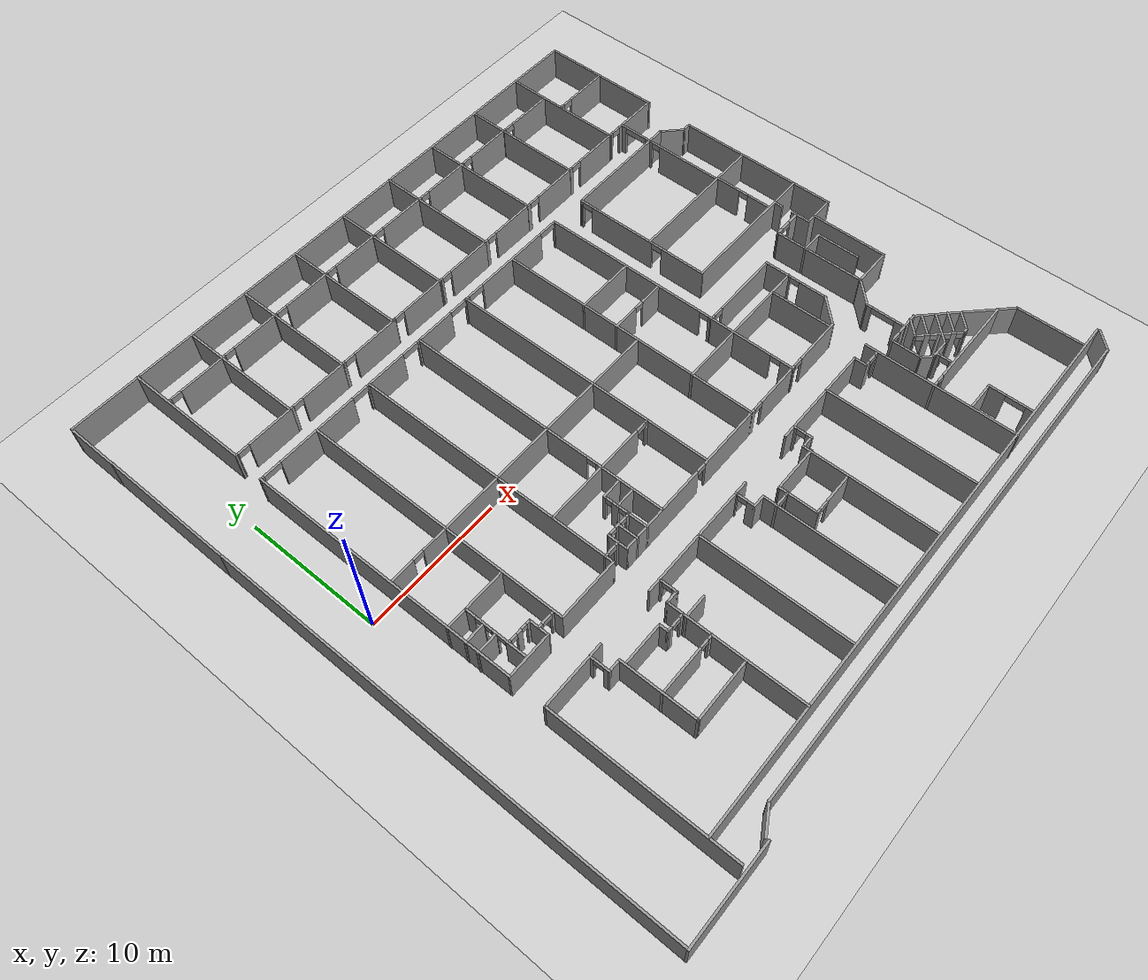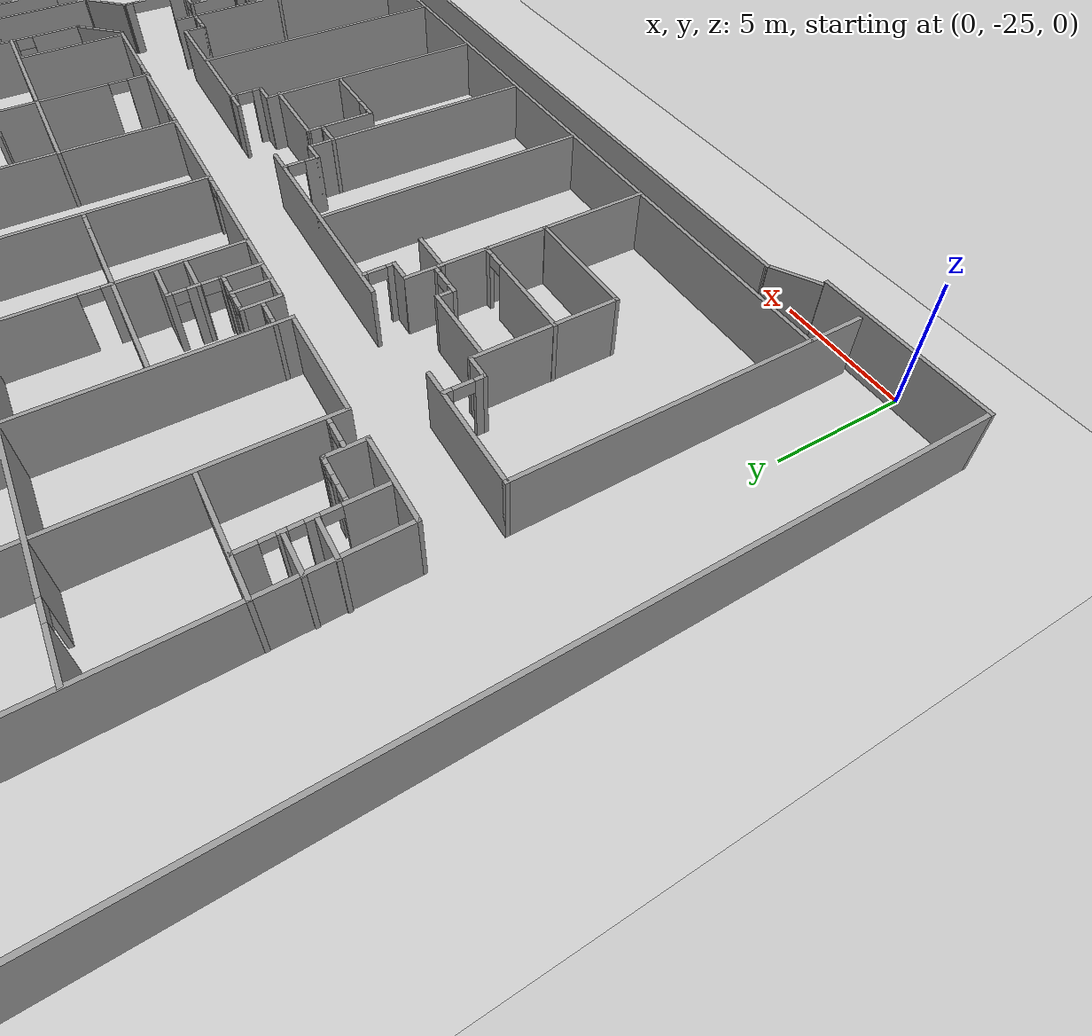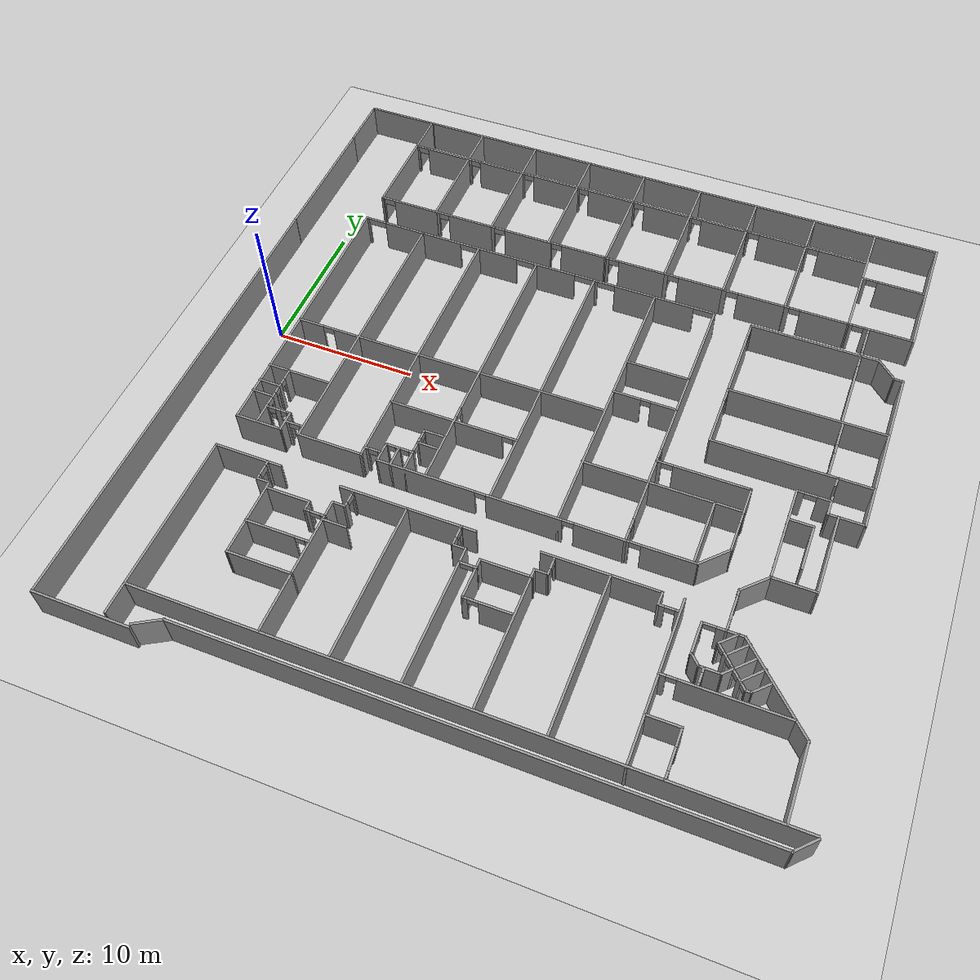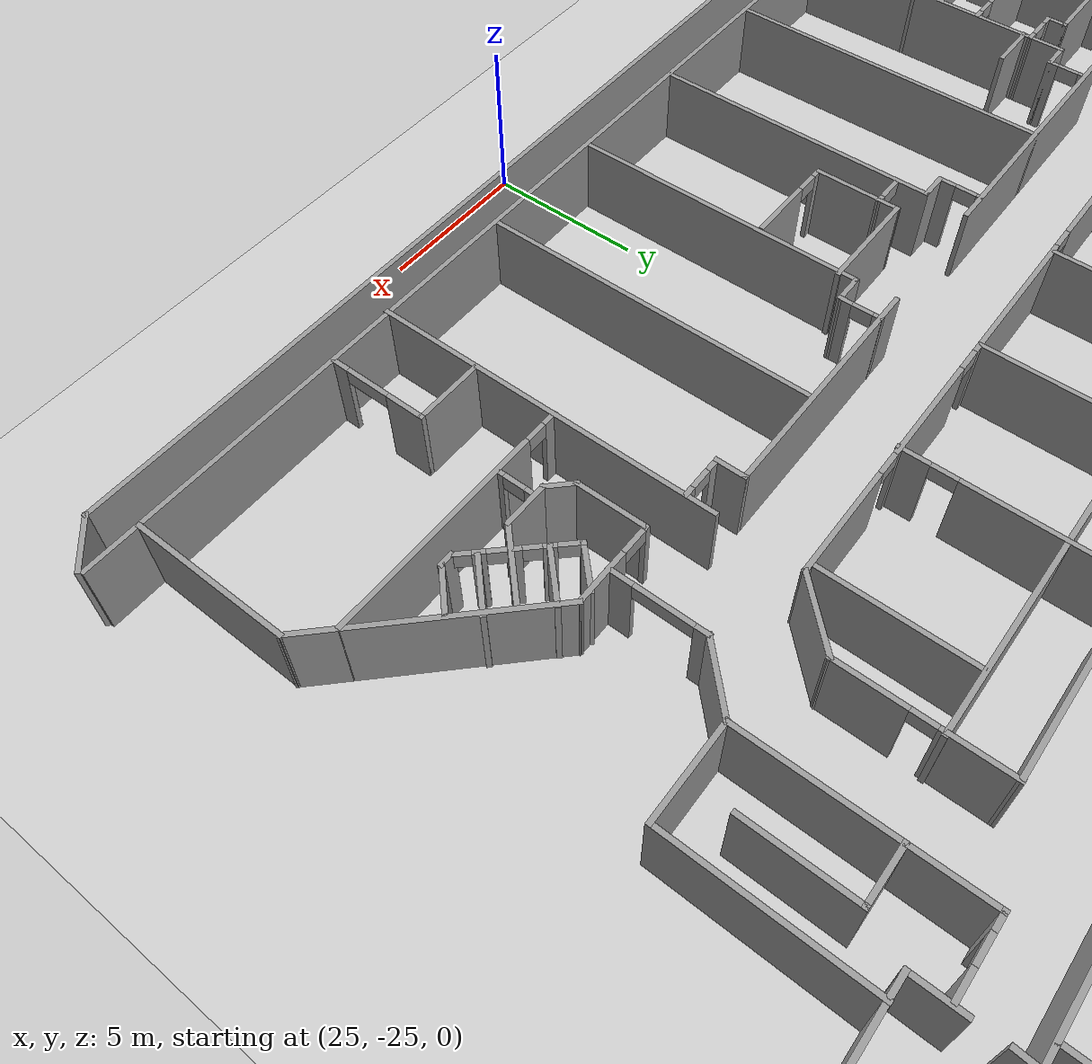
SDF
<sdf version="1.7">
 <world name="default">
  <light name="sun" type="directional">
   <pose>0 0 10 0 -0 0</pose>
   <diffuse>0.8 0.8 0.8 1</diffuse>
   <specular>0.2 0.2 0.2 1</specular>
   <attenuation>
    <range>1000</range>
    <constant>0.9</constant>
    <linear>0.01</linear>
    <quadratic>0.001</quadratic>
   </attenuation>
   <direction>-0.5 0.1 -0.9</direction>
   <spot><inner_angle>0</inner_angle><outer_angle>0</outer_angle><falloff>0</falloff></spot>
  </light>
  <model name="ground_plane">
   <static>1</static>
   <link name="link">
    <collision name="collision">
     <geometry><plane><normal>0 0 1</normal><size>100 100</size></plane></geometry>
     <surface>
      <contact><collide_bitmask>65535</collide_bitmask></contact>
      <friction><ode><mu>100</mu><mu2>50</mu2></ode></friction>
     </surface>
    </collision>
    <visual name="visual">
     <cast_shadows>0</cast_shadows>
     <geometry><plane><normal>0 0 1</normal><size>100 100</size></plane></geometry>
     <material>
      <script><uri>file://media/materials/scripts/gazebo.material</uri><name>Gazebo/Grey</name></script>
     </material>
    </visual>
   </link>
  </model>
  <gravity>0 0 -9.8</gravity>
  <magnetic_field>6e-06 2.3e-05 -4.2e-05</magnetic_field>
  <atmosphere type="adiabatic"/>
  <physics type="ode">
   <max_step_size>0.001</max_step_size>
   <real_time_factor>1</real_time_factor>
   <real_time_update_rate>1000</real_time_update_rate>
  </physics>
  <scene><ambient>0.4 0.4 0.4 1</ambient><background>0.7 0.7 0.7 1</background><shadows>1</shadows></scene>
  <audio><device>default</device></audio>
  <spherical_coordinates>
   <surface_model>EARTH_WGS84</surface_model>
   <latitude_deg>0</latitude_deg>
   <longitude_deg>0</longitude_deg>
   <elevation>0</elevation>
   <heading_deg>0</heading_deg>
  </spherical_coordinates>
  <model name="anglo_teste">
   <pose>0.302227 -1.18447 0 0 -0 0</pose>
   <link name="Wall_2">
    <collision name="Wall_2_Collision">
     <geometry><box><size>33.2918 0.15 2.5</size></box></geometry>
     <pose>0 0 1.25 0 -0 0</pose>
    </collision>
    <visual name="Wall_2_Visual">
     <pose>0 0 1.25 0 -0 0</pose>
     <geometry><box><size>33.2918 0.15 2.5</size></box></geometry>
     <material>
      <script><uri>file://media/materials/scripts/gazebo.material</uri><name>Gazebo/Grey</name></script>
      <ambient>1 1 1 1</ambient>
     </material>
     <meta><layer>0</layer></meta>
    </visual>
    <pose>-3.28849 -6.78646 0 0 -0 -1.5686</pose>
   </link>
   <link name="Wall_4">
    <collision name="Wall_4_Collision">
     <geometry><box><size>6.75 0.15 2.5</size></box></geometry>
     <pose>0 0 1.25 0 -0 0</pose>
    </collision>
    <visual name="Wall_4_Visual">
     <pose>0 0 1.25 0 -0 0</pose>
     <geometry><box><size>6.75 0.15 2.5</size></box></geometry>
     <material>
      <script><uri>file://media/materials/scripts/gazebo.material</uri><name>Gazebo/Grey</name></script>
      <ambient>1 1 1 1</ambient>
     </material>
     <meta><layer>0</layer></meta>
    </visual>
    <pose>0.047964 -23.4996 0 0 -0 3.14159</pose>
   </link>
   <link name="Wall_6">
    <collision name="Wall_6_Collision">
     <geometry><box><size>5.25 0.15 2.5</size></box></geometry>
     <pose>0 0 1.25 0 -0 0</pose>
    </collision>
    <visual name="Wall_6_Visual">
     <pose>0 0 1.25 0 -0 0</pose>
     <geometry><box><size>5.25 0.15 2.5</size></box></geometry>
     <material>
      <script><uri>file://media/materials/scripts/gazebo.material</uri><name>Gazebo/Grey</name></script>
      <ambient>1 1 1 1</ambient>
     </material>
     <meta><layer>0</layer></meta>
    </visual>
    <pose>-0.774526 23.4996 0 0 -0 3.14159</pose>
   </link>
   <link name="Wall_8">
    <collision name="Wall_8_Collision">
     <geometry><box><size>3.75 0.15 2.5</size></box></geometry>
     <pose>0 0 1.25 0 -0 0</pose>
    </collision>
    <visual name="Wall_8_Visual">
     <pose>0 0 1.25 0 -0 0</pose>
     <geometry><box><size>3.75 0.15 2.5</size></box></geometry>
     <material>
      <script><uri>file://media/materials/scripts/gazebo.material</uri><name>Gazebo/Grey</name></script>
      <ambient>1 1 1 1</ambient>
     </material>
     <meta><layer>0</layer></meta>
    </visual>
    <pose>-3.34796 21.478 0 0 -0 -1.5708</pose>
   </link>
   <static>1</static>
  </model>
  <model name="anglo_3_andar_metade">
   <pose>-4.28797 -1.08288 0 0 -0 0</pose>
   <link name="Wall_11">
    <collision name="Wall_11_Collision">
     <geometry><box><size>9.25 0.15 2.5</size></box></geometry>
     <pose>0 0 1.25 0 -0 0</pose>
    </collision>
    <visual name="Wall_11_Visual">
     <pose>0 0 1.25 0 -0 0</pose>
     <geometry><box><size>9.25 0.15 2.5</size></box></geometry>
     <material>
      <script><uri>file://media/materials/scripts/gazebo.material</uri><name>Gazebo/Grey</name></script>
      <ambient>1 1 1 1</ambient>
     </material>
     <meta><layer>0</layer></meta>
    </visual>
    <pose>41.6877 18.8137 0 0 -0 -1.5708</pose>
   </link>
   <link name="Wall_13">
    <pose>43.8627 14.2737 0 0 -0 0</pose>
    <visual name="Wall_13_Visual_0">
     <pose>-2.08 0 1.25 0 -0 0</pose>
     <geometry><box><size>0.34 0.15 2.5</size></box></geometry>
     <material>
      <script><uri>file://media/materials/scripts/gazebo.material</uri><name>Gazebo/Grey</name></script>
      <ambient>1 1 1 1</ambient>
     </material>
     <meta><layer>0</layer></meta>
    </visual>
    <collision name="Wall_13_Collision_0">
     <geometry><box><size>0.34 0.15 2.5</size></box></geometry>
     <pose>-2.08 0 1.25 0 -0 0</pose>
    </collision>
    <visual name="Wall_13_Visual_1">
     <pose>0.56 0 1.25 0 -0 0</pose>
     <geometry><box><size>3.38 0.15 2.5</size></box></geometry>
     <material>
      <script><uri>file://media/materials/scripts/gazebo.material</uri><name>Gazebo/Grey</name></script>
      <ambient>1 1 1 1</ambient>
     </material>
     <meta><layer>0</layer></meta>
    </visual>
    <collision name="Wall_13_Collision_1">
     <geometry><box><size>3.38 0.15 2.5</size></box></geometry>
     <pose>0.56 0 1.25 0 -0 0</pose>
    </collision>
    <visual name="Wall_13_Visual_2">
     <pose>-1.52 0 2.25 0 -0 0</pose>
     <geometry><box><size>0.78 0.15 0.5</size></box></geometry>
     <material>
      <script><uri>file://media/materials/scripts/gazebo.material</uri><name>Gazebo/Grey</name></script>
      <ambient>1 1 1 1</ambient>
     </material>
     <meta><layer>0</layer></meta>
    </visual>
    <collision name="Wall_13_Collision_2">
     <geometry><box><size>0.78 0.15 0.5</size></box></geometry>
     <pose>-1.52 0 2.25 0 -0 0</pose>
    </collision>
   </link>
   <link name="Wall_15">
    <pose>43.8727 18.9037 0 0 -0 0</pose>
    <visual name="Wall_15_Visual_0">
     <pose>-2.065 0 1.25 0 -0 0</pose>
     <geometry><box><size>0.370002 0.15 2.5</size></box></geometry>
     <material>
      <script><uri>file://media/materials/scripts/gazebo.material</uri><name>Gazebo/Grey</name></script>
      <ambient>1 1 1 1</ambient>
     </material>
     <meta><layer>0</layer></meta>
    </visual>
    <collision name="Wall_15_Collision_0">
     <geometry><box><size>0.370002 0.15 2.5</size></box></geometry>
     <pose>-2.065 0 1.25 0 -0 0</pose>
    </collision>
    <visual name="Wall_15_Visual_1">
     <pose>0.575001 0 1.25 0 -0 0</pose>
     <geometry><box><size>3.35 0.15 2.5</size></box></geometry>
     <material>
      <script><uri>file://media/materials/scripts/gazebo.material</uri><name>Gazebo/Grey</name></script>
      <ambient>1 1 1 1</ambient>
     </material>
     <meta><layer>0</layer></meta>
    </visual>
    <collision name="Wall_15_Collision_1">
     <geometry><box><size>3.35 0.15 2.5</size></box></geometry>
     <pose>0.575001 0 1.25 0 -0 0</pose>
    </collision>
    <visual name="Wall_15_Visual_2">
     <pose>-1.49 0 2.25 0 -0 0</pose>
     <geometry><box><size>0.78 0.15 0.5</size></box></geometry>
     <material>
      <script><uri>file://media/materials/scripts/gazebo.material</uri><name>Gazebo/Grey</name></script>
      <ambient>1 1 1 1</ambient>
     </material>
     <meta><layer>0</layer></meta>
    </visual>
    <collision name="Wall_15_Collision_2">
     <geometry><box><size>0.78 0.15 0.5</size></box></geometry>
     <pose>-1.49 0 2.25 0 -0 0</pose>
    </collision>
   </link>
   <link name="Wall_17">
    <collision name="Wall_17_Collision">
     <geometry><box><size>9.25 0.15 2.5</size></box></geometry>
     <pose>0 0 1.25 0 -0 0</pose>
    </collision>
    <visual name="Wall_17_Visual">
     <pose>0 0 1.25 0 -0 0</pose>
     <geometry><box><size>9.25 0.15 2.5</size></box></geometry>
     <material>
      <script><uri>file://media/materials/scripts/gazebo.material</uri><name>Gazebo/Grey</name></script>
      <ambient>1 1 1 1</ambient>
     </material>
     <meta><layer>0</layer></meta>
    </visual>
    <pose>37.1877 18.8237 0 0 -0 -1.5708</pose>
   </link>
   <link name="Wall_19">
    <pose>39.4377 14.2687 0 0 -0 -0.002222</pose>
    <visual name="Wall_19_Visual_0">
     <pose>-2.13754 0 1.25 0 -0 0</pose>
     <geometry><box><size>0.374924 0.15 2.5</size></box></geometry>
     <material>
      <script><uri>file://media/materials/scripts/gazebo.material</uri><name>Gazebo/Grey</name></script>
      <ambient>1 1 1 1</ambient>
     </material>
     <meta><layer>0</layer></meta>
    </visual>
    <collision name="Wall_19_Collision_0">
     <geometry><box><size>0.374924 0.15 2.5</size></box></geometry>
     <pose>-2.13754 0 1.25 0 -0 0</pose>
    </collision>
    <visual name="Wall_19_Visual_1">
     <pose>0.587462 0 1.25 0 -0 0</pose>
     <geometry><box><size>3.47508 0.15 2.5</size></box></geometry>
     <material>
      <script><uri>file://media/materials/scripts/gazebo.material</uri><name>Gazebo/Grey</name></script>
      <ambient>1 1 1 1</ambient>
     </material>
     <meta><layer>0</layer></meta>
    </visual>
    <collision name="Wall_19_Collision_1">
     <geometry><box><size>3.47508 0.15 2.5</size></box></geometry>
     <pose>0.587462 0 1.25 0 -0 0</pose>
    </collision>
    <visual name="Wall_19_Visual_2">
     <pose>-1.55008 0 2.25 0 -0 0</pose>
     <geometry><box><size>0.8 0.15 0.5</size></box></geometry>
     <material>
      <script><uri>file://media/materials/scripts/gazebo.material</uri><name>Gazebo/Grey</name></script>
      <ambient>1 1 1 1</ambient>
     </material>
     <meta><layer>0</layer></meta>
    </visual>
    <collision name="Wall_19_Collision_2">
     <geometry><box><size>0.8 0.15 0.5</size></box></geometry>
     <pose>-1.55008 0 2.25 0 -0 0</pose>
    </collision>
   </link>
   <link name="Wall_2">
    <collision name="Wall_2_Collision">
     <geometry><box><size>40.0201 0.15 2.5</size></box></geometry>
     <pose>0 0 1.25 0 -0 0</pose>
    </collision>
    <visual name="Wall_2_Visual">
     <pose>0 0 1.25 0 -0 0</pose>
     <geometry><box><size>40.0201 0.15 2.5</size></box></geometry>
     <material>
      <script><uri>file://media/materials/scripts/gazebo.material</uri><name>Gazebo/Grey</name></script>
      <ambient>1 1 1 1</ambient>
     </material>
     <meta><layer>0</layer></meta>
    </visual>
    <pose>26.2327 23.3787 0 0 -0 3.14034</pose>
   </link>
   <link name="Wall_21">
    <pose>39.3627 20.4837 0 0 -0 0</pose>
    <visual name="Wall_21_Visual_0">
     <pose>-2.11 0 1.25 0 -0 0</pose>
     <geometry><box><size>0.280001 0.15 2.5</size></box></geometry>
     <material>
      <script><uri>file://media/materials/scripts/gazebo.material</uri><name>Gazebo/Grey</name></script>
      <ambient>1 1 1 1</ambient>
     </material>
     <meta><layer>0</layer></meta>
    </visual>
    <collision name="Wall_21_Collision_0">
     <geometry><box><size>0.280001 0.15 2.5</size></box></geometry>
     <pose>-2.11 0 1.25 0 -0 0</pose>
    </collision>
    <visual name="Wall_21_Visual_1">
     <pose>0.525 0 1.25 0 -0 0</pose>
     <geometry><box><size>3.45 0.15 2.5</size></box></geometry>
     <material>
      <script><uri>file://media/materials/scripts/gazebo.material</uri><name>Gazebo/Grey</name></script>
      <ambient>1 1 1 1</ambient>
     </material>
     <meta><layer>0</layer></meta>
    </visual>
    <collision name="Wall_21_Collision_1">
     <geometry><box><size>3.45 0.15 2.5</size></box></geometry>
     <pose>0.525 0 1.25 0 -0 0</pose>
    </collision>
    <visual name="Wall_21_Visual_2">
     <pose>-1.585 0 2.25 0 -0 0</pose>
     <geometry><box><size>0.77 0.15 0.5</size></box></geometry>
     <material>
      <script><uri>file://media/materials/scripts/gazebo.material</uri><name>Gazebo/Grey</name></script>
      <ambient>1 1 1 1</ambient>
     </material>
     <meta><layer>0</layer></meta>
    </visual>
    <collision name="Wall_21_Collision_2">
     <geometry><box><size>0.77 0.15 0.5</size></box></geometry>
     <pose>-1.585 0 2.25 0 -0 0</pose>
    </collision>
   </link>
   <link name="Wall_23">
    <collision name="Wall_23_Collision">
     <geometry><box><size>9.25 0.15 2.5</size></box></geometry>
     <pose>0 0 1.25 0 -0 0</pose>
    </collision>
    <visual name="Wall_23_Visual">
     <pose>0 0 1.25 0 -0 0</pose>
     <geometry><box><size>9.25 0.15 2.5</size></box></geometry>
     <material>
      <script><uri>file://media/materials/scripts/gazebo.material</uri><name>Gazebo/Grey</name></script>
      <ambient>1 1 1 1</ambient>
     </material>
     <meta><layer>0</layer></meta>
    </visual>
    <pose>32.7377 18.8237 0 0 -0 -1.5708</pose>
   </link>
   <link name="Wall_25">
    <pose>34.9127 14.2637 0 0 -0 0</pose>
    <visual name="Wall_25_Visual_0">
     <pose>-2.085 0 1.25 0 -0 0</pose>
     <geometry><box><size>0.329999 0.15 2.5</size></box></geometry>
     <material>
      <script><uri>file://media/materials/scripts/gazebo.material</uri><name>Gazebo/Grey</name></script>
      <ambient>1 1 1 1</ambient>
     </material>
     <meta><layer>0</layer></meta>
    </visual>
    <collision name="Wall_25_Collision_0">
     <geometry><box><size>0.329999 0.15 2.5</size></box></geometry>
     <pose>-2.085 0 1.25 0 -0 0</pose>
    </collision>
    <visual name="Wall_25_Visual_1">
     <pose>0.579999 0 1.25 0 -0 0</pose>
     <geometry><box><size>3.34 0.15 2.5</size></box></geometry>
     <material>
      <script><uri>file://media/materials/scripts/gazebo.material</uri><name>Gazebo/Grey</name></script>
      <ambient>1 1 1 1</ambient>
     </material>
     <meta><layer>0</layer></meta>
    </visual>
    <collision name="Wall_25_Collision_1">
     <geometry><box><size>3.34 0.15 2.5</size></box></geometry>
     <pose>0.579999 0 1.25 0 -0 0</pose>
    </collision>
    <visual name="Wall_25_Visual_2">
     <pose>-1.505 0 2.25 0 -0 0</pose>
     <geometry><box><size>0.83 0.15 0.5</size></box></geometry>
     <material>
      <script><uri>file://media/materials/scripts/gazebo.material</uri><name>Gazebo/Grey</name></script>
      <ambient>1 1 1 1</ambient>
     </material>
     <meta><layer>0</layer></meta>
    </visual>
    <collision name="Wall_25_Collision_2">
     <geometry><box><size>0.83 0.15 0.5</size></box></geometry>
     <pose>-1.505 0 2.25 0 -0 0</pose>
    </collision>
   </link>
   <link name="Wall_27">
    <pose>34.9127 20.5137 0 0 -0 0</pose>
    <visual name="Wall_27_Visual_0">
     <pose>-2.0975 0 1.25 0 -0 0</pose>
     <geometry><box><size>0.305002 0.15 2.5</size></box></geometry>
     <material>
      <script><uri>file://media/materials/scripts/gazebo.material</uri><name>Gazebo/Grey</name></script>
      <ambient>1 1 1 1</ambient>
     </material>
     <meta><layer>0</layer></meta>
    </visual>
    <collision name="Wall_27_Collision_0">
     <geometry><box><size>0.305002 0.15 2.5</size></box></geometry>
     <pose>-2.0975 0 1.25 0 -0 0</pose>
    </collision>
    <visual name="Wall_27_Visual_1">
     <pose>0.537501 0 1.25 0 -0 0</pose>
     <geometry><box><size>3.425 0.15 2.5</size></box></geometry>
     <material>
      <script><uri>file://media/materials/scripts/gazebo.material</uri><name>Gazebo/Grey</name></script>
      <ambient>1 1 1 1</ambient>
     </material>
     <meta><layer>0</layer></meta>
    </visual>
    <collision name="Wall_27_Collision_1">
     <geometry><box><size>3.425 0.15 2.5</size></box></geometry>
     <pose>0.537501 0 1.25 0 -0 0</pose>
    </collision>
    <visual name="Wall_27_Visual_2">
     <pose>-1.56 0 2.25 0 -0 0</pose>
     <geometry><box><size>0.77 0.15 0.5</size></box></geometry>
     <material>
      <script><uri>file://media/materials/scripts/gazebo.material</uri><name>Gazebo/Grey</name></script>
      <ambient>1 1 1 1</ambient>
     </material>
     <meta><layer>0</layer></meta>
    </visual>
    <collision name="Wall_27_Collision_2">
     <geometry><box><size>0.77 0.15 0.5</size></box></geometry>
     <pose>-1.56 0 2.25 0 -0 0</pose>
    </collision>
   </link>
   <link name="Wall_31">
    <collision name="Wall_31_Collision">
     <geometry><box><size>9.25 0.15 2.5</size></box></geometry>
     <pose>0 0 1.25 0 -0 0</pose>
    </collision>
    <visual name="Wall_31_Visual">
     <pose>0 0 1.25 0 -0 0</pose>
     <geometry><box><size>9.25 0.15 2.5</size></box></geometry>
     <material>
      <script><uri>file://media/materials/scripts/gazebo.material</uri><name>Gazebo/Grey</name></script>
      <ambient>1 1 1 1</ambient>
     </material>
     <meta><layer>0</layer></meta>
    </visual>
    <pose>28.4177 18.8237 0 0 -0 -1.5708</pose>
   </link>
   <link name="Wall_34">
    <pose>30.5927 14.2737 0 0 -0 0</pose>
    <visual name="Wall_34_Visual_0">
     <pose>-2.08 0 1.25 0 -0 0</pose>
     <geometry><box><size>0.34 0.15 2.5</size></box></geometry>
     <material>
      <script><uri>file://media/materials/scripts/gazebo.material</uri><name>Gazebo/Grey</name></script>
      <ambient>1 1 1 1</ambient>
     </material>
     <meta><layer>0</layer></meta>
    </visual>
    <collision name="Wall_34_Collision_0">
     <geometry><box><size>0.34 0.15 2.5</size></box></geometry>
     <pose>-2.08 0 1.25 0 -0 0</pose>
    </collision>
    <visual name="Wall_34_Visual_1">
     <pose>0.56 0 1.25 0 -0 0</pose>
     <geometry><box><size>3.38 0.15 2.5</size></box></geometry>
     <material>
      <script><uri>file://media/materials/scripts/gazebo.material</uri><name>Gazebo/Grey</name></script>
      <ambient>1 1 1 1</ambient>
     </material>
     <meta><layer>0</layer></meta>
    </visual>
    <collision name="Wall_34_Collision_1">
     <geometry><box><size>3.38 0.15 2.5</size></box></geometry>
     <pose>0.56 0 1.25 0 -0 0</pose>
    </collision>
    <visual name="Wall_34_Visual_2">
     <pose>-1.52 0 2.25 0 -0 0</pose>
     <geometry><box><size>0.78 0.15 0.5</size></box></geometry>
     <material>
      <script><uri>file://media/materials/scripts/gazebo.material</uri><name>Gazebo/Grey</name></script>
      <ambient>1 1 1 1</ambient>
     </material>
     <meta><layer>0</layer></meta>
    </visual>
    <collision name="Wall_34_Collision_2">
     <geometry><box><size>0.78 0.15 0.5</size></box></geometry>
     <pose>-1.52 0 2.25 0 -0 0</pose>
    </collision>
   </link>
   <link name="Wall_36">
    <pose>30.5927 20.4837 0 0 -0 0</pose>
    <visual name="Wall_36_Visual_0">
     <pose>-2.11 0 1.25 0 -0 0</pose>
     <geometry><box><size>0.28 0.15 2.5</size></box></geometry>
     <material>
      <script><uri>file://media/materials/scripts/gazebo.material</uri><name>Gazebo/Grey</name></script>
      <ambient>1 1 1 1</ambient>
     </material>
     <meta><layer>0</layer></meta>
    </visual>
    <collision name="Wall_36_Collision_0">
     <geometry><box><size>0.28 0.15 2.5</size></box></geometry>
     <pose>-2.11 0 1.25 0 -0 0</pose>
    </collision>
    <visual name="Wall_36_Visual_1">
     <pose>0.505 0 1.25 0 -0 0</pose>
     <geometry><box><size>3.49 0.15 2.5</size></box></geometry>
     <material>
      <script><uri>file://media/materials/scripts/gazebo.material</uri><name>Gazebo/Grey</name></script>
      <ambient>1 1 1 1</ambient>
     </material>
     <meta><layer>0</layer></meta>
    </visual>
    <collision name="Wall_36_Collision_1">
     <geometry><box><size>3.49 0.15 2.5</size></box></geometry>
     <pose>0.505 0 1.25 0 -0 0</pose>
    </collision>
    <visual name="Wall_36_Visual_2">
     <pose>-1.605 0 2.25 0 -0 0</pose>
     <geometry><box><size>0.73 0.15 0.5</size></box></geometry>
     <material>
      <script><uri>file://media/materials/scripts/gazebo.material</uri><name>Gazebo/Grey</name></script>
      <ambient>1 1 1 1</ambient>
     </material>
     <meta><layer>0</layer></meta>
    </visual>
    <collision name="Wall_36_Collision_2">
     <geometry><box><size>0.73 0.15 0.5</size></box></geometry>
     <pose>-1.605 0 2.25 0 -0 0</pose>
    </collision>
   </link>
   <link name="Wall_367">
    <collision name="Wall_367_Collision">
     <geometry><box><size>13 0.15 2.5</size></box></geometry>
     <pose>0 0 1.25 0 -0 0</pose>
    </collision>
    <visual name="Wall_367_Visual">
     <pose>0 0 1.25 0 -0 0</pose>
     <geometry><box><size>13 0.15 2.5</size></box></geometry>
     <material>
      <script><uri>file://media/materials/scripts/gazebo.material</uri><name>Gazebo/Grey</name></script>
      <ambient>1 1 1 1</ambient>
     </material>
     <meta><layer>0</layer></meta>
    </visual>
    <pose>6.14771 -16.8213 0 0 -0 -1.5708</pose>
   </link>
   <link name="Wall_369">
    <collision name="Wall_369_Collision">
     <geometry><box><size>4.75 0.15 2.5</size></box></geometry>
     <pose>0 0 1.25 0 -0 0</pose>
    </collision>
    <visual name="Wall_369_Visual">
     <pose>0 0 1.25 0 -0 0</pose>
     <geometry><box><size>4.75 0.15 2.5</size></box></geometry>
     <material>
      <script><uri>file://media/materials/scripts/gazebo.material</uri><name>Gazebo/Grey</name></script>
      <ambient>1 1 1 1</ambient>
     </material>
     <meta><layer>0</layer></meta>
    </visual>
    <pose>8.44771 -10.3963 0 0 -0 0</pose>
   </link>
   <link name="Wall_371">
    <pose>9.84771 -11.0913 0 0 -0 -1.5708</pose>
    <visual name="Wall_371_Visual_0">
     <pose>-0.575 0 1.25 0 -0 0</pose>
     <geometry><box><size>0.35 0.15 2.5</size></box></geometry>
     <material>
      <script><uri>file://media/materials/scripts/gazebo.material</uri><name>Gazebo/Grey</name></script>
      <ambient>1 1 1 1</ambient>
     </material>
     <meta><layer>0</layer></meta>
    </visual>
    <collision name="Wall_371_Collision_0">
     <geometry><box><size>0.35 0.15 2.5</size></box></geometry>
     <pose>-0.575 0 1.25 0 -0 0</pose>
    </collision>
    <visual name="Wall_371_Visual_1">
     <pose>0.545 0 1.25 0 -0 0</pose>
     <geometry><box><size>0.41 0.15 2.5</size></box></geometry>
     <material>
      <script><uri>file://media/materials/scripts/gazebo.material</uri><name>Gazebo/Grey</name></script>
      <ambient>1 1 1 1</ambient>
     </material>
     <meta><layer>0</layer></meta>
    </visual>
    <collision name="Wall_371_Collision_1">
     <geometry><box><size>0.41 0.15 2.5</size></box></geometry>
     <pose>0.545 0 1.25 0 -0 0</pose>
    </collision>
    <visual name="Wall_371_Visual_2">
     <pose>-0.03 0 2.25 0 -0 0</pose>
     <geometry><box><size>0.74 0.15 0.5</size></box></geometry>
     <material>
      <script><uri>file://media/materials/scripts/gazebo.material</uri><name>Gazebo/Grey</name></script>
      <ambient>1 1 1 1</ambient>
     </material>
     <meta><layer>0</layer></meta>
    </visual>
    <collision name="Wall_371_Collision_2">
     <geometry><box><size>0.74 0.15 0.5</size></box></geometry>
     <pose>-0.03 0 2.25 0 -0 0</pose>
    </collision>
   </link>
   <link name="Wall_373">
    <collision name="Wall_373_Collision">
     <geometry><box><size>1 0.15 2.5</size></box></geometry>
     <pose>0 0 1.25 0 -0 0</pose>
    </collision>
    <visual name="Wall_373_Visual">
     <pose>0 0 1.25 0 -0 0</pose>
     <geometry><box><size>1 0.15 2.5</size></box></geometry>
     <material>
      <script><uri>file://media/materials/scripts/gazebo.material</uri><name>Gazebo/Grey</name></script>
      <ambient>1 1 1 1</ambient>
     </material>
     <meta><layer>0</layer></meta>
    </visual>
    <pose>10.2727 -11.7663 0 0 -0 0</pose>
   </link>
   <link name="Wall_375">
    <collision name="Wall_375_Collision">
     <geometry><box><size>5.5 0.15 2.5</size></box></geometry>
     <pose>0 0 1.25 0 -0 0</pose>
    </collision>
    <visual name="Wall_375_Visual">
     <pose>0 0 1.25 0 -0 0</pose>
     <geometry><box><size>5.5 0.15 2.5</size></box></geometry>
     <material>
      <script><uri>file://media/materials/scripts/gazebo.material</uri><name>Gazebo/Grey</name></script>
      <ambient>1 1 1 1</ambient>
     </material>
     <meta><layer>0</layer></meta>
    </visual>
    <pose>10.6977 -14.4413 0 0 -0 -1.5708</pose>
   </link>
   <link name="Wall_376">
    <collision name="Wall_376_Collision">
     <geometry><box><size>4.49074 0.15 2.5</size></box></geometry>
     <pose>0 0 1.25 0 -0 0</pose>
    </collision>
    <visual name="Wall_376_Visual">
     <pose>0 0 1.25 0 -0 0</pose>
     <geometry><box><size>4.49074 0.15 2.5</size></box></geometry>
     <material>
      <script><uri>file://media/materials/scripts/gazebo.material</uri><name>Gazebo/Grey</name></script>
      <ambient>1 1 1 1</ambient>
     </material>
     <meta><layer>0</layer></meta>
    </visual>
    <pose>12.8677 -17.1063 0 0 -0 0.004608</pose>
   </link>
   <link name="Wall_377">
    <collision name="Wall_377_Collision">
     <geometry><box><size>4.48001 0.15 2.5</size></box></geometry>
     <pose>0 0 1.25 0 -0 0</pose>
    </collision>
    <visual name="Wall_377_Visual">
     <pose>0 0 1.25 0 -0 0</pose>
     <geometry><box><size>4.48001 0.15 2.5</size></box></geometry>
     <material>
      <script><uri>file://media/materials/scripts/gazebo.material</uri><name>Gazebo/Grey</name></script>
      <ambient>1 1 1 1</ambient>
     </material>
     <meta><layer>0</layer></meta>
    </visual>
    <pose>15.0427 -14.9313 0 0 -0 1.56849</pose>
   </link>
   <link name="Wall_378">
    <pose>14.3727 -12.7663 0 0 -0 3.14159</pose>
    <visual name="Wall_378_Visual_0">
     <pose>-0.5675 0 1.25 0 -0 0</pose>
     <geometry><box><size>0.365 0.15 2.5</size></box></geometry>
     <material>
      <script><uri>file://media/materials/scripts/gazebo.material</uri><name>Gazebo/Grey</name></script>
      <ambient>1 1 1 1</ambient>
     </material>
     <meta><layer>0</layer></meta>
    </visual>
    <collision name="Wall_378_Collision_0">
     <geometry><box><size>0.365 0.15 2.5</size></box></geometry>
     <pose>-0.5675 0 1.25 0 -0 0</pose>
    </collision>
    <visual name="Wall_378_Visual_1">
     <pose>0.5425 0 1.25 0 -0 0</pose>
     <geometry><box><size>0.415 0.15 2.5</size></box></geometry>
     <material>
      <script><uri>file://media/materials/scripts/gazebo.material</uri><name>Gazebo/Grey</name></script>
      <ambient>1 1 1 1</ambient>
     </material>
     <meta><layer>0</layer></meta>
    </visual>
    <collision name="Wall_378_Collision_1">
     <geometry><box><size>0.415 0.15 2.5</size></box></geometry>
     <pose>0.5425 0 1.25 0 -0 0</pose>
    </collision>
    <visual name="Wall_378_Visual_2">
     <pose>-0.025 0 2.25 0 -0 0</pose>
     <geometry><box><size>0.72 0.15 0.5</size></box></geometry>
     <material>
      <script><uri>file://media/materials/scripts/gazebo.material</uri><name>Gazebo/Grey</name></script>
      <ambient>1 1 1 1</ambient>
     </material>
     <meta><layer>0</layer></meta>
    </visual>
    <collision name="Wall_378_Collision_2">
     <geometry><box><size>0.72 0.15 0.5</size></box></geometry>
     <pose>-0.025 0 2.25 0 -0 0</pose>
    </collision>
   </link>
   <link name="Wall_379">
    <collision name="Wall_379_Collision">
     <geometry><box><size>0.75 0.15 2.5</size></box></geometry>
     <pose>0 0 1.25 0 -0 0</pose>
    </collision>
    <visual name="Wall_379_Visual">
     <pose>0 0 1.25 0 -0 0</pose>
     <geometry><box><size>0.75 0.15 2.5</size></box></geometry>
     <material>
      <script><uri>file://media/materials/scripts/gazebo.material</uri><name>Gazebo/Grey</name></script>
      <ambient>1 1 1 1</ambient>
     </material>
     <meta><layer>0</layer></meta>
    </visual>
    <pose>13.6977 -12.4663 0 0 -0 1.5708</pose>
   </link>
   <link name="Wall_38">
    <collision name="Wall_38_Collision">
     <geometry><box><size>9.25 0.15 2.5</size></box></geometry>
     <pose>0 0 1.25 0 -0 0</pose>
    </collision>
    <visual name="Wall_38_Visual">
     <pose>0 0 1.25 0 -0 0</pose>
     <geometry><box><size>9.25 0.15 2.5</size></box></geometry>
     <material>
      <script><uri>file://media/materials/scripts/gazebo.material</uri><name>Gazebo/Grey</name></script>
      <ambient>1 1 1 1</ambient>
     </material>
     <meta><layer>0</layer></meta>
    </visual>
    <pose>23.9777 18.8137 0 0 -0 -1.5708</pose>
   </link>
   <link name="Wall_380">
    <collision name="Wall_380_Collision">
     <geometry><box><size>3 0.15 2.5</size></box></geometry>
     <pose>0 0 1.25 0 -0 0</pose>
    </collision>
    <visual name="Wall_380_Visual">
     <pose>0 0 1.25 0 -0 0</pose>
     <geometry><box><size>3 0.15 2.5</size></box></geometry>
     <material>
      <script><uri>file://media/materials/scripts/gazebo.material</uri><name>Gazebo/Grey</name></script>
      <ambient>1 1 1 1</ambient>
     </material>
     <meta><layer>0</layer></meta>
    </visual>
    <pose>12.2727 -12.1663 0 0 -0 3.14159</pose>
   </link>
   <link name="Wall_382">
    <pose>12.8527 -14.7463 0 0 -0 0</pose>
    <visual name="Wall_382_Visual_0">
     <pose>-0.525 0 1.25 0 -0 0</pose>
     <geometry><box><size>3.45 0.15 2.5</size></box></geometry>
     <material>
      <script><uri>file://media/materials/scripts/gazebo.material</uri><name>Gazebo/Grey</name></script>
      <ambient>1 1 1 1</ambient>
     </material>
     <meta><layer>0</layer></meta>
    </visual>
    <collision name="Wall_382_Collision_0">
     <geometry><box><size>3.45 0.15 2.5</size></box></geometry>
     <pose>-0.525 0 1.25 0 -0 0</pose>
    </collision>
    <visual name="Wall_382_Visual_1">
     <pose>2.055 0 1.25 0 -0 0</pose>
     <geometry><box><size>0.39 0.15 2.5</size></box></geometry>
     <material>
      <script><uri>file://media/materials/scripts/gazebo.material</uri><name>Gazebo/Grey</name></script>
      <ambient>1 1 1 1</ambient>
     </material>
     <meta><layer>0</layer></meta>
    </visual>
    <collision name="Wall_382_Collision_1">
     <geometry><box><size>0.39 0.15 2.5</size></box></geometry>
     <pose>2.055 0 1.25 0 -0 0</pose>
    </collision>
    <visual name="Wall_382_Visual_2">
     <pose>1.53 0 2.25 0 -0 0</pose>
     <geometry><box><size>0.66 0.15 0.5</size></box></geometry>
     <material>
      <script><uri>file://media/materials/scripts/gazebo.material</uri><name>Gazebo/Grey</name></script>
      <ambient>1 1 1 1</ambient>
     </material>
     <meta><layer>0</layer></meta>
    </visual>
    <collision name="Wall_382_Collision_2">
     <geometry><box><size>0.66 0.15 0.5</size></box></geometry>
     <pose>1.53 0 2.25 0 -0 0</pose>
    </collision>
   </link>
   <link name="Wall_384">
    <collision name="Wall_384_Collision">
     <geometry><box><size>2 0.15 2.5</size></box></geometry>
     <pose>0 0 1.25 0 -0 0</pose>
    </collision>
    <visual name="Wall_384_Visual">
     <pose>0 0 1.25 0 -0 0</pose>
     <geometry><box><size>2 0.15 2.5</size></box></geometry>
     <material>
      <script><uri>file://media/materials/scripts/gazebo.material</uri><name>Gazebo/Grey</name></script>
      <ambient>1 1 1 1</ambient>
     </material>
     <meta><layer>0</layer></meta>
    </visual>
    <pose>8.76878 -22.9138 0 0 -0 0.523599</pose>
   </link>
   <link name="Wall_385">
    <collision name="Wall_385_Collision">
     <geometry><box><size>37.28 0.15 2.5</size></box></geometry>
     <pose>0 0 1.25 0 -0 0</pose>
    </collision>
    <visual name="Wall_385_Visual">
     <pose>0 0 1.25 0 -0 0</pose>
     <geometry><box><size>37.28 0.15 2.5</size></box></geometry>
     <material>
      <script><uri>file://media/materials/scripts/gazebo.material</uri><name>Gazebo/Grey</name></script>
      <ambient>1 1 1 1</ambient>
     </material>
     <meta><layer>0</layer></meta>
    </visual>
    <pose>28.1349 -22.4413 0 0 -0 0.000539</pose>
   </link>
   <link name="Wall_387">
    <collision name="Wall_387_Collision">
     <geometry><box><size>1.75 0.15 2.5</size></box></geometry>
     <pose>0 0 1.25 0 -0 0</pose>
    </collision>
    <visual name="Wall_387_Visual">
     <pose>0 0 1.25 0 -0 0</pose>
     <geometry><box><size>1.75 0.15 2.5</size></box></geometry>
     <material>
      <script><uri>file://media/materials/scripts/gazebo.material</uri><name>Gazebo/Grey</name></script>
      <ambient>1 1 1 1</ambient>
     </material>
     <meta><layer>0</layer></meta>
    </visual>
    <pose>47.2655 -21.8756 0 0 -0 0.785398</pose>
   </link>
   <link name="Wall_391">
    <collision name="Wall_391_Collision">
     <geometry><box><size>41.75 0.15 2.5</size></box></geometry>
     <pose>0 0 1.25 0 -0 0</pose>
    </collision>
    <visual name="Wall_391_Visual">
     <pose>0 0 1.25 0 -0 0</pose>
     <geometry><box><size>41.75 0.15 2.5</size></box></geometry>
     <material>
      <script><uri>file://media/materials/scripts/gazebo.material</uri><name>Gazebo/Grey</name></script>
      <ambient>1 1 1 1</ambient>
     </material>
     <meta><layer>0</layer></meta>
    </visual>
    <pose>26.9577 -21.1863 0 0 -0 0</pose>
   </link>
   <link name="Wall_393">
    <collision name="Wall_393_Collision">
     <geometry><box><size>5 0.15 2.5</size></box></geometry>
     <pose>0 0 1.25 0 -0 0</pose>
    </collision>
    <visual name="Wall_393_Visual">
     <pose>0 0 1.25 0 -0 0</pose>
     <geometry><box><size>5 0.15 2.5</size></box></geometry>
     <material>
      <script><uri>file://media/materials/scripts/gazebo.material</uri><name>Gazebo/Grey</name></script>
      <ambient>1 1 1 1</ambient>
     </material>
     <meta><layer>0</layer></meta>
    </visual>
    <pose>46.1077 -18.7513 0 0 -0 -1.5708</pose>
   </link>
   <link name="Wall_395">
    <collision name="Wall_395_Collision">
     <geometry><box><size>4.25 0.15 2.5</size></box></geometry>
     <pose>0 0 1.25 0 -0 0</pose>
    </collision>
    <visual name="Wall_395_Visual">
     <pose>0 0 1.25 0 -0 0</pose>
     <geometry><box><size>4.25 0.15 2.5</size></box></geometry>
     <material>
      <script><uri>file://media/materials/scripts/gazebo.material</uri><name>Gazebo/Grey</name></script>
      <ambient>1 1 1 1</ambient>
     </material>
     <meta><layer>0</layer></meta>
    </visual>
    <pose>15.0377 -19.1263 0 0 -0 -1.5708</pose>
   </link>
   <link name="Wall_397">
    <collision name="Wall_397_Collision">
     <geometry><box><size>1.25 0.15 2.5</size></box></geometry>
     <pose>0 0 1.25 0 -0 0</pose>
    </collision>
    <visual name="Wall_397_Visual">
     <pose>0 0 1.25 0 -0 0</pose>
     <geometry><box><size>1.25 0.15 2.5</size></box></geometry>
     <material>
      <script><uri>file://media/materials/scripts/gazebo.material</uri><name>Gazebo/Grey</name></script>
      <ambient>1 1 1 1</ambient>
     </material>
     <meta><layer>0</layer></meta>
    </visual>
    <pose>15.0477 -12.2163 0 0 -0 1.5708</pose>
   </link>
   <link name="Wall_398">
    <collision name="Wall_398_Collision">
     <geometry><box><size>1 0.15 2.5</size></box></geometry>
     <pose>0 0 1.25 0 -0 0</pose>
    </collision>
    <visual name="Wall_398_Visual">
     <pose>0 0 1.25 0 -0 0</pose>
     <geometry><box><size>1 0.15 2.5</size></box></geometry>
     <material>
      <script><uri>file://media/materials/scripts/gazebo.material</uri><name>Gazebo/Grey</name></script>
      <ambient>1 1 1 1</ambient>
     </material>
     <meta><layer>0</layer></meta>
    </visual>
    <pose>15.4727 -11.6663 0 0 -0 0</pose>
   </link>
   <link name="Wall_399">
    <pose>15.8977 -11.1163 0 0 -0 1.5708</pose>
    <visual name="Wall_399_Visual_0">
     <pose>-0.4375 0 1.25 0 -0 0</pose>
     <geometry><box><size>0.374999 0.15 2.5</size></box></geometry>
     <material>
      <script><uri>file://media/materials/scripts/gazebo.material</uri><name>Gazebo/Grey</name></script>
      <ambient>1 1 1 1</ambient>
     </material>
     <meta><layer>0</layer></meta>
    </visual>
    <collision name="Wall_399_Collision_0">
     <geometry><box><size>0.374999 0.15 2.5</size></box></geometry>
     <pose>-0.4375 0 1.25 0 -0 0</pose>
    </collision>
    <visual name="Wall_399_Visual_1">
     <pose>0.5375 0 1.25 0 -0 0</pose>
     <geometry><box><size>0.175001 0.15 2.5</size></box></geometry>
     <material>
      <script><uri>file://media/materials/scripts/gazebo.material</uri><name>Gazebo/Grey</name></script>
      <ambient>1 1 1 1</ambient>
     </material>
     <meta><layer>0</layer></meta>
    </visual>
    <collision name="Wall_399_Collision_1">
     <geometry><box><size>0.175001 0.15 2.5</size></box></geometry>
     <pose>0.5375 0 1.25 0 -0 0</pose>
    </collision>
    <visual name="Wall_399_Visual_2">
     <pose>0.099999 0 2.25 0 -0 0</pose>
     <geometry><box><size>0.7 0.15 0.5</size></box></geometry>
     <material>
      <script><uri>file://media/materials/scripts/gazebo.material</uri><name>Gazebo/Grey</name></script>
      <ambient>1 1 1 1</ambient>
     </material>
     <meta><layer>0</layer></meta>
    </visual>
    <collision name="Wall_399_Collision_2">
     <geometry><box><size>0.7 0.15 0.5</size></box></geometry>
     <pose>0.099999 0 2.25 0 -0 0</pose>
    </collision>
   </link>
   <link name="Wall_40">
    <pose>26.1977 14.2687 0 0 -0 0.002252</pose>
    <visual name="Wall_40_Visual_0">
     <pose>-2.12516 0 1.25 0 -0 0</pose>
     <geometry><box><size>0.339683 0.15 2.5</size></box></geometry>
     <material>
      <script><uri>file://media/materials/scripts/gazebo.material</uri><name>Gazebo/Grey</name></script>
      <ambient>1 1 1 1</ambient>
     </material>
     <meta><layer>0</layer></meta>
    </visual>
    <collision name="Wall_40_Collision_0">
     <geometry><box><size>0.339683 0.15 2.5</size></box></geometry>
     <pose>-2.12516 0 1.25 0 -0 0</pose>
    </collision>
    <visual name="Wall_40_Visual_1">
     <pose>0.55483 0 1.25 0 -0 0</pose>
     <geometry><box><size>3.48035 0.15 2.5</size></box></geometry>
     <material>
      <script><uri>file://media/materials/scripts/gazebo.material</uri><name>Gazebo/Grey</name></script>
      <ambient>1 1 1 1</ambient>
     </material>
     <meta><layer>0</layer></meta>
    </visual>
    <collision name="Wall_40_Collision_1">
     <geometry><box><size>3.48035 0.15 2.5</size></box></geometry>
     <pose>0.55483 0 1.25 0 -0 0</pose>
    </collision>
    <visual name="Wall_40_Visual_2">
     <pose>-1.57033 0 2.25 0 -0 0</pose>
     <geometry><box><size>0.769978 0.15 0.5</size></box></geometry>
     <material>
      <script><uri>file://media/materials/scripts/gazebo.material</uri><name>Gazebo/Grey</name></script>
      <ambient>1 1 1 1</ambient>
     </material>
     <meta><layer>0</layer></meta>
    </visual>
    <collision name="Wall_40_Collision_2">
     <geometry><box><size>0.769978 0.15 0.5</size></box></geometry>
     <pose>-1.57033 0 2.25 0 -0 0</pose>
    </collision>
   </link>
   <link name="Wall_401">
    <collision name="Wall_401_Collision">
     <geometry><box><size>9.25 0.15 2.5</size></box></geometry>
     <pose>0 0 1.25 0 -0 0</pose>
    </collision>
    <visual name="Wall_401_Visual">
     <pose>0 0 1.25 0 -0 0</pose>
     <geometry><box><size>9.25 0.15 2.5</size></box></geometry>
     <material>
      <script><uri>file://media/materials/scripts/gazebo.material</uri><name>Gazebo/Grey</name></script>
      <ambient>1 1 1 1</ambient>
     </material>
     <meta><layer>0</layer></meta>
    </visual>
    <pose>19.5477 -10.4563 0 0 -0 0</pose>
   </link>
   <link name="Wall_403">
    <collision name="Wall_403_Collision">
     <geometry><box><size>10.75 0.15 2.5</size></box></geometry>
     <pose>0 0 1.25 0 -0 0</pose>
    </collision>
    <visual name="Wall_403_Visual">
     <pose>0 0 1.25 0 -0 0</pose>
     <geometry><box><size>10.75 0.15 2.5</size></box></geometry>
     <material>
      <script><uri>file://media/materials/scripts/gazebo.material</uri><name>Gazebo/Grey</name></script>
      <ambient>1 1 1 1</ambient>
     </material>
     <meta><layer>0</layer></meta>
    </visual>
    <pose>19.5477 -15.7563 0 0 -0 -1.5708</pose>
   </link>
   <link name="Wall_405">
    <pose>23.1777 -11.1413 0 0 -0 -1.5708</pose>
    <visual name="Wall_405_Visual_0">
     <pose>-0.6425 0 1.25 0 -0 0</pose>
     <geometry><box><size>0.214999 0.15 2.5</size></box></geometry>
     <material>
      <script><uri>file://media/materials/scripts/gazebo.material</uri><name>Gazebo/Grey</name></script>
      <ambient>1 1 1 1</ambient>
     </material>
     <meta><layer>0</layer></meta>
    </visual>
    <collision name="Wall_405_Collision_0">
     <geometry><box><size>0.214999 0.15 2.5</size></box></geometry>
     <pose>-0.6425 0 1.25 0 -0 0</pose>
    </collision>
    <visual name="Wall_405_Visual_1">
     <pose>0.4475 0 1.25 0 -0 0</pose>
     <geometry><box><size>0.605001 0.15 2.5</size></box></geometry>
     <material>
      <script><uri>file://media/materials/scripts/gazebo.material</uri><name>Gazebo/Grey</name></script>
      <ambient>1 1 1 1</ambient>
     </material>
     <meta><layer>0</layer></meta>
    </visual>
    <collision name="Wall_405_Collision_1">
     <geometry><box><size>0.605001 0.15 2.5</size></box></geometry>
     <pose>0.4475 0 1.25 0 -0 0</pose>
    </collision>
    <visual name="Wall_405_Visual_2">
     <pose>-0.195001 0 2.25 0 -0 0</pose>
     <geometry><box><size>0.68 0.15 0.5</size></box></geometry>
     <material>
      <script><uri>file://media/materials/scripts/gazebo.material</uri><name>Gazebo/Grey</name></script>
      <ambient>1 1 1 1</ambient>
     </material>
     <meta><layer>0</layer></meta>
    </visual>
    <collision name="Wall_405_Collision_2">
     <geometry><box><size>0.68 0.15 0.5</size></box></geometry>
     <pose>-0.195001 0 2.25 0 -0 0</pose>
    </collision>
   </link>
   <link name="Wall_406">
    <collision name="Wall_406_Collision">
     <geometry><box><size>1 0.15 2.5</size></box></geometry>
     <pose>0 0 1.25 0 -0 0</pose>
    </collision>
    <visual name="Wall_406_Visual">
     <pose>0 0 1.25 0 -0 0</pose>
     <geometry><box><size>1 0.15 2.5</size></box></geometry>
     <material>
      <script><uri>file://media/materials/scripts/gazebo.material</uri><name>Gazebo/Grey</name></script>
      <ambient>1 1 1 1</ambient>
     </material>
     <meta><layer>0</layer></meta>
    </visual>
    <pose>23.6027 -11.8163 0 0 -0 0</pose>
   </link>
   <link name="Wall_408">
    <collision name="Wall_408_Collision">
     <geometry><box><size>9.5 0.15 2.5</size></box></geometry>
     <pose>0 0 1.25 0 -0 0</pose>
    </collision>
    <visual name="Wall_408_Visual">
     <pose>0 0 1.25 0 -0 0</pose>
     <geometry><box><size>9.5 0.15 2.5</size></box></geometry>
     <material>
      <script><uri>file://media/materials/scripts/gazebo.material</uri><name>Gazebo/Grey</name></script>
      <ambient>1 1 1 1</ambient>
     </material>
     <meta><layer>0</layer></meta>
    </visual>
    <pose>24.0277 -16.4913 0 0 -0 -1.5708</pose>
   </link>
   <link name="Wall_411">
    <pose>24.5727 -12.7963 0 0 -0 0</pose>
    <visual name="Wall_411_Visual_0">
     <pose>-0.565363 0 1.25 0 -0 0</pose>
     <geometry><box><size>0.129273 0.15 2.5</size></box></geometry>
     <material>
      <script><uri>file://media/materials/scripts/gazebo.material</uri><name>Gazebo/Grey</name></script>
      <ambient>1 1 1 1</ambient>
     </material>
     <meta><layer>0</layer></meta>
    </visual>
    <collision name="Wall_411_Collision_0">
     <geometry><box><size>0.129273 0.15 2.5</size></box></geometry>
     <pose>-0.565363 0 1.25 0 -0 0</pose>
    </collision>
    <visual name="Wall_411_Visual_1">
     <pose>0.484637 0 1.25 0 -0 0</pose>
     <geometry><box><size>0.290727 0.15 2.5</size></box></geometry>
     <material>
      <script><uri>file://media/materials/scripts/gazebo.material</uri><name>Gazebo/Grey</name></script>
      <ambient>1 1 1 1</ambient>
     </material>
     <meta><layer>0</layer></meta>
    </visual>
    <collision name="Wall_411_Collision_1">
     <geometry><box><size>0.290727 0.15 2.5</size></box></geometry>
     <pose>0.484637 0 1.25 0 -0 0</pose>
    </collision>
    <visual name="Wall_411_Visual_2">
     <pose>-0.080727 0 2.25 0 -0 0</pose>
     <geometry><box><size>0.84 0.15 0.5</size></box></geometry>
     <material>
      <script><uri>file://media/materials/scripts/gazebo.material</uri><name>Gazebo/Grey</name></script>
      <ambient>1 1 1 1</ambient>
     </material>
     <meta><layer>0</layer></meta>
    </visual>
    <collision name="Wall_411_Collision_2">
     <geometry><box><size>0.84 0.15 0.5</size></box></geometry>
     <pose>-0.080727 0 2.25 0 -0 0</pose>
    </collision>
   </link>
   <link name="Wall_412">
    <collision name="Wall_412_Collision">
     <geometry><box><size>0.75 0.15 2.5</size></box></geometry>
     <pose>0 0 1.25 0 -0 0</pose>
    </collision>
    <visual name="Wall_412_Visual">
     <pose>0 0 1.25 0 -0 0</pose>
     <geometry><box><size>0.75 0.15 2.5</size></box></geometry>
     <material>
      <script><uri>file://media/materials/scripts/gazebo.material</uri><name>Gazebo/Grey</name></script>
      <ambient>1 1 1 1</ambient>
     </material>
     <meta><layer>0</layer></meta>
    </visual>
    <pose>25.1227 -12.4963 0 0 -0 1.58746</pose>
   </link>
   <link name="Wall_413">
    <collision name="Wall_413_Collision">
     <geometry><box><size>3.5 0.15 2.5</size></box></geometry>
     <pose>0 0 1.25 0 -0 0</pose>
    </collision>
    <visual name="Wall_413_Visual">
     <pose>0 0 1.25 0 -0 0</pose>
     <geometry><box><size>3.5 0.15 2.5</size></box></geometry>
     <material>
      <script><uri>file://media/materials/scripts/gazebo.material</uri><name>Gazebo/Grey</name></script>
      <ambient>1 1 1 1</ambient>
     </material>
     <meta><layer>0</layer></meta>
    </visual>
    <pose>26.7927 -12.1963 0 0 -0 0</pose>
   </link>
   <link name="Wall_415">
    <collision name="Wall_415_Collision">
     <geometry><box><size>2.25 0.15 2.5</size></box></geometry>
     <pose>0 0 1.25 0 -0 0</pose>
    </collision>
    <visual name="Wall_415_Visual">
     <pose>0 0 1.25 0 -0 0</pose>
     <geometry><box><size>2.25 0.15 2.5</size></box></geometry>
     <material>
      <script><uri>file://media/materials/scripts/gazebo.material</uri><name>Gazebo/Grey</name></script>
      <ambient>1 1 1 1</ambient>
     </material>
     <meta><layer>0</layer></meta>
    </visual>
    <pose>25.1177 -13.8463 0 0 -0 -1.5708</pose>
   </link>
   <link name="Wall_416">
    <pose>26.6727 -14.8963 0 0 -0 0</pose>
    <visual name="Wall_416_Visual_0">
     <pose>-1.435 0 1.25 0 -0 0</pose>
     <geometry><box><size>0.37 0.15 2.5</size></box></geometry>
     <material>
      <script><uri>file://media/materials/scripts/gazebo.material</uri><name>Gazebo/Grey</name></script>
      <ambient>1 1 1 1</ambient>
     </material>
     <meta><layer>0</layer></meta>
    </visual>
    <collision name="Wall_416_Collision_0">
     <geometry><box><size>0.37 0.15 2.5</size></box></geometry>
     <pose>-1.435 0 1.25 0 -0 0</pose>
    </collision>
    <visual name="Wall_416_Visual_1">
     <pose>0.54 0 1.25 0 -0 0</pose>
     <geometry><box><size>2.16 0.15 2.5</size></box></geometry>
     <material>
      <script><uri>file://media/materials/scripts/gazebo.material</uri><name>Gazebo/Grey</name></script>
      <ambient>1 1 1 1</ambient>
     </material>
     <meta><layer>0</layer></meta>
    </visual>
    <collision name="Wall_416_Collision_1">
     <geometry><box><size>2.16 0.15 2.5</size></box></geometry>
     <pose>0.54 0 1.25 0 -0 0</pose>
    </collision>
    <visual name="Wall_416_Visual_2">
     <pose>-0.895 0 2.25 0 -0 0</pose>
     <geometry><box><size>0.71 0.15 0.5</size></box></geometry>
     <material>
      <script><uri>file://media/materials/scripts/gazebo.material</uri><name>Gazebo/Grey</name></script>
      <ambient>1 1 1 1</ambient>
     </material>
     <meta><layer>0</layer></meta>
    </visual>
    <collision name="Wall_416_Collision_2">
     <geometry><box><size>0.71 0.15 0.5</size></box></geometry>
     <pose>-0.895 0 2.25 0 -0 0</pose>
    </collision>
   </link>
   <link name="Wall_418">
    <collision name="Wall_418_Collision">
     <geometry><box><size>9.53 0.15 2.5</size></box></geometry>
     <pose>0 0 1.25 0 -0 0</pose>
    </collision>
    <visual name="Wall_418_Visual">
     <pose>0 0 1.25 0 -0 0</pose>
     <geometry><box><size>9.53 0.15 2.5</size></box></geometry>
     <material>
      <script><uri>file://media/materials/scripts/gazebo.material</uri><name>Gazebo/Grey</name></script>
      <ambient>1 1 1 1</ambient>
     </material>
     <meta><layer>0</layer></meta>
    </visual>
    <pose>28.3977 -16.3663 0 0 -0 -1.5708</pose>
   </link>
   <link name="Wall_42">
    <pose>26.1877 20.4887 0 0 -0 -0.002242</pose>
    <visual name="Wall_42_Visual_0">
     <pose>-2.16487 0 1.25 0 -0 0</pose>
     <geometry><box><size>0.280266 0.15 2.5</size></box></geometry>
     <material>
      <script><uri>file://media/materials/scripts/gazebo.material</uri><name>Gazebo/Grey</name></script>
      <ambient>1 1 1 1</ambient>
     </material>
     <meta><layer>0</layer></meta>
    </visual>
    <collision name="Wall_42_Collision_0">
     <geometry><box><size>0.280266 0.15 2.5</size></box></geometry>
     <pose>-2.16487 0 1.25 0 -0 0</pose>
    </collision>
    <visual name="Wall_42_Visual_1">
     <pose>0.515178 0 1.25 0 -0 0</pose>
     <geometry><box><size>3.57965 0.15 2.5</size></box></geometry>
     <material>
      <script><uri>file://media/materials/scripts/gazebo.material</uri><name>Gazebo/Grey</name></script>
      <ambient>1 1 1 1</ambient>
     </material>
     <meta><layer>0</layer></meta>
    </visual>
    <collision name="Wall_42_Collision_1">
     <geometry><box><size>3.57965 0.15 2.5</size></box></geometry>
     <pose>0.515178 0 1.25 0 -0 0</pose>
    </collision>
    <visual name="Wall_42_Visual_2">
     <pose>-1.64969 0 2.25 0 -0 0</pose>
     <geometry><box><size>0.75009 0.15 0.5</size></box></geometry>
     <material>
      <script><uri>file://media/materials/scripts/gazebo.material</uri><name>Gazebo/Grey</name></script>
      <ambient>1 1 1 1</ambient>
     </material>
     <meta><layer>0</layer></meta>
    </visual>
    <collision name="Wall_42_Collision_2">
     <geometry><box><size>0.75009 0.15 0.5</size></box></geometry>
     <pose>-1.64969 0 2.25 0 -0 0</pose>
    </collision>
   </link>
   <link name="Wall_420">
    <collision name="Wall_420_Collision">
     <geometry><box><size>1 0.15 2.5</size></box></geometry>
     <pose>0 0 1.25 0 -0 0</pose>
    </collision>
    <visual name="Wall_420_Visual">
     <pose>0 0 1.25 0 -0 0</pose>
     <geometry><box><size>1 0.15 2.5</size></box></geometry>
     <material>
      <script><uri>file://media/materials/scripts/gazebo.material</uri><name>Gazebo/Grey</name></script>
      <ambient>1 1 1 1</ambient>
     </material>
     <meta><layer>0</layer></meta>
    </visual>
    <pose>28.8327 -11.6663 0 0 -0 0</pose>
   </link>
   <link name="Wall_421">
    <pose>29.2527 -11.0313 0 0 -0 1.57867</pose>
    <visual name="Wall_421_Visual_0">
     <pose>-0.48019 0 1.25 0 -0 0</pose>
     <geometry><box><size>0.459659 0.15 2.5</size></box></geometry>
     <material>
      <script><uri>file://media/materials/scripts/gazebo.material</uri><name>Gazebo/Grey</name></script>
      <ambient>1 1 1 1</ambient>
     </material>
     <meta><layer>0</layer></meta>
    </visual>
    <collision name="Wall_421_Collision_0">
     <geometry><box><size>0.459659 0.15 2.5</size></box></geometry>
     <pose>-0.48019 0 1.25 0 -0 0</pose>
    </collision>
    <visual name="Wall_421_Visual_1">
     <pose>0.555148 0 1.25 0 -0 0</pose>
     <geometry><box><size>0.309743 0.15 2.5</size></box></geometry>
     <material>
      <script><uri>file://media/materials/scripts/gazebo.material</uri><name>Gazebo/Grey</name></script>
      <ambient>1 1 1 1</ambient>
     </material>
     <meta><layer>0</layer></meta>
    </visual>
    <collision name="Wall_421_Collision_1">
     <geometry><box><size>0.309743 0.15 2.5</size></box></geometry>
     <pose>0.555148 0 1.25 0 -0 0</pose>
    </collision>
    <visual name="Wall_421_Visual_2">
     <pose>0.074958 0 2.25 0 -0 0</pose>
     <geometry><box><size>0.650638 0.15 0.5</size></box></geometry>
     <material>
      <script><uri>file://media/materials/scripts/gazebo.material</uri><name>Gazebo/Grey</name></script>
      <ambient>1 1 1 1</ambient>
     </material>
     <meta><layer>0</layer></meta>
    </visual>
    <collision name="Wall_421_Collision_2">
     <geometry><box><size>0.650638 0.15 0.5</size></box></geometry>
     <pose>0.074958 0 2.25 0 -0 0</pose>
    </collision>
   </link>
   <link name="Wall_423">
    <collision name="Wall_423_Collision">
     <geometry><box><size>7.75 0.15 2.5</size></box></geometry>
     <pose>0 0 1.25 0 -0 0</pose>
    </collision>
    <visual name="Wall_423_Visual">
     <pose>0 0 1.25 0 -0 0</pose>
     <geometry><box><size>7.75 0.15 2.5</size></box></geometry>
     <material>
      <script><uri>file://media/materials/scripts/gazebo.material</uri><name>Gazebo/Grey</name></script>
      <ambient>1 1 1 1</ambient>
     </material>
     <meta><layer>0</layer></meta>
    </visual>
    <pose>32.1677 -10.4063 0 0 -0 0</pose>
   </link>
   <link name="Wall_425">
    <collision name="Wall_425_Collision">
     <geometry><box><size>10.75 0.15 2.5</size></box></geometry>
     <pose>0 0 1.25 0 -0 0</pose>
    </collision>
    <visual name="Wall_425_Visual">
     <pose>0 0 1.25 0 -0 0</pose>
     <geometry><box><size>10.75 0.15 2.5</size></box></geometry>
     <material>
      <script><uri>file://media/materials/scripts/gazebo.material</uri><name>Gazebo/Grey</name></script>
      <ambient>1 1 1 1</ambient>
     </material>
     <meta><layer>0</layer></meta>
    </visual>
    <pose>32.7677 -15.7363 0 0 -0 -1.5708</pose>
   </link>
   <link name="Wall_427">
    <collision name="Wall_427_Collision">
     <geometry><box><size>1 0.15 2.5</size></box></geometry>
     <pose>0 0 1.25 0 -0 0</pose>
    </collision>
    <visual name="Wall_427_Visual">
     <pose>0 0 1.25 0 -0 0</pose>
     <geometry><box><size>1 0.15 2.5</size></box></geometry>
     <material>
      <script><uri>file://media/materials/scripts/gazebo.material</uri><name>Gazebo/Grey</name></script>
      <ambient>1 1 1 1</ambient>
     </material>
     <meta><layer>0</layer></meta>
    </visual>
    <pose>35.9677 -10.8313 0 0 -0 -1.5708</pose>
   </link>
   <link name="Wall_428">
    <pose>36.6427 -11.2563 0 0 -0 0</pose>
    <visual name="Wall_428_Visual_0">
     <pose>-0.514999 0 1.25 0 -0 0</pose>
     <geometry><box><size>0.470002 0.15 2.5</size></box></geometry>
     <material>
      <script><uri>file://media/materials/scripts/gazebo.material</uri><name>Gazebo/Grey</name></script>
      <ambient>1 1 1 1</ambient>
     </material>
     <meta><layer>0</layer></meta>
    </visual>
    <collision name="Wall_428_Collision_0">
     <geometry><box><size>0.470002 0.15 2.5</size></box></geometry>
     <pose>-0.514999 0 1.25 0 -0 0</pose>
    </collision>
    <visual name="Wall_428_Visual_1">
     <pose>0.560001 0 1.25 0 -0 0</pose>
     <geometry><box><size>0.379998 0.15 2.5</size></box></geometry>
     <material>
      <script><uri>file://media/materials/scripts/gazebo.material</uri><name>Gazebo/Grey</name></script>
      <ambient>1 1 1 1</ambient>
     </material>
     <meta><layer>0</layer></meta>
    </visual>
    <collision name="Wall_428_Collision_1">
     <geometry><box><size>0.379998 0.15 2.5</size></box></geometry>
     <pose>0.560001 0 1.25 0 -0 0</pose>
    </collision>
    <visual name="Wall_428_Visual_2">
     <pose>0.045002 0 2.25 0 -0 0</pose>
     <geometry><box><size>0.65 0.15 0.5</size></box></geometry>
     <material>
      <script><uri>file://media/materials/scripts/gazebo.material</uri><name>Gazebo/Grey</name></script>
      <ambient>1 1 1 1</ambient>
     </material>
     <meta><layer>0</layer></meta>
    </visual>
    <collision name="Wall_428_Collision_2">
     <geometry><box><size>0.65 0.15 0.5</size></box></geometry>
     <pose>0.045002 0 2.25 0 -0 0</pose>
    </collision>
   </link>
   <link name="Wall_430">
    <collision name="Wall_430_Collision">
     <geometry><box><size>11 0.15 2.5</size></box></geometry>
     <pose>0 0 1.25 0 -0 0</pose>
    </collision>
    <visual name="Wall_430_Visual">
     <pose>0 0 1.25 0 -0 0</pose>
     <geometry><box><size>11 0.15 2.5</size></box></geometry>
     <material>
      <script><uri>file://media/materials/scripts/gazebo.material</uri><name>Gazebo/Grey</name></script>
      <ambient>1 1 1 1</ambient>
     </material>
     <meta><layer>0</layer></meta>
    </visual>
    <pose>37.3177 -15.8113 0 0 -0 -1.5708</pose>
   </link>
   <link name="Wall_432">
    <pose>41.2327 -15.4063 0 0 -0 0</pose>
    <visual name="Wall_432_Visual_0">
     <pose>-3.75 0 1.25 0 -0 0</pose>
     <geometry><box><size>0.5 0.15 2.5</size></box></geometry>
     <material>
      <script><uri>file://media/materials/scripts/gazebo.material</uri><name>Gazebo/Grey</name></script>
      <ambient>1 1 1 1</ambient>
     </material>
     <meta><layer>0</layer></meta>
    </visual>
    <collision name="Wall_432_Collision_0">
     <geometry><box><size>0.5 0.15 2.5</size></box></geometry>
     <pose>-3.75 0 1.25 0 -0 0</pose>
    </collision>
    <visual name="Wall_432_Visual_1">
     <pose>0.57 0 1.25 0 -0 0</pose>
     <geometry><box><size>6.86 0.15 2.5</size></box></geometry>
     <material>
      <script><uri>file://media/materials/scripts/gazebo.material</uri><name>Gazebo/Grey</name></script>
      <ambient>1 1 1 1</ambient>
     </material>
     <meta><layer>0</layer></meta>
    </visual>
    <collision name="Wall_432_Collision_1">
     <geometry><box><size>6.86 0.15 2.5</size></box></geometry>
     <pose>0.57 0 1.25 0 -0 0</pose>
    </collision>
    <visual name="Wall_432_Visual_2">
     <pose>-3.18 0 2.25 0 -0 0</pose>
     <geometry><box><size>0.64 0.15 0.5</size></box></geometry>
     <material>
      <script><uri>file://media/materials/scripts/gazebo.material</uri><name>Gazebo/Grey</name></script>
      <ambient>1 1 1 1</ambient>
     </material>
     <meta><layer>0</layer></meta>
    </visual>
    <collision name="Wall_432_Collision_2">
     <geometry><box><size>0.64 0.15 0.5</size></box></geometry>
     <pose>-3.18 0 2.25 0 -0 0</pose>
    </collision>
   </link>
   <link name="Wall_434">
    <collision name="Wall_434_Collision">
     <geometry><box><size>2.25 0.15 2.5</size></box></geometry>
     <pose>0 0 1.25 0 -0 0</pose>
    </collision>
    <visual name="Wall_434_Visual">
     <pose>0 0 1.25 0 -0 0</pose>
     <geometry><box><size>2.25 0.15 2.5</size></box></geometry>
     <material>
      <script><uri>file://media/materials/scripts/gazebo.material</uri><name>Gazebo/Grey</name></script>
      <ambient>1 1 1 1</ambient>
     </material>
     <meta><layer>0</layer></meta>
    </visual>
    <pose>38.4277 -18.0263 0 0 -0 0</pose>
   </link>
   <link name="Wall_435">
    <pose>39.4777 -19.5763 0 0 -0 -1.5708</pose>
    <visual name="Wall_435_Visual_0">
     <pose>-0.9925 0 1.25 0 -0 0</pose>
     <geometry><box><size>1.265 0.15 2.5</size></box></geometry>
     <material>
      <script><uri>file://media/materials/scripts/gazebo.material</uri><name>Gazebo/Grey</name></script>
      <ambient>1 1 1 1</ambient>
     </material>
     <meta><layer>0</layer></meta>
    </visual>
    <collision name="Wall_435_Collision_0">
     <geometry><box><size>1.265 0.15 2.5</size></box></geometry>
     <pose>-0.9925 0 1.25 0 -0 0</pose>
    </collision>
    <visual name="Wall_435_Visual_1">
     <pose>1.3375 0 1.25 0 -0 0</pose>
     <geometry><box><size>0.575001 0.15 2.5</size></box></geometry>
     <material>
      <script><uri>file://media/materials/scripts/gazebo.material</uri><name>Gazebo/Grey</name></script>
      <ambient>1 1 1 1</ambient>
     </material>
     <meta><layer>0</layer></meta>
    </visual>
    <collision name="Wall_435_Collision_1">
     <geometry><box><size>0.575001 0.15 2.5</size></box></geometry>
     <pose>1.3375 0 1.25 0 -0 0</pose>
    </collision>
    <visual name="Wall_435_Visual_2">
     <pose>0.344999 0 2.25 0 -0 0</pose>
     <geometry><box><size>1.41 0.15 0.5</size></box></geometry>
     <material>
      <script><uri>file://media/materials/scripts/gazebo.material</uri><name>Gazebo/Grey</name></script>
      <ambient>1 1 1 1</ambient>
     </material>
     <meta><layer>0</layer></meta>
    </visual>
    <collision name="Wall_435_Collision_2">
     <geometry><box><size>1.41 0.15 0.5</size></box></geometry>
     <pose>0.344999 0 2.25 0 -0 0</pose>
    </collision>
   </link>
   <link name="Wall_437">
    <collision name="Wall_437_Collision">
     <geometry><box><size>7 0.15 2.5</size></box></geometry>
     <pose>0 0 1.25 0 -0 0</pose>
    </collision>
    <visual name="Wall_437_Visual">
     <pose>0 0 1.25 0 -0 0</pose>
     <geometry><box><size>7 0.15 2.5</size></box></geometry>
     <material>
      <script><uri>file://media/materials/scripts/gazebo.material</uri><name>Gazebo/Grey</name></script>
      <ambient>1 1 1 1</ambient>
     </material>
     <meta><layer>0</layer></meta>
    </visual>
    <pose>43.6859 -13.9045 0 0 -0 2.35619</pose>
   </link>
   <link name="Wall_439">
    <pose>39.964 -11.4826 0 0 -0 3.14159</pose>
    <visual name="Wall_439_Visual_0">
     <pose>-0.48684 0 1.25 0 -0 0</pose>
     <geometry><box><size>1.77632 0.15 2.5</size></box></geometry>
     <material>
      <script><uri>file://media/materials/scripts/gazebo.material</uri><name>Gazebo/Grey</name></script>
      <ambient>1 1 1 1</ambient>
     </material>
     <meta><layer>0</layer></meta>
    </visual>
    <collision name="Wall_439_Collision_0">
     <geometry><box><size>1.77632 0.15 2.5</size></box></geometry>
     <pose>-0.48684 0 1.25 0 -0 0</pose>
    </collision>
    <visual name="Wall_439_Visual_1">
     <pose>1.28816 0 1.25 0 -0 0</pose>
     <geometry><box><size>0.173681 0.15 2.5</size></box></geometry>
     <material>
      <script><uri>file://media/materials/scripts/gazebo.material</uri><name>Gazebo/Grey</name></script>
      <ambient>1 1 1 1</ambient>
     </material>
     <meta><layer>0</layer></meta>
    </visual>
    <collision name="Wall_439_Collision_1">
     <geometry><box><size>0.173681 0.15 2.5</size></box></geometry>
     <pose>1.28816 0 1.25 0 -0 0</pose>
    </collision>
    <visual name="Wall_439_Visual_2">
     <pose>0.801319 0 2.25 0 -0 0</pose>
     <geometry><box><size>0.8 0.15 0.5</size></box></geometry>
     <material>
      <script><uri>file://media/materials/scripts/gazebo.material</uri><name>Gazebo/Grey</name></script>
      <ambient>1 1 1 1</ambient>
     </material>
     <meta><layer>0</layer></meta>
    </visual>
    <collision name="Wall_439_Collision_2">
     <geometry><box><size>0.8 0.15 0.5</size></box></geometry>
     <pose>0.801319 0 2.25 0 -0 0</pose>
    </collision>
   </link>
   <link name="Wall_441">
    <collision name="Wall_441_Collision">
     <geometry><box><size>2.25 0.15 2.5</size></box></geometry>
     <pose>0 0 1.25 0 -0 0</pose>
    </collision>
    <visual name="Wall_441_Visual">
     <pose>0 0 1.25 0 -0 0</pose>
     <geometry><box><size>2.25 0.15 2.5</size></box></geometry>
     <material>
      <script><uri>file://media/materials/scripts/gazebo.material</uri><name>Gazebo/Grey</name></script>
      <ambient>1 1 1 1</ambient>
     </material>
     <meta><layer>0</layer></meta>
    </visual>
    <pose>38.664 -12.5326 0 0 -0 -1.5708</pose>
   </link>
   <link name="Wall_442">
    <collision name="Wall_442_Collision">
     <geometry><box><size>1 0.15 2.5</size></box></geometry>
     <pose>0 0 1.25 0 -0 0</pose>
    </collision>
    <visual name="Wall_442_Visual">
     <pose>0 0 1.25 0 -0 0</pose>
     <geometry><box><size>1 0.15 2.5</size></box></geometry>
     <material>
      <script><uri>file://media/materials/scripts/gazebo.material</uri><name>Gazebo/Grey</name></script>
      <ambient>1 1 1 1</ambient>
     </material>
     <meta><layer>0</layer></meta>
    </visual>
    <pose>38.9645 -13.8832 0 0 -0 -0.785398</pose>
   </link>
   <link name="Wall_443">
    <collision name="Wall_443_Collision">
     <geometry><box><size>1.5 0.15 2.5</size></box></geometry>
     <pose>0 0 1.25 0 -0 0</pose>
    </collision>
    <visual name="Wall_443_Visual">
     <pose>0 0 1.25 0 -0 0</pose>
     <geometry><box><size>1.5 0.15 2.5</size></box></geometry>
     <material>
      <script><uri>file://media/materials/scripts/gazebo.material</uri><name>Gazebo/Grey</name></script>
      <ambient>1 1 1 1</ambient>
     </material>
     <meta><layer>0</layer></meta>
    </visual>
    <pose>39.9401 -14.1837 0 0 -0 0</pose>
   </link>
   <link name="Wall_444">
    <collision name="Wall_444_Collision">
     <geometry><box><size>2.5 0.15 2.5</size></box></geometry>
     <pose>0 0 1.25 0 -0 0</pose>
    </collision>
    <visual name="Wall_444_Visual">
     <pose>0 0 1.25 0 -0 0</pose>
     <geometry><box><size>2.5 0.15 2.5</size></box></geometry>
     <material>
      <script><uri>file://media/materials/scripts/gazebo.material</uri><name>Gazebo/Grey</name></script>
      <ambient>1 1 1 1</ambient>
     </material>
     <meta><layer>0</layer></meta>
    </visual>
    <pose>41.4459 -13.3528 0 0 -0 0.785398</pose>
   </link>
   <link name="Wall_447">
    <pose>39.5777 -14.7463 0 0 -0 -1.5708</pose>
    <visual name="Wall_447_Visual_0">
     <pose>-0.445 0 1.25 0 -0 0</pose>
     <geometry><box><size>0.36 0.15 2.5</size></box></geometry>
     <material>
      <script><uri>file://media/materials/scripts/gazebo.material</uri><name>Gazebo/Grey</name></script>
      <ambient>1 1 1 1</ambient>
     </material>
     <meta><layer>0</layer></meta>
    </visual>
    <collision name="Wall_447_Collision_0">
     <geometry><box><size>0.36 0.15 2.5</size></box></geometry>
     <pose>-0.445 0 1.25 0 -0 0</pose>
    </collision>
    <visual name="Wall_447_Visual_1">
     <pose>0.52 0 1.25 0 -0 0</pose>
     <geometry><box><size>0.21 0.15 2.5</size></box></geometry>
     <material>
      <script><uri>file://media/materials/scripts/gazebo.material</uri><name>Gazebo/Grey</name></script>
      <ambient>1 1 1 1</ambient>
     </material>
     <meta><layer>0</layer></meta>
    </visual>
    <collision name="Wall_447_Collision_1">
     <geometry><box><size>0.21 0.15 2.5</size></box></geometry>
     <pose>0.52 0 1.25 0 -0 0</pose>
    </collision>
    <visual name="Wall_447_Visual_2">
     <pose>0.075 0 2.25 0 -0 0</pose>
     <geometry><box><size>0.68 0.15 0.5</size></box></geometry>
     <material>
      <script><uri>file://media/materials/scripts/gazebo.material</uri><name>Gazebo/Grey</name></script>
      <ambient>1 1 1 1</ambient>
     </material>
     <meta><layer>0</layer></meta>
    </visual>
    <collision name="Wall_447_Collision_2">
     <geometry><box><size>0.68 0.15 0.5</size></box></geometry>
     <pose>0.075 0 2.25 0 -0 0</pose>
    </collision>
   </link>
   <link name="Wall_449">
    <collision name="Wall_449_Collision">
     <geometry><box><size>1.5 0.15 2.5</size></box></geometry>
     <pose>0 0 1.25 0 -0 0</pose>
    </collision>
    <visual name="Wall_449_Visual">
     <pose>0 0 1.25 0 -0 0</pose>
     <geometry><box><size>1.5 0.15 2.5</size></box></geometry>
     <material>
      <script><uri>file://media/materials/scripts/gazebo.material</uri><name>Gazebo/Grey</name></script>
      <ambient>1 1 1 1</ambient>
     </material>
     <meta><layer>0</layer></meta>
    </visual>
    <pose>40.4104 -11.9236 0 0 -0 -2.35619</pose>
   </link>
   <link name="Wall_450">
    <pose>41.0282 -13.5372 0 0 -0 -0.803885</pose>
    <visual name="Wall_450_Visual_0">
     <pose>-1.57581 0 1.25 0 -0 0</pose>
     <geometry><box><size>0.154535 0.15 2.5</size></box></geometry>
     <material>
      <script><uri>file://media/materials/scripts/gazebo.material</uri><name>Gazebo/Grey</name></script>
      <ambient>1 1 1 1</ambient>
     </material>
     <meta><layer>0</layer></meta>
    </visual>
    <collision name="Wall_450_Collision_0">
     <geometry><box><size>0.154535 0.15 2.5</size></box></geometry>
     <pose>-1.57581 0 1.25 0 -0 0</pose>
    </collision>
    <visual name="Wall_450_Visual_1">
     <pose>-0.77383 0 1.25 0 -0 0</pose>
     <geometry><box><size>0.356538 0.15 2.5</size></box></geometry>
     <material>
      <script><uri>file://media/materials/scripts/gazebo.material</uri><name>Gazebo/Grey</name></script>
      <ambient>1 1 1 1</ambient>
     </material>
     <meta><layer>0</layer></meta>
    </visual>
    <collision name="Wall_450_Collision_1">
     <geometry><box><size>0.356538 0.15 2.5</size></box></geometry>
     <pose>-0.77383 0 1.25 0 -0 0</pose>
    </collision>
    <visual name="Wall_450_Visual_2">
     <pose>0.072394 0 1.25 0 -0 0</pose>
     <geometry><box><size>0.356153 0.15 2.5</size></box></geometry>
     <material>
      <script><uri>file://media/materials/scripts/gazebo.material</uri><name>Gazebo/Grey</name></script>
      <ambient>1 1 1 1</ambient>
     </material>
     <meta><layer>0</layer></meta>
    </visual>
    <collision name="Wall_450_Collision_2">
     <geometry><box><size>0.356153 0.15 2.5</size></box></geometry>
     <pose>0.072394 0 1.25 0 -0 0</pose>
    </collision>
    <visual name="Wall_450_Visual_3">
     <pose>0.930639 0 1.25 0 -0 0</pose>
     <geometry><box><size>0.352297 0.15 2.5</size></box></geometry>
     <material>
      <script><uri>file://media/materials/scripts/gazebo.material</uri><name>Gazebo/Grey</name></script>
      <ambient>1 1 1 1</ambient>
     </material>
     <meta><layer>0</layer></meta>
    </visual>
    <collision name="Wall_450_Collision_3">
     <geometry><box><size>0.352297 0.15 2.5</size></box></geometry>
     <pose>0.930639 0 1.25 0 -0 0</pose>
    </collision>
    <visual name="Wall_450_Visual_4">
     <pose>1.61073 0 1.25 0 -0 0</pose>
     <geometry><box><size>0.084699 0.15 2.5</size></box></geometry>
     <material>
      <script><uri>file://media/materials/scripts/gazebo.material</uri><name>Gazebo/Grey</name></script>
      <ambient>1 1 1 1</ambient>
     </material>
     <meta><layer>0</layer></meta>
    </visual>
    <collision name="Wall_450_Collision_4">
     <geometry><box><size>0.084699 0.15 2.5</size></box></geometry>
     <pose>1.61073 0 1.25 0 -0 0</pose>
    </collision>
    <visual name="Wall_450_Visual_5">
     <pose>-1.22532 0 2.25 0 -0 0</pose>
     <geometry><box><size>0.546447 0.15 0.5</size></box></geometry>
     <material>
      <script><uri>file://media/materials/scripts/gazebo.material</uri><name>Gazebo/Grey</name></script>
      <ambient>1 1 1 1</ambient>
     </material>
     <meta><layer>0</layer></meta>
    </visual>
    <collision name="Wall_450_Collision_5">
     <geometry><box><size>0.546447 0.15 0.5</size></box></geometry>
     <pose>-1.22532 0 2.25 0 -0 0</pose>
    </collision>
    <visual name="Wall_450_Visual_6">
     <pose>-0.350622 0 2.25 0 -0 0</pose>
     <geometry><box><size>0.489878 0.15 0.5</size></box></geometry>
     <material>
      <script><uri>file://media/materials/scripts/gazebo.material</uri><name>Gazebo/Grey</name></script>
      <ambient>1 1 1 1</ambient>
     </material>
     <meta><layer>0</layer></meta>
    </visual>
    <collision name="Wall_450_Collision_6">
     <geometry><box><size>0.489878 0.15 0.5</size></box></geometry>
     <pose>-0.350622 0 2.25 0 -0 0</pose>
    </collision>
    <visual name="Wall_450_Visual_7">
     <pose>0.50248 0 2.25 0 -0 0</pose>
     <geometry><box><size>0.50402 0.15 0.5</size></box></geometry>
     <material>
      <script><uri>file://media/materials/scripts/gazebo.material</uri><name>Gazebo/Grey</name></script>
      <ambient>1 1 1 1</ambient>
     </material>
     <meta><layer>0</layer></meta>
    </visual>
    <collision name="Wall_450_Collision_7">
     <geometry><box><size>0.50402 0.15 0.5</size></box></geometry>
     <pose>0.50248 0 2.25 0 -0 0</pose>
    </collision>
    <visual name="Wall_450_Visual_8">
     <pose>1.33758 0 2.25 0 -0 0</pose>
     <geometry><box><size>0.461594 0.15 0.5</size></box></geometry>
     <material>
      <script><uri>file://media/materials/scripts/gazebo.material</uri><name>Gazebo/Grey</name></script>
      <ambient>1 1 1 1</ambient>
     </material>
     <meta><layer>0</layer></meta>
    </visual>
    <collision name="Wall_450_Collision_8">
     <geometry><box><size>0.461594 0.15 0.5</size></box></geometry>
     <pose>1.33758 0 2.25 0 -0 0</pose>
    </collision>
   </link>
   <link name="Wall_451">
    <collision name="Wall_451_Collision">
     <geometry><box><size>0.5 0.15 2.5</size></box></geometry>
     <pose>0 0 1.25 0 -0 0</pose>
    </collision>
    <visual name="Wall_451_Visual">
     <pose>0 0 1.25 0 -0 0</pose>
     <geometry><box><size>0.5 0.15 2.5</size></box></geometry>
     <material>
      <script><uri>file://media/materials/scripts/gazebo.material</uri><name>Gazebo/Grey</name></script>
      <ambient>1 1 1 1</ambient>
     </material>
     <meta><layer>0</layer></meta>
    </visual>
    <pose>42.2982 -14.6735 0 0 -0 0</pose>
   </link>
   <link name="Wall_452">
    <collision name="Wall_452_Collision">
     <geometry><box><size>1.47172 0.15 2.5</size></box></geometry>
     <pose>0 0 1.25 0 -0 0</pose>
    </collision>
    <visual name="Wall_452_Visual">
     <pose>0 0 1.25 0 -0 0</pose>
     <geometry><box><size>1.47172 0.15 2.5</size></box></geometry>
     <material>
      <script><uri>file://media/materials/scripts/gazebo.material</uri><name>Gazebo/Grey</name></script>
      <ambient>1 1 1 1</ambient>
     </material>
     <meta><layer>0</layer></meta>
    </visual>
    <pose>42.9505 -14.1962 0 0 -0 0.785398</pose>
   </link>
   <link name="Wall_454">
    <collision name="Wall_454_Collision">
     <geometry><box><size>1.75 0.15 2.5</size></box></geometry>
     <pose>0 0 1.25 0 -0 0</pose>
    </collision>
    <visual name="Wall_454_Visual">
     <pose>0 0 1.25 0 -0 0</pose>
     <geometry><box><size>1.75 0.15 2.5</size></box></geometry>
     <material>
      <script><uri>file://media/materials/scripts/gazebo.material</uri><name>Gazebo/Grey</name></script>
      <ambient>1 1 1 1</ambient>
     </material>
     <meta><layer>0</layer></meta>
    </visual>
    <pose>42.3234 -13.6006 0 0 -0 0.785398</pose>
   </link>
   <link name="Wall_456">
    <collision name="Wall_456_Collision">
     <geometry><box><size>1.75 0.15 2.5</size></box></geometry>
     <pose>0 0 1.25 0 -0 0</pose>
    </collision>
    <visual name="Wall_456_Visual">
     <pose>0 0 1.25 0 -0 0</pose>
     <geometry><box><size>1.75 0.15 2.5</size></box></geometry>
     <material>
      <script><uri>file://media/materials/scripts/gazebo.material</uri><name>Gazebo/Grey</name></script>
      <ambient>1 1 1 1</ambient>
     </material>
     <meta><layer>0</layer></meta>
    </visual>
    <pose>41.0834 -12.4006 0 0 -0 0.785398</pose>
   </link>
   <link name="Wall_458">
    <pose>40.1477 -10.0613 0 0 -0 1.5708</pose>
    <visual name="Wall_458_Visual_0">
     <pose>-1.1025 0 1.25 0 -0 0</pose>
     <geometry><box><size>0.795 0.15 2.5</size></box></geometry>
     <material>
      <script><uri>file://media/materials/scripts/gazebo.material</uri><name>Gazebo/Grey</name></script>
      <ambient>1 1 1 1</ambient>
     </material>
     <meta><layer>0</layer></meta>
    </visual>
    <collision name="Wall_458_Collision_0">
     <geometry><box><size>0.795 0.15 2.5</size></box></geometry>
     <pose>-1.1025 0 1.25 0 -0 0</pose>
    </collision>
    <visual name="Wall_458_Visual_1">
     <pose>1.2725 0 1.25 0 -0 0</pose>
     <geometry><box><size>0.455 0.15 2.5</size></box></geometry>
     <material>
      <script><uri>file://media/materials/scripts/gazebo.material</uri><name>Gazebo/Grey</name></script>
      <ambient>1 1 1 1</ambient>
     </material>
     <meta><layer>0</layer></meta>
    </visual>
    <collision name="Wall_458_Collision_1">
     <geometry><box><size>0.455 0.15 2.5</size></box></geometry>
     <pose>1.2725 0 1.25 0 -0 0</pose>
    </collision>
    <visual name="Wall_458_Visual_2">
     <pose>0.17 0 2.25 0 -0 0</pose>
     <geometry><box><size>1.75 0.15 0.5</size></box></geometry>
     <material>
      <script><uri>file://media/materials/scripts/gazebo.material</uri><name>Gazebo/Grey</name></script>
      <ambient>1 1 1 1</ambient>
     </material>
     <meta><layer>0</layer></meta>
    </visual>
    <collision name="Wall_458_Collision_2">
     <geometry><box><size>1.75 0.15 0.5</size></box></geometry>
     <pose>0.17 0 2.25 0 -0 0</pose>
    </collision>
   </link>
   <link name="Wall_46">
    <collision name="Wall_46_Collision">
     <geometry><box><size>9.25 0.15 2.5</size></box></geometry>
     <pose>0 0 1.25 0 -0 0</pose>
    </collision>
    <visual name="Wall_46_Visual">
     <pose>0 0 1.25 0 -0 0</pose>
     <geometry><box><size>9.25 0.15 2.5</size></box></geometry>
     <material>
      <script><uri>file://media/materials/scripts/gazebo.material</uri><name>Gazebo/Grey</name></script>
      <ambient>1 1 1 1</ambient>
     </material>
     <meta><layer>0</layer></meta>
    </visual>
    <pose>19.5777 18.8337 0 0 -0 -1.5686</pose>
   </link>
   <link name="Wall_460">
    <collision name="Wall_460_Collision">
     <geometry><box><size>2.26419 0.15 2.5</size></box></geometry>
     <pose>0 0 1.25 0 -0 0</pose>
    </collision>
    <visual name="Wall_460_Visual">
     <pose>0 0 1.25 0 -0 0</pose>
     <geometry><box><size>2.26419 0.15 2.5</size></box></geometry>
     <material>
      <script><uri>file://media/materials/scripts/gazebo.material</uri><name>Gazebo/Grey</name></script>
      <ambient>1 1 1 1</ambient>
     </material>
     <meta><layer>0</layer></meta>
    </visual>
    <pose>40.9002 -7.89386 0 0 -0 0.778709</pose>
   </link>
   <link name="Wall_462">
    <collision name="Wall_462_Collision">
     <geometry><box><size>6.75 0.15 2.5</size></box></geometry>
     <pose>0 0 1.25 0 -0 0</pose>
    </collision>
    <visual name="Wall_462_Visual">
     <pose>0 0 1.25 0 -0 0</pose>
     <geometry><box><size>6.75 0.15 2.5</size></box></geometry>
     <material>
      <script><uri>file://media/materials/scripts/gazebo.material</uri><name>Gazebo/Grey</name></script>
      <ambient>1 1 1 1</ambient>
     </material>
     <meta><layer>0</layer></meta>
    </visual>
    <pose>41.6426 -3.8514 0 0 -0 1.57383</pose>
   </link>
   <link name="Wall_464">
    <pose>42.6826 -0.551396 0 0 -0 0</pose>
    <visual name="Wall_464_Visual_0">
     <pose>-0.847462 0 1.25 0 -0 0</pose>
     <geometry><box><size>0.555076 0.15 2.5</size></box></geometry>
     <material>
      <script><uri>file://media/materials/scripts/gazebo.material</uri><name>Gazebo/Grey</name></script>
      <ambient>1 1 1 1</ambient>
     </material>
     <meta><layer>0</layer></meta>
    </visual>
    <collision name="Wall_464_Collision_0">
     <geometry><box><size>0.555076 0.15 2.5</size></box></geometry>
     <pose>-0.847462 0 1.25 0 -0 0</pose>
    </collision>
    <visual name="Wall_464_Visual_1">
     <pose>0.687538 0 1.25 0 -0 0</pose>
     <geometry><box><size>0.874924 0.15 2.5</size></box></geometry>
     <material>
      <script><uri>file://media/materials/scripts/gazebo.material</uri><name>Gazebo/Grey</name></script>
      <ambient>1 1 1 1</ambient>
     </material>
     <meta><layer>0</layer></meta>
    </visual>
    <collision name="Wall_464_Collision_1">
     <geometry><box><size>0.874924 0.15 2.5</size></box></geometry>
     <pose>0.687538 0 1.25 0 -0 0</pose>
    </collision>
    <visual name="Wall_464_Visual_2">
     <pose>-0.159924 0 2.25 0 -0 0</pose>
     <geometry><box><size>0.82 0.15 0.5</size></box></geometry>
     <material>
      <script><uri>file://media/materials/scripts/gazebo.material</uri><name>Gazebo/Grey</name></script>
      <ambient>1 1 1 1</ambient>
     </material>
     <meta><layer>0</layer></meta>
    </visual>
    <collision name="Wall_464_Collision_2">
     <geometry><box><size>0.82 0.15 0.5</size></box></geometry>
     <pose>-0.159924 0 2.25 0 -0 0</pose>
    </collision>
   </link>
   <link name="Wall_467">
    <collision name="Wall_467_Collision">
     <geometry><box><size>1.75 0.15 2.5</size></box></geometry>
     <pose>0 0 1.25 0 -0 0</pose>
    </collision>
    <visual name="Wall_467_Visual">
     <pose>0 0 1.25 0 -0 0</pose>
     <geometry><box><size>1.75 0.15 2.5</size></box></geometry>
     <material>
      <script><uri>file://media/materials/scripts/gazebo.material</uri><name>Gazebo/Grey</name></script>
      <ambient>1 1 1 1</ambient>
     </material>
     <meta><layer>0</layer></meta>
    </visual>
    <pose>42.4377 -2.77632 0 0 -0 0</pose>
   </link>
   <link name="Wall_468">
    <collision name="Wall_468_Collision">
     <geometry><box><size>3.25 0.15 2.5</size></box></geometry>
     <pose>0 0 1.25 0 -0 0</pose>
    </collision>
    <visual name="Wall_468_Visual">
     <pose>0 0 1.25 0 -0 0</pose>
     <geometry><box><size>3.25 0.15 2.5</size></box></geometry>
     <material>
      <script><uri>file://media/materials/scripts/gazebo.material</uri><name>Gazebo/Grey</name></script>
      <ambient>1 1 1 1</ambient>
     </material>
     <meta><layer>0</layer></meta>
    </visual>
    <pose>43.2377 -4.32632 0 0 -0 -1.5708</pose>
   </link>
   <link name="Wall_470">
    <collision name="Wall_470_Collision">
     <geometry><box><size>3 0.15 2.5</size></box></geometry>
     <pose>0 0 1.25 0 -0 0</pose>
    </collision>
    <visual name="Wall_470_Visual">
     <pose>0 0 1.25 0 -0 0</pose>
     <geometry><box><size>3 0.15 2.5</size></box></geometry>
     <material>
      <script><uri>file://media/materials/scripts/gazebo.material</uri><name>Gazebo/Grey</name></script>
      <ambient>1 1 1 1</ambient>
     </material>
     <meta><layer>0</layer></meta>
    </visual>
    <pose>43.0676 -7.1514 0 0 -0 0</pose>
   </link>
   <link name="Wall_472">
    <collision name="Wall_472_Collision">
     <geometry><box><size>5.75 0.15 2.5</size></box></geometry>
     <pose>0 0 1.25 0 -0 0</pose>
    </collision>
    <visual name="Wall_472_Visual">
     <pose>0 0 1.25 0 -0 0</pose>
     <geometry><box><size>5.75 0.15 2.5</size></box></geometry>
     <material>
      <script><uri>file://media/materials/scripts/gazebo.material</uri><name>Gazebo/Grey</name></script>
      <ambient>1 1 1 1</ambient>
     </material>
     <meta><layer>0</layer></meta>
    </visual>
    <pose>44.4926 -4.3514 0 0 -0 1.5708</pose>
   </link>
   <link name="Wall_474">
    <collision name="Wall_474_Collision">
     <geometry><box><size>0.740762 0.15 2.5</size></box></geometry>
     <pose>0 0 1.25 0 -0 0</pose>
    </collision>
    <visual name="Wall_474_Visual">
     <pose>0 0 1.25 0 -0 0</pose>
     <geometry><box><size>0.740762 0.15 2.5</size></box></geometry>
     <material>
      <script><uri>file://media/materials/scripts/gazebo.material</uri><name>Gazebo/Grey</name></script>
      <ambient>1 1 1 1</ambient>
     </material>
     <meta><layer>0</layer></meta>
    </visual>
    <pose>43.8127 0.98868 0 0 -0 -1.6216</pose>
   </link>
   <link name="Wall_476">
    <collision name="Wall_476_Collision">
     <geometry><box><size>1.5 0.15 2.5</size></box></geometry>
     <pose>0 0 1.25 0 -0 0</pose>
    </collision>
    <visual name="Wall_476_Visual">
     <pose>0 0 1.25 0 -0 0</pose>
     <geometry><box><size>1.5 0.15 2.5</size></box></geometry>
     <material>
      <script><uri>file://media/materials/scripts/gazebo.material</uri><name>Gazebo/Grey</name></script>
      <ambient>1 1 1 1</ambient>
     </material>
     <meta><layer>0</layer></meta>
    </visual>
    <pose>43.8177 -0.89132 0 0 -0 -1.5708</pose>
   </link>
   <link name="Wall_477">
    <collision name="Wall_477_Collision">
     <geometry><box><size>2.5 0.15 2.5</size></box></geometry>
     <pose>0 0 1.25 0 -0 0</pose>
    </collision>
    <visual name="Wall_477_Visual">
     <pose>0 0 1.25 0 -0 0</pose>
     <geometry><box><size>2.5 0.15 2.5</size></box></geometry>
     <material>
      <script><uri>file://media/materials/scripts/gazebo.material</uri><name>Gazebo/Grey</name></script>
      <ambient>1 1 1 1</ambient>
     </material>
     <meta><layer>0</layer></meta>
    </visual>
    <pose>44.9927 -1.56632 0 0 -0 0</pose>
   </link>
   <link name="Wall_478">
    <collision name="Wall_478_Collision">
     <geometry><box><size>3 0.15 2.5</size></box></geometry>
     <pose>0 0 1.25 0 -0 0</pose>
    </collision>
    <visual name="Wall_478_Visual">
     <pose>0 0 1.25 0 -0 0</pose>
     <geometry><box><size>3 0.15 2.5</size></box></geometry>
     <material>
      <script><uri>file://media/materials/scripts/gazebo.material</uri><name>Gazebo/Grey</name></script>
      <ambient>1 1 1 1</ambient>
     </material>
     <meta><layer>0</layer></meta>
    </visual>
    <pose>46.1677 -0.14132 0 0 -0 1.5708</pose>
   </link>
   <link name="Wall_479">
    <collision name="Wall_479_Collision">
     <geometry><box><size>2.49 0.15 2.5</size></box></geometry>
     <pose>0 0 1.25 0 -0 0</pose>
    </collision>
    <visual name="Wall_479_Visual">
     <pose>0 0 1.25 0 -0 0</pose>
     <geometry><box><size>2.49 0.15 2.5</size></box></geometry>
     <material>
      <script><uri>file://media/materials/scripts/gazebo.material</uri><name>Gazebo/Grey</name></script>
      <ambient>1 1 1 1</ambient>
     </material>
     <meta><layer>0</layer></meta>
    </visual>
    <pose>44.9977 1.28368 0 0 -0 3.14159</pose>
   </link>
   <link name="Wall_481">
    <collision name="Wall_481_Collision">
     <geometry><box><size>8.49001 0.15 2.5</size></box></geometry>
     <pose>0 0 1.25 0 -0 0</pose>
    </collision>
    <visual name="Wall_481_Visual">
     <pose>0 0 1.25 0 -0 0</pose>
     <geometry><box><size>8.49001 0.15 2.5</size></box></geometry>
     <material>
      <script><uri>file://media/materials/scripts/gazebo.material</uri><name>Gazebo/Grey</name></script>
      <ambient>1 1 1 1</ambient>
     </material>
     <meta><layer>0</layer></meta>
    </visual>
    <pose>39.6677 1.28868 0 0 -0 3.14039</pose>
   </link>
   <link name="Wall_484">
    <pose>35.4827 6.49868 0 0 -0 1.57176</pose>
    <visual name="Wall_484_Visual_0">
     <pose>-3.55161 0 1.25 0 -0 0</pose>
     <geometry><box><size>3.45679 0.15 2.5</size></box></geometry>
     <material>
      <script><uri>file://media/materials/scripts/gazebo.material</uri><name>Gazebo/Grey</name></script>
      <ambient>1 1 1 1</ambient>
     </material>
     <meta><layer>0</layer></meta>
    </visual>
    <collision name="Wall_484_Collision_0">
     <geometry><box><size>3.45679 0.15 2.5</size></box></geometry>
     <pose>-3.55161 0 1.25 0 -0 0</pose>
    </collision>
    <visual name="Wall_484_Visual_1">
     <pose>1.5987 0 1.25 0 -0 0</pose>
     <geometry><box><size>5.22417 0.15 2.5</size></box></geometry>
     <material>
      <script><uri>file://media/materials/scripts/gazebo.material</uri><name>Gazebo/Grey</name></script>
      <ambient>1 1 1 1</ambient>
     </material>
     <meta><layer>0</layer></meta>
    </visual>
    <collision name="Wall_484_Collision_1">
     <geometry><box><size>5.22417 0.15 2.5</size></box></geometry>
     <pose>1.5987 0 1.25 0 -0 0</pose>
    </collision>
    <visual name="Wall_484_Visual_2">
     <pose>5.14028 0 1.25 0 -0 0</pose>
     <geometry><box><size>0.279448 0.15 2.5</size></box></geometry>
     <material>
      <script><uri>file://media/materials/scripts/gazebo.material</uri><name>Gazebo/Grey</name></script>
      <ambient>1 1 1 1</ambient>
     </material>
     <meta><layer>0</layer></meta>
    </visual>
    <collision name="Wall_484_Collision_2">
     <geometry><box><size>0.279448 0.15 2.5</size></box></geometry>
     <pose>5.14028 0 1.25 0 -0 0</pose>
    </collision>
    <visual name="Wall_484_Visual_3">
     <pose>-1.4183 0 2.25 0 -0 0</pose>
     <geometry><box><size>0.809828 0.15 0.5</size></box></geometry>
     <material>
      <script><uri>file://media/materials/scripts/gazebo.material</uri><name>Gazebo/Grey</name></script>
      <ambient>1 1 1 1</ambient>
     </material>
     <meta><layer>0</layer></meta>
    </visual>
    <collision name="Wall_484_Collision_3">
     <geometry><box><size>0.809828 0.15 0.5</size></box></geometry>
     <pose>-1.4183 0 2.25 0 -0 0</pose>
    </collision>
    <visual name="Wall_484_Visual_4">
     <pose>4.60567 0 2.25 0 -0 0</pose>
     <geometry><box><size>0.78977 0.15 0.5</size></box></geometry>
     <material>
      <script><uri>file://media/materials/scripts/gazebo.material</uri><name>Gazebo/Grey</name></script>
      <ambient>1 1 1 1</ambient>
     </material>
     <meta><layer>0</layer></meta>
    </visual>
    <collision name="Wall_484_Collision_4">
     <geometry><box><size>0.78977 0.15 0.5</size></box></geometry>
     <pose>4.60567 0 2.25 0 -0 0</pose>
    </collision>
   </link>
   <link name="Wall_486">
    <collision name="Wall_486_Collision">
     <geometry><box><size>9 0.15 2.5</size></box></geometry>
     <pose>0 0 1.25 0 -0 0</pose>
    </collision>
    <visual name="Wall_486_Visual">
     <pose>0 0 1.25 0 -0 0</pose>
     <geometry><box><size>9 0.15 2.5</size></box></geometry>
     <material>
      <script><uri>file://media/materials/scripts/gazebo.material</uri><name>Gazebo/Grey</name></script>
      <ambient>1 1 1 1</ambient>
     </material>
     <meta><layer>0</layer></meta>
    </visual>
    <pose>39.9027 11.7037 0 0 -0 0</pose>
   </link>
   <link name="Wall_487">
    <collision name="Wall_487_Collision">
     <geometry><box><size>1.87751 0.15 2.5</size></box></geometry>
     <pose>0 0 1.25 0 -0 0</pose>
    </collision>
    <visual name="Wall_487_Visual">
     <pose>0 0 1.25 0 -0 0</pose>
     <geometry><box><size>1.87751 0.15 2.5</size></box></geometry>
     <material>
      <script><uri>file://media/materials/scripts/gazebo.material</uri><name>Gazebo/Grey</name></script>
      <ambient>1 1 1 1</ambient>
     </material>
     <meta><layer>0</layer></meta>
    </visual>
    <pose>44.9484 11.113 0 0 -0 -0.769025</pose>
   </link>
   <link name="Wall_490">
    <collision name="Wall_490_Collision">
     <geometry><box><size>9.25 0.15 2.5</size></box></geometry>
     <pose>0 0 1.25 0 -0 0</pose>
    </collision>
    <visual name="Wall_490_Visual">
     <pose>0 0 1.25 0 -0 0</pose>
     <geometry><box><size>9.25 0.15 2.5</size></box></geometry>
     <material>
      <script><uri>file://media/materials/scripts/gazebo.material</uri><name>Gazebo/Grey</name></script>
      <ambient>1 1 1 1</ambient>
     </material>
     <meta><layer>0</layer></meta>
    </visual>
    <pose>46.1691 5.96231 0 0 -0 -1.5708</pose>
   </link>
   <link name="Wall_492">
    <collision name="Wall_492_Collision">
     <geometry><box><size>0.75 0.15 2.5</size></box></geometry>
     <pose>0 0 1.25 0 -0 0</pose>
    </collision>
    <visual name="Wall_492_Visual">
     <pose>0 0 1.25 0 -0 0</pose>
     <geometry><box><size>0.75 0.15 2.5</size></box></geometry>
     <material>
      <script><uri>file://media/materials/scripts/gazebo.material</uri><name>Gazebo/Grey</name></script>
      <ambient>1 1 1 1</ambient>
     </material>
     <meta><layer>0</layer></meta>
    </visual>
    <pose>45.8691 10.5123 0 0 -0 0</pose>
   </link>
   <link name="Wall_495">
    <collision name="Wall_495_Collision">
     <geometry><box><size>10.75 0.15 2.5</size></box></geometry>
     <pose>0 0 1.25 0 -0 0</pose>
    </collision>
    <visual name="Wall_495_Visual">
     <pose>0 0 1.25 0 -0 0</pose>
     <geometry><box><size>10.75 0.15 2.5</size></box></geometry>
     <material>
      <script><uri>file://media/materials/scripts/gazebo.material</uri><name>Gazebo/Grey</name></script>
      <ambient>1 1 1 1</ambient>
     </material>
     <meta><layer>0</layer></meta>
    </visual>
    <pose>40.8077 5.70368 0 0 -0 0</pose>
   </link>
   <link name="Wall_497">
    <pose>43.0877 8.73868 0 0 -0 -1.5708</pose>
    <visual name="Wall_497_Visual_0">
     <pose>-2.83782 0 1.25 0 -0 0</pose>
     <geometry><box><size>0.264359 0.15 2.5</size></box></geometry>
     <material>
      <script><uri>file://media/materials/scripts/gazebo.material</uri><name>Gazebo/Grey</name></script>
      <ambient>1 1 1 1</ambient>
     </material>
     <meta><layer>0</layer></meta>
    </visual>
    <collision name="Wall_497_Collision_0">
     <geometry><box><size>0.264359 0.15 2.5</size></box></geometry>
     <pose>-2.83782 0 1.25 0 -0 0</pose>
    </collision>
    <visual name="Wall_497_Visual_1">
     <pose>0.487179 0 1.25 0 -0 0</pose>
     <geometry><box><size>4.96564 0.15 2.5</size></box></geometry>
     <material>
      <script><uri>file://media/materials/scripts/gazebo.material</uri><name>Gazebo/Grey</name></script>
      <ambient>1 1 1 1</ambient>
     </material>
     <meta><layer>0</layer></meta>
    </visual>
    <collision name="Wall_497_Collision_1">
     <geometry><box><size>4.96564 0.15 2.5</size></box></geometry>
     <pose>0.487179 0 1.25 0 -0 0</pose>
    </collision>
    <visual name="Wall_497_Visual_2">
     <pose>-2.35064 0 2.25 0 -0 0</pose>
     <geometry><box><size>0.71 0.15 0.5</size></box></geometry>
     <material>
      <script><uri>file://media/materials/scripts/gazebo.material</uri><name>Gazebo/Grey</name></script>
      <ambient>1 1 1 1</ambient>
     </material>
     <meta><layer>0</layer></meta>
    </visual>
    <collision name="Wall_497_Collision_2">
     <geometry><box><size>0.71 0.15 0.5</size></box></geometry>
     <pose>-2.35064 0 2.25 0 -0 0</pose>
    </collision>
   </link>
   <link name="Wall_5">
    <collision name="Wall_5_Collision">
     <geometry><box><size>9.25 0.15 2.5</size></box></geometry>
     <pose>0 0 1.25 0 -0 0</pose>
    </collision>
    <visual name="Wall_5_Visual">
     <pose>0 0 1.25 0 -0 0</pose>
     <geometry><box><size>9.25 0.15 2.5</size></box></geometry>
     <material>
      <script><uri>file://media/materials/scripts/gazebo.material</uri><name>Gazebo/Grey</name></script>
      <ambient>1 1 1 1</ambient>
     </material>
     <meta><layer>0</layer></meta>
    </visual>
    <pose>46.1677 18.7837 0 0 -0 -1.5708</pose>
   </link>
   <link name="Wall_502">
    <pose>43.1977 3.49868 0 0 -0 -1.5708</pose>
    <visual name="Wall_502_Visual_0">
     <pose>-1.29 0 1.25 0 -0 0</pose>
     <geometry><box><size>1.92 0.15 2.5</size></box></geometry>
     <material>
      <script><uri>file://media/materials/scripts/gazebo.material</uri><name>Gazebo/Grey</name></script>
      <ambient>1 1 1 1</ambient>
     </material>
     <meta><layer>0</layer></meta>
    </visual>
    <collision name="Wall_502_Collision_0">
     <geometry><box><size>1.92 0.15 2.5</size></box></geometry>
     <pose>-1.29 0 1.25 0 -0 0</pose>
    </collision>
    <visual name="Wall_502_Visual_1">
     <pose>1.33 0 1.25 0 -0 0</pose>
     <geometry><box><size>1.84 0.15 2.5</size></box></geometry>
     <material>
      <script><uri>file://media/materials/scripts/gazebo.material</uri><name>Gazebo/Grey</name></script>
      <ambient>1 1 1 1</ambient>
     </material>
     <meta><layer>0</layer></meta>
    </visual>
    <collision name="Wall_502_Collision_1">
     <geometry><box><size>1.84 0.15 2.5</size></box></geometry>
     <pose>1.33 0 1.25 0 -0 0</pose>
    </collision>
    <visual name="Wall_502_Visual_2">
     <pose>0.04 0 2.25 0 -0 0</pose>
     <geometry><box><size>0.74 0.15 0.5</size></box></geometry>
     <material>
      <script><uri>file://media/materials/scripts/gazebo.material</uri><name>Gazebo/Grey</name></script>
      <ambient>1 1 1 1</ambient>
     </material>
     <meta><layer>0</layer></meta>
    </visual>
    <collision name="Wall_502_Collision_2">
     <geometry><box><size>0.74 0.15 0.5</size></box></geometry>
     <pose>0.04 0 2.25 0 -0 0</pose>
    </collision>
   </link>
   <link name="Wall_504">
    <pose>43.0977 12.9337 0 0 -0 1.5708</pose>
    <visual name="Wall_504_Visual_0">
     <pose>-1.1175 0 1.25 0 -0 0</pose>
     <geometry><box><size>0.515 0.15 2.5</size></box></geometry>
     <material>
      <script><uri>file://media/materials/scripts/gazebo.material</uri><name>Gazebo/Grey</name></script>
      <ambient>1 1 1 1</ambient>
     </material>
     <meta><layer>0</layer></meta>
    </visual>
    <collision name="Wall_504_Collision_0">
     <geometry><box><size>0.515 0.15 2.5</size></box></geometry>
     <pose>-1.1175 0 1.25 0 -0 0</pose>
    </collision>
    <visual name="Wall_504_Visual_1">
     <pose>1.1375 0 1.25 0 -0 0</pose>
     <geometry><box><size>0.475 0.15 2.5</size></box></geometry>
     <material>
      <script><uri>file://media/materials/scripts/gazebo.material</uri><name>Gazebo/Grey</name></script>
      <ambient>1 1 1 1</ambient>
     </material>
     <meta><layer>0</layer></meta>
    </visual>
    <collision name="Wall_504_Collision_1">
     <geometry><box><size>0.475 0.15 2.5</size></box></geometry>
     <pose>1.1375 0 1.25 0 -0 0</pose>
    </collision>
    <visual name="Wall_504_Visual_2">
     <pose>0.02 0 2.25 0 -0 0</pose>
     <geometry><box><size>1.76 0.15 0.5</size></box></geometry>
     <material>
      <script><uri>file://media/materials/scripts/gazebo.material</uri><name>Gazebo/Grey</name></script>
      <ambient>1 1 1 1</ambient>
     </material>
     <meta><layer>0</layer></meta>
    </visual>
    <collision name="Wall_504_Collision_2">
     <geometry><box><size>1.76 0.15 0.5</size></box></geometry>
     <pose>0.02 0 2.25 0 -0 0</pose>
    </collision>
   </link>
   <link name="Wall_506">
    <pose>19.4577 11.8537 0 0 -0 -3.14084</pose>
    <visual name="Wall_506_Visual_0">
     <pose>-13.3091 0 1.25 0 -0 0</pose>
     <geometry><box><size>0.191801 0.15 2.5</size></box></geometry>
     <material>
      <script><uri>file://media/materials/scripts/gazebo.material</uri><name>Gazebo/Grey</name></script>
      <ambient>1 1 1 1</ambient>
     </material>
     <meta><layer>0</layer></meta>
    </visual>
    <collision name="Wall_506_Collision_0">
     <geometry><box><size>0.191801 0.15 2.5</size></box></geometry>
     <pose>-13.3091 0 1.25 0 -0 0</pose>
    </collision>
    <visual name="Wall_506_Visual_1">
     <pose>-8.94267 0 1.25 0 -0 0</pose>
     <geometry><box><size>5.80105 0.15 2.5</size></box></geometry>
     <material>
      <script><uri>file://media/materials/scripts/gazebo.material</uri><name>Gazebo/Grey</name></script>
      <ambient>1 1 1 1</ambient>
     </material>
     <meta><layer>0</layer></meta>
    </visual>
    <collision name="Wall_506_Collision_1">
     <geometry><box><size>5.80105 0.15 2.5</size></box></geometry>
     <pose>-8.94267 0 1.25 0 -0 0</pose>
    </collision>
    <visual name="Wall_506_Visual_2">
     <pose>-4.55522 0 1.25 0 -0 0</pose>
     <geometry><box><size>0.393856 0.15 2.5</size></box></geometry>
     <material>
      <script><uri>file://media/materials/scripts/gazebo.material</uri><name>Gazebo/Grey</name></script>
      <ambient>1 1 1 1</ambient>
     </material>
     <meta><layer>0</layer></meta>
    </visual>
    <collision name="Wall_506_Collision_2">
     <geometry><box><size>0.393856 0.15 2.5</size></box></geometry>
     <pose>-4.55522 0 1.25 0 -0 0</pose>
    </collision>
    <visual name="Wall_506_Visual_3">
     <pose>-1.45079 0 1.25 0 -0 0</pose>
     <geometry><box><size>3.11499 0.15 2.5</size></box></geometry>
     <material>
      <script><uri>file://media/materials/scripts/gazebo.material</uri><name>Gazebo/Grey</name></script>
      <ambient>1 1 1 1</ambient>
     </material>
     <meta><layer>0</layer></meta>
    </visual>
    <collision name="Wall_506_Collision_3">
     <geometry><box><size>3.11499 0.15 2.5</size></box></geometry>
     <pose>-1.45079 0 1.25 0 -0 0</pose>
    </collision>
    <visual name="Wall_506_Visual_4">
     <pose>2.98168 0 1.25 0 -0 0</pose>
     <geometry><box><size>3.14995 0.15 2.5</size></box></geometry>
     <material>
      <script><uri>file://media/materials/scripts/gazebo.material</uri><name>Gazebo/Grey</name></script>
      <ambient>1 1 1 1</ambient>
     </material>
     <meta><layer>0</layer></meta>
    </visual>
    <collision name="Wall_506_Collision_4">
     <geometry><box><size>3.14995 0.15 2.5</size></box></geometry>
     <pose>2.98168 0 1.25 0 -0 0</pose>
    </collision>
    <visual name="Wall_506_Visual_5">
     <pose>8.78482 0 1.25 0 -0 0</pose>
     <geometry><box><size>5.97634 0.15 2.5</size></box></geometry>
     <material>
      <script><uri>file://media/materials/scripts/gazebo.material</uri><name>Gazebo/Grey</name></script>
      <ambient>1 1 1 1</ambient>
     </material>
     <meta><layer>0</layer></meta>
    </visual>
    <collision name="Wall_506_Collision_5">
     <geometry><box><size>5.97634 0.15 2.5</size></box></geometry>
     <pose>8.78482 0 1.25 0 -0 0</pose>
    </collision>
    <visual name="Wall_506_Visual_6">
     <pose>13.254 0 1.25 0 -0 0</pose>
     <geometry><box><size>0.302005 0.15 2.5</size></box></geometry>
     <material>
      <script><uri>file://media/materials/scripts/gazebo.material</uri><name>Gazebo/Grey</name></script>
      <ambient>1 1 1 1</ambient>
     </material>
     <meta><layer>0</layer></meta>
    </visual>
    <collision name="Wall_506_Collision_6">
     <geometry><box><size>0.302005 0.15 2.5</size></box></geometry>
     <pose>13.254 0 1.25 0 -0 0</pose>
    </collision>
    <visual name="Wall_506_Visual_7">
     <pose>-12.5282 0 2.25 0 -0 0</pose>
     <geometry><box><size>1.37 0.15 0.5</size></box></geometry>
     <material>
      <script><uri>file://media/materials/scripts/gazebo.material</uri><name>Gazebo/Grey</name></script>
      <ambient>1 1 1 1</ambient>
     </material>
     <meta><layer>0</layer></meta>
    </visual>
    <collision name="Wall_506_Collision_7">
     <geometry><box><size>1.37 0.15 0.5</size></box></geometry>
     <pose>-12.5282 0 2.25 0 -0 0</pose>
    </collision>
    <visual name="Wall_506_Visual_8">
     <pose>-5.39715 0 2.25 0 -0 0</pose>
     <geometry><box><size>1.29 0.15 0.5</size></box></geometry>
     <material>
      <script><uri>file://media/materials/scripts/gazebo.material</uri><name>Gazebo/Grey</name></script>
      <ambient>1 1 1 1</ambient>
     </material>
     <meta><layer>0</layer></meta>
    </visual>
    <collision name="Wall_506_Collision_8">
     <geometry><box><size>1.29 0.15 0.5</size></box></geometry>
     <pose>-5.39715 0 2.25 0 -0 0</pose>
    </collision>
    <visual name="Wall_506_Visual_9">
     <pose>-3.68329 0 2.25 0 -0 0</pose>
     <geometry><box><size>1.35 0.15 0.5</size></box></geometry>
     <material>
      <script><uri>file://media/materials/scripts/gazebo.material</uri><name>Gazebo/Grey</name></script>
      <ambient>1 1 1 1</ambient>
     </material>
     <meta><layer>0</layer></meta>
    </visual>
    <collision name="Wall_506_Collision_9">
     <geometry><box><size>1.35 0.15 0.5</size></box></geometry>
     <pose>-3.68329 0 2.25 0 -0 0</pose>
    </collision>
    <visual name="Wall_506_Visual_10">
     <pose>0.756703 0 2.25 0 -0 0</pose>
     <geometry><box><size>1.3 0.15 0.5</size></box></geometry>
     <material>
      <script><uri>file://media/materials/scripts/gazebo.material</uri><name>Gazebo/Grey</name></script>
      <ambient>1 1 1 1</ambient>
     </material>
     <meta><layer>0</layer></meta>
    </visual>
    <collision name="Wall_506_Collision_10">
     <geometry><box><size>1.3 0.15 0.5</size></box></geometry>
     <pose>0.756703 0 2.25 0 -0 0</pose>
    </collision>
    <visual name="Wall_506_Visual_11">
     <pose>5.17665 0 2.25 0 -0 0</pose>
     <geometry><box><size>1.24 0.15 0.5</size></box></geometry>
     <material>
      <script><uri>file://media/materials/scripts/gazebo.material</uri><name>Gazebo/Grey</name></script>
      <ambient>1 1 1 1</ambient>
     </material>
     <meta><layer>0</layer></meta>
    </visual>
    <collision name="Wall_506_Collision_11">
     <geometry><box><size>1.24 0.15 0.5</size></box></geometry>
     <pose>5.17665 0 2.25 0 -0 0</pose>
    </collision>
    <visual name="Wall_506_Visual_12">
     <pose>12.438 0 2.25 0 -0 0</pose>
     <geometry><box><size>1.33 0.15 0.5</size></box></geometry>
     <material>
      <script><uri>file://media/materials/scripts/gazebo.material</uri><name>Gazebo/Grey</name></script>
      <ambient>1 1 1 1</ambient>
     </material>
     <meta><layer>0</layer></meta>
    </visual>
    <collision name="Wall_506_Collision_12">
     <geometry><box><size>1.33 0.15 0.5</size></box></geometry>
     <pose>12.438 0 2.25 0 -0 0</pose>
    </collision>
   </link>
   <link name="Wall_508">
    <collision name="Wall_508_Collision">
     <geometry><box><size>19.8202 0.15 2.5</size></box></geometry>
     <pose>0 0 1.25 0 -0 0</pose>
    </collision>
    <visual name="Wall_508_Visual">
     <pose>0 0 1.25 0 -0 0</pose>
     <geometry><box><size>19.8202 0.15 2.5</size></box></geometry>
     <material>
      <script><uri>file://media/materials/scripts/gazebo.material</uri><name>Gazebo/Grey</name></script>
      <ambient>1 1 1 1</ambient>
     </material>
     <meta><layer>0</layer></meta>
    </visual>
    <pose>6.17271 2.01868 0 0 -0 -1.56622</pose>
   </link>
   <link name="Wall_512">
    <collision name="Wall_512_Collision">
     <geometry><box><size>2.42232 0.15 2.5</size></box></geometry>
     <pose>0 0 1.25 0 -0 0</pose>
    </collision>
    <visual name="Wall_512_Visual">
     <pose>0 0 1.25 0 -0 0</pose>
     <geometry><box><size>2.42232 0.15 2.5</size></box></geometry>
     <material>
      <script><uri>file://media/materials/scripts/gazebo.material</uri><name>Gazebo/Grey</name></script>
      <ambient>1 1 1 1</ambient>
     </material>
     <meta><layer>0</layer></meta>
    </visual>
    <pose>38.1636 -6.98547 0 0 -0 0.794734</pose>
   </link>
   <link name="Wall_514">
    <pose>38.9594 -3.82962 0 0 -0 1.5708</pose>
    <visual name="Wall_514_Visual_0">
     <pose>-1.36585 0 1.25 0 -0 0</pose>
     <geometry><box><size>2.1083 0.15 2.5</size></box></geometry>
     <material>
      <script><uri>file://media/materials/scripts/gazebo.material</uri><name>Gazebo/Grey</name></script>
      <ambient>1 1 1 1</ambient>
     </material>
     <meta><layer>0</layer></meta>
    </visual>
    <collision name="Wall_514_Collision_0">
     <geometry><box><size>2.1083 0.15 2.5</size></box></geometry>
     <pose>-1.36585 0 1.25 0 -0 0</pose>
    </collision>
    <visual name="Wall_514_Visual_1">
     <pose>1.40915 0 1.25 0 -0 0</pose>
     <geometry><box><size>2.0217 0.15 2.5</size></box></geometry>
     <material>
      <script><uri>file://media/materials/scripts/gazebo.material</uri><name>Gazebo/Grey</name></script>
      <ambient>1 1 1 1</ambient>
     </material>
     <meta><layer>0</layer></meta>
    </visual>
    <collision name="Wall_514_Collision_1">
     <geometry><box><size>2.0217 0.15 2.5</size></box></geometry>
     <pose>1.40915 0 1.25 0 -0 0</pose>
    </collision>
    <visual name="Wall_514_Visual_2">
     <pose>0.043299 0 2.25 0 -0 0</pose>
     <geometry><box><size>0.71 0.15 0.5</size></box></geometry>
     <material>
      <script><uri>file://media/materials/scripts/gazebo.material</uri><name>Gazebo/Grey</name></script>
      <ambient>1 1 1 1</ambient>
     </material>
     <meta><layer>0</layer></meta>
    </visual>
    <collision name="Wall_514_Collision_2">
     <geometry><box><size>0.71 0.15 0.5</size></box></geometry>
     <pose>0.043299 0 2.25 0 -0 0</pose>
    </collision>
   </link>
   <link name="Wall_516">
    <pose>35.8844 -1.49962 0 0 -0 -3.13997</pose>
    <visual name="Wall_516_Visual_0">
     <pose>-0.581611 0 1.25 0 -0 0</pose>
     <geometry><box><size>5.13678 0.15 2.5</size></box></geometry>
     <material>
      <script><uri>file://media/materials/scripts/gazebo.material</uri><name>Gazebo/Grey</name></script>
      <ambient>1 1 1 1</ambient>
     </material>
     <meta><layer>0</layer></meta>
    </visual>
    <collision name="Wall_516_Collision_0">
     <geometry><box><size>5.13678 0.15 2.5</size></box></geometry>
     <pose>-0.581611 0 1.25 0 -0 0</pose>
    </collision>
    <visual name="Wall_516_Visual_1">
     <pose>2.95838 0 1.25 0 -0 0</pose>
     <geometry><box><size>0.383239 0.15 2.5</size></box></geometry>
     <material>
      <script><uri>file://media/materials/scripts/gazebo.material</uri><name>Gazebo/Grey</name></script>
      <ambient>1 1 1 1</ambient>
     </material>
     <meta><layer>0</layer></meta>
    </visual>
    <collision name="Wall_516_Collision_1">
     <geometry><box><size>0.383239 0.15 2.5</size></box></geometry>
     <pose>2.95838 0 1.25 0 -0 0</pose>
    </collision>
    <visual name="Wall_516_Visual_2">
     <pose>2.37677 0 2.25 0 -0 0</pose>
     <geometry><box><size>0.779984 0.15 0.5</size></box></geometry>
     <material>
      <script><uri>file://media/materials/scripts/gazebo.material</uri><name>Gazebo/Grey</name></script>
      <ambient>1 1 1 1</ambient>
     </material>
     <meta><layer>0</layer></meta>
    </visual>
    <collision name="Wall_516_Collision_2">
     <geometry><box><size>0.779984 0.15 0.5</size></box></geometry>
     <pose>2.37677 0 2.25 0 -0 0</pose>
    </collision>
   </link>
   <link name="Wall_517">
    <pose>32.7994 5.13538 0 0 -0 1.57231</pose>
    <visual name="Wall_517_Visual_0">
     <pose>-6.54848 0 1.25 0 -0 0</pose>
     <geometry><box><size>0.313059 0.15 2.5</size></box></geometry>
     <material>
      <script><uri>file://media/materials/scripts/gazebo.material</uri><name>Gazebo/Grey</name></script>
      <ambient>1 1 1 1</ambient>
     </material>
     <meta><layer>0</layer></meta>
    </visual>
    <collision name="Wall_517_Collision_0">
     <geometry><box><size>0.313059 0.15 2.5</size></box></geometry>
     <pose>-6.54848 0 1.25 0 -0 0</pose>
    </collision>
    <visual name="Wall_517_Visual_1">
     <pose>0.491485 0 1.25 0 -0 0</pose>
     <geometry><box><size>12.427 0.15 2.5</size></box></geometry>
     <material>
      <script><uri>file://media/materials/scripts/gazebo.material</uri><name>Gazebo/Grey</name></script>
      <ambient>1 1 1 1</ambient>
     </material>
     <meta><layer>0</layer></meta>
    </visual>
    <collision name="Wall_517_Collision_1">
     <geometry><box><size>12.427 0.15 2.5</size></box></geometry>
     <pose>0.491485 0 1.25 0 -0 0</pose>
    </collision>
    <visual name="Wall_517_Visual_2">
     <pose>-6.05699 0 2.25 0 -0 0</pose>
     <geometry><box><size>0.66991 0.15 0.5</size></box></geometry>
     <material>
      <script><uri>file://media/materials/scripts/gazebo.material</uri><name>Gazebo/Grey</name></script>
      <ambient>1 1 1 1</ambient>
     </material>
     <meta><layer>0</layer></meta>
    </visual>
    <collision name="Wall_517_Collision_2">
     <geometry><box><size>0.66991 0.15 0.5</size></box></geometry>
     <pose>-6.05699 0 2.25 0 -0 0</pose>
    </collision>
   </link>
   <link name="Wall_519">
    <collision name="Wall_519_Collision">
     <geometry><box><size>19.75 0.15 2.5</size></box></geometry>
     <pose>0 0 1.25 0 -0 0</pose>
    </collision>
    <visual name="Wall_519_Visual">
     <pose>0 0 1.25 0 -0 0</pose>
     <geometry><box><size>19.75 0.15 2.5</size></box></geometry>
     <material>
      <script><uri>file://media/materials/scripts/gazebo.material</uri><name>Gazebo/Grey</name></script>
      <ambient>1 1 1 1</ambient>
     </material>
     <meta><layer>0</layer></meta>
    </visual>
    <pose>28.4477 1.99368 0 0 -0 -1.5708</pose>
   </link>
   <link name="Wall_521">
    <collision name="Wall_521_Collision">
     <geometry><box><size>4.5 0.15 2.5</size></box></geometry>
     <pose>0 0 1.25 0 -0 0</pose>
    </collision>
    <visual name="Wall_521_Visual">
     <pose>0 0 1.25 0 -0 0</pose>
     <geometry><box><size>4.5 0.15 2.5</size></box></geometry>
     <material>
      <script><uri>file://media/materials/scripts/gazebo.material</uri><name>Gazebo/Grey</name></script>
      <ambient>1 1 1 1</ambient>
     </material>
     <meta><layer>0</layer></meta>
    </visual>
    <pose>30.6227 5.58368 0 0 -0 0</pose>
   </link>
   <link name="Wall_523">
    <pose>30.6127 2.83368 0 0 -0 0</pose>
    <visual name="Wall_523_Visual_0">
     <pose>-1.26 0 1.25 0 -0 0</pose>
     <geometry><box><size>1.98 0.15 2.5</size></box></geometry>
     <material>
      <script><uri>file://media/materials/scripts/gazebo.material</uri><name>Gazebo/Grey</name></script>
      <ambient>1 1 1 1</ambient>
     </material>
     <meta><layer>0</layer></meta>
    </visual>
    <collision name="Wall_523_Collision_0">
     <geometry><box><size>1.98 0.15 2.5</size></box></geometry>
     <pose>-1.26 0 1.25 0 -0 0</pose>
    </collision>
    <visual name="Wall_523_Visual_1">
     <pose>1.335 0 1.25 0 -0 0</pose>
     <geometry><box><size>1.83 0.15 2.5</size></box></geometry>
     <material>
      <script><uri>file://media/materials/scripts/gazebo.material</uri><name>Gazebo/Grey</name></script>
      <ambient>1 1 1 1</ambient>
     </material>
     <meta><layer>0</layer></meta>
    </visual>
    <collision name="Wall_523_Collision_1">
     <geometry><box><size>1.83 0.15 2.5</size></box></geometry>
     <pose>1.335 0 1.25 0 -0 0</pose>
    </collision>
    <visual name="Wall_523_Visual_2">
     <pose>0.075001 0 2.25 0 -0 0</pose>
     <geometry><box><size>0.69 0.15 0.5</size></box></geometry>
     <material>
      <script><uri>file://media/materials/scripts/gazebo.material</uri><name>Gazebo/Grey</name></script>
      <ambient>1 1 1 1</ambient>
     </material>
     <meta><layer>0</layer></meta>
    </visual>
    <collision name="Wall_523_Collision_2">
     <geometry><box><size>0.69 0.15 0.5</size></box></geometry>
     <pose>0.075001 0 2.25 0 -0 0</pose>
    </collision>
   </link>
   <link name="Wall_525">
    <collision name="Wall_525_Collision">
     <geometry><box><size>10.75 0.15 2.5</size></box></geometry>
     <pose>0 0 1.25 0 -0 0</pose>
    </collision>
    <visual name="Wall_525_Visual">
     <pose>0 0 1.25 0 -0 0</pose>
     <geometry><box><size>10.75 0.15 2.5</size></box></geometry>
     <material>
      <script><uri>file://media/materials/scripts/gazebo.material</uri><name>Gazebo/Grey</name></script>
      <ambient>1 1 1 1</ambient>
     </material>
     <meta><layer>0</layer></meta>
    </visual>
    <pose>33.7177 -3.24632 0 0 -0 0</pose>
   </link>
   <link name="Wall_527">
    <pose>32.8094 -4.66962 0 0 -0 -1.5708</pose>
    <visual name="Wall_527_Visual_0">
     <pose>-0.87915 0 1.25 0 -0 0</pose>
     <geometry><box><size>4.7417 0.15 2.5</size></box></geometry>
     <material>
      <script><uri>file://media/materials/scripts/gazebo.material</uri><name>Gazebo/Grey</name></script>
      <ambient>1 1 1 1</ambient>
     </material>
     <meta><layer>0</layer></meta>
    </visual>
    <collision name="Wall_527_Collision_0">
     <geometry><box><size>4.7417 0.15 2.5</size></box></geometry>
     <pose>-0.87915 0 1.25 0 -0 0</pose>
    </collision>
    <visual name="Wall_527_Visual_1">
     <pose>2.76085 0 1.25 0 -0 0</pose>
     <geometry><box><size>0.978299 0.15 2.5</size></box></geometry>
     <material>
      <script><uri>file://media/materials/scripts/gazebo.material</uri><name>Gazebo/Grey</name></script>
      <ambient>1 1 1 1</ambient>
     </material>
     <meta><layer>0</layer></meta>
    </visual>
    <collision name="Wall_527_Collision_1">
     <geometry><box><size>0.978299 0.15 2.5</size></box></geometry>
     <pose>2.76085 0 1.25 0 -0 0</pose>
    </collision>
    <visual name="Wall_527_Visual_2">
     <pose>1.8817 0 2.25 0 -0 0</pose>
     <geometry><box><size>0.78 0.15 0.5</size></box></geometry>
     <material>
      <script><uri>file://media/materials/scripts/gazebo.material</uri><name>Gazebo/Grey</name></script>
      <ambient>1 1 1 1</ambient>
     </material>
     <meta><layer>0</layer></meta>
    </visual>
    <collision name="Wall_527_Collision_2">
     <geometry><box><size>0.78 0.15 0.5</size></box></geometry>
     <pose>1.8817 0 2.25 0 -0 0</pose>
    </collision>
   </link>
   <link name="Wall_530">
    <collision name="Wall_530_Collision">
     <geometry><box><size>4.5 0.15 2.5</size></box></geometry>
     <pose>0 0 1.25 0 -0 0</pose>
    </collision>
    <visual name="Wall_530_Visual">
     <pose>0 0 1.25 0 -0 0</pose>
     <geometry><box><size>4.5 0.15 2.5</size></box></geometry>
     <material>
      <script><uri>file://media/materials/scripts/gazebo.material</uri><name>Gazebo/Grey</name></script>
      <ambient>1 1 1 1</ambient>
     </material>
     <meta><layer>0</layer></meta>
    </visual>
    <pose>37.1077 -5.50132 0 0 -0 -1.5708</pose>
   </link>
   <link name="Wall_533">
    <collision name="Wall_533_Collision">
     <geometry><box><size>19.75 0.15 2.5</size></box></geometry>
     <pose>0 0 1.25 0 -0 0</pose>
    </collision>
    <visual name="Wall_533_Visual">
     <pose>0 0 1.25 0 -0 0</pose>
     <geometry><box><size>19.75 0.15 2.5</size></box></geometry>
     <material>
      <script><uri>file://media/materials/scripts/gazebo.material</uri><name>Gazebo/Grey</name></script>
      <ambient>1 1 1 1</ambient>
     </material>
     <meta><layer>0</layer></meta>
    </visual>
    <pose>23.9577 2.05368 0 0 -0 -1.5708</pose>
   </link>
   <link name="Wall_535">
    <pose>17.2677 1.10368 0 0 -0 0</pose>
    <visual name="Wall_535_Visual_0">
     <pose>-10.205 0 1.25 0 -0 0</pose>
     <geometry><box><size>1.84 0.15 2.5</size></box></geometry>
     <material>
      <script><uri>file://media/materials/scripts/gazebo.material</uri><name>Gazebo/Grey</name></script>
      <ambient>1 1 1 1</ambient>
     </material>
     <meta><layer>0</layer></meta>
    </visual>
    <collision name="Wall_535_Collision_0">
     <geometry><box><size>1.84 0.15 2.5</size></box></geometry>
     <pose>-10.205 0 1.25 0 -0 0</pose>
    </collision>
    <visual name="Wall_535_Visual_1">
     <pose>1.31 0 1.25 0 -0 0</pose>
     <geometry><box><size>19.63 0.15 2.5</size></box></geometry>
     <material>
      <script><uri>file://media/materials/scripts/gazebo.material</uri><name>Gazebo/Grey</name></script>
      <ambient>1 1 1 1</ambient>
     </material>
     <meta><layer>0</layer></meta>
    </visual>
    <collision name="Wall_535_Collision_1">
     <geometry><box><size>19.63 0.15 2.5</size></box></geometry>
     <pose>1.31 0 1.25 0 -0 0</pose>
    </collision>
    <visual name="Wall_535_Visual_2">
     <pose>-8.895 0 2.25 0 -0 0</pose>
     <geometry><box><size>0.78 0.15 0.5</size></box></geometry>
     <material>
      <script><uri>file://media/materials/scripts/gazebo.material</uri><name>Gazebo/Grey</name></script>
      <ambient>1 1 1 1</ambient>
     </material>
     <meta><layer>0</layer></meta>
    </visual>
    <collision name="Wall_535_Collision_2">
     <geometry><box><size>0.78 0.15 0.5</size></box></geometry>
     <pose>-8.895 0 2.25 0 -0 0</pose>
    </collision>
   </link>
   <link name="Wall_537">
    <pose>19.5677 2.01368 0 0 -0 -1.5708</pose>
    <visual name="Wall_537_Visual_0">
     <pose>-2.89 0 1.25 0 -0 0</pose>
     <geometry><box><size>13.97 0.15 2.5</size></box></geometry>
     <material>
      <script><uri>file://media/materials/scripts/gazebo.material</uri><name>Gazebo/Grey</name></script>
      <ambient>1 1 1 1</ambient>
     </material>
     <meta><layer>0</layer></meta>
    </visual>
    <collision name="Wall_537_Collision_0">
     <geometry><box><size>13.97 0.15 2.5</size></box></geometry>
     <pose>-2.89 0 1.25 0 -0 0</pose>
    </collision>
    <visual name="Wall_537_Visual_1">
     <pose>7.355 0 1.25 0 -0 0</pose>
     <geometry><box><size>5.04 0.15 2.5</size></box></geometry>
     <material>
      <script><uri>file://media/materials/scripts/gazebo.material</uri><name>Gazebo/Grey</name></script>
      <ambient>1 1 1 1</ambient>
     </material>
     <meta><layer>0</layer></meta>
    </visual>
    <collision name="Wall_537_Collision_1">
     <geometry><box><size>5.04 0.15 2.5</size></box></geometry>
     <pose>7.355 0 1.25 0 -0 0</pose>
    </collision>
    <visual name="Wall_537_Visual_2">
     <pose>4.465 0 2.25 0 -0 0</pose>
     <geometry><box><size>0.74 0.15 0.5</size></box></geometry>
     <material>
      <script><uri>file://media/materials/scripts/gazebo.material</uri><name>Gazebo/Grey</name></script>
      <ambient>1 1 1 1</ambient>
     </material>
     <meta><layer>0</layer></meta>
    </visual>
    <collision name="Wall_537_Collision_2">
     <geometry><box><size>0.74 0.15 0.5</size></box></geometry>
     <pose>4.465 0 2.25 0 -0 0</pose>
    </collision>
   </link>
   <link name="Wall_539">
    <collision name="Wall_539_Collision">
     <geometry><box><size>19.75 0.15 2.5</size></box></geometry>
     <pose>0 0 1.25 0 -0 0</pose>
    </collision>
    <visual name="Wall_539_Visual">
     <pose>0 0 1.25 0 -0 0</pose>
     <geometry><box><size>19.75 0.15 2.5</size></box></geometry>
     <material>
      <script><uri>file://media/materials/scripts/gazebo.material</uri><name>Gazebo/Grey</name></script>
      <ambient>1 1 1 1</ambient>
     </material>
     <meta><layer>0</layer></meta>
    </visual>
    <pose>15.0977 2.03368 0 0 -0 -1.5708</pose>
   </link>
   <link name="Wall_541">
    <collision name="Wall_541_Collision">
     <geometry><box><size>19.75 0.15 2.5</size></box></geometry>
     <pose>0 0 1.25 0 -0 0</pose>
    </collision>
    <visual name="Wall_541_Visual">
     <pose>0 0 1.25 0 -0 0</pose>
     <geometry><box><size>19.75 0.15 2.5</size></box></geometry>
     <material>
      <script><uri>file://media/materials/scripts/gazebo.material</uri><name>Gazebo/Grey</name></script>
      <ambient>1 1 1 1</ambient>
     </material>
     <meta><layer>0</layer></meta>
    </visual>
    <pose>10.6577 2.03368 0 0 -0 -1.5708</pose>
   </link>
   <link name="Wall_543">
    <collision name="Wall_543_Collision">
     <geometry><box><size>4.5 0.15 2.5</size></box></geometry>
     <pose>0 0 1.25 0 -0 0</pose>
    </collision>
    <visual name="Wall_543_Visual">
     <pose>0 0 1.25 0 -0 0</pose>
     <geometry><box><size>4.5 0.15 2.5</size></box></geometry>
     <material>
      <script><uri>file://media/materials/scripts/gazebo.material</uri><name>Gazebo/Grey</name></script>
      <ambient>1 1 1 1</ambient>
     </material>
     <meta><layer>0</layer></meta>
    </visual>
    <pose>8.35271 -3.27632 0 0 -0 0</pose>
   </link>
   <link name="Wall_545">
    <pose>7.63771 -5.49132 0 0 -0 -1.5708</pose>
    <visual name="Wall_545_Visual_0">
     <pose>-1.865 0 1.25 0 -0 0</pose>
     <geometry><box><size>0.77 0.15 2.5</size></box></geometry>
     <material>
      <script><uri>file://media/materials/scripts/gazebo.material</uri><name>Gazebo/Grey</name></script>
      <ambient>1 1 1 1</ambient>
     </material>
     <meta><layer>0</layer></meta>
    </visual>
    <collision name="Wall_545_Collision_0">
     <geometry><box><size>0.77 0.15 2.5</size></box></geometry>
     <pose>-1.865 0 1.25 0 -0 0</pose>
    </collision>
    <visual name="Wall_545_Visual_1">
     <pose>-0.85 0 1.25 0 -0 0</pose>
     <geometry><box><size>0.3 0.15 2.5</size></box></geometry>
     <material>
      <script><uri>file://media/materials/scripts/gazebo.material</uri><name>Gazebo/Grey</name></script>
      <ambient>1 1 1 1</ambient>
     </material>
     <meta><layer>0</layer></meta>
    </visual>
    <collision name="Wall_545_Collision_1">
     <geometry><box><size>0.3 0.15 2.5</size></box></geometry>
     <pose>-0.85 0 1.25 0 -0 0</pose>
    </collision>
    <visual name="Wall_545_Visual_2">
     <pose>-0.0125 0 1.25 0 -0 0</pose>
     <geometry><box><size>0.435 0.15 2.5</size></box></geometry>
     <material>
      <script><uri>file://media/materials/scripts/gazebo.material</uri><name>Gazebo/Grey</name></script>
      <ambient>1 1 1 1</ambient>
     </material>
     <meta><layer>0</layer></meta>
    </visual>
    <collision name="Wall_545_Collision_2">
     <geometry><box><size>0.435 0.15 2.5</size></box></geometry>
     <pose>-0.0125 0 1.25 0 -0 0</pose>
    </collision>
    <visual name="Wall_545_Visual_3">
     <pose>1.5325 0 1.25 0 -0 0</pose>
     <geometry><box><size>1.435 0.15 2.5</size></box></geometry>
     <material>
      <script><uri>file://media/materials/scripts/gazebo.material</uri><name>Gazebo/Grey</name></script>
      <ambient>1 1 1 1</ambient>
     </material>
     <meta><layer>0</layer></meta>
    </visual>
    <collision name="Wall_545_Collision_3">
     <geometry><box><size>1.435 0.15 2.5</size></box></geometry>
     <pose>1.5325 0 1.25 0 -0 0</pose>
    </collision>
    <visual name="Wall_545_Visual_4">
     <pose>-1.24 0 2.25 0 -0 0</pose>
     <geometry><box><size>0.48 0.15 0.5</size></box></geometry>
     <material>
      <script><uri>file://media/materials/scripts/gazebo.material</uri><name>Gazebo/Grey</name></script>
      <ambient>1 1 1 1</ambient>
     </material>
     <meta><layer>0</layer></meta>
    </visual>
    <collision name="Wall_545_Collision_4">
     <geometry><box><size>0.48 0.15 0.5</size></box></geometry>
     <pose>-1.24 0 2.25 0 -0 0</pose>
    </collision>
    <visual name="Wall_545_Visual_5">
     <pose>-0.465 0 2.25 0 -0 0</pose>
     <geometry><box><size>0.47 0.15 0.5</size></box></geometry>
     <material>
      <script><uri>file://media/materials/scripts/gazebo.material</uri><name>Gazebo/Grey</name></script>
      <ambient>1 1 1 1</ambient>
     </material>
     <meta><layer>0</layer></meta>
    </visual>
    <collision name="Wall_545_Collision_5">
     <geometry><box><size>0.47 0.15 0.5</size></box></geometry>
     <pose>-0.465 0 2.25 0 -0 0</pose>
    </collision>
    <visual name="Wall_545_Visual_6">
     <pose>0.51 0 2.25 0 -0 0</pose>
     <geometry><box><size>0.61 0.15 0.5</size></box></geometry>
     <material>
      <script><uri>file://media/materials/scripts/gazebo.material</uri><name>Gazebo/Grey</name></script>
      <ambient>1 1 1 1</ambient>
     </material>
     <meta><layer>0</layer></meta>
    </visual>
    <collision name="Wall_545_Collision_6">
     <geometry><box><size>0.61 0.15 0.5</size></box></geometry>
     <pose>0.51 0 2.25 0 -0 0</pose>
    </collision>
   </link>
   <link name="Wall_548">
    <collision name="Wall_548_Collision">
     <geometry><box><size>1.5 0.15 2.5</size></box></geometry>
     <pose>0 0 1.25 0 -0 0</pose>
    </collision>
    <visual name="Wall_548_Visual">
     <pose>0 0 1.25 0 -0 0</pose>
     <geometry><box><size>1.5 0.15 2.5</size></box></geometry>
     <material>
      <script><uri>file://media/materials/scripts/gazebo.material</uri><name>Gazebo/Grey</name></script>
      <ambient>1 1 1 1</ambient>
     </material>
     <meta><layer>0</layer></meta>
    </visual>
    <pose>6.84271 -4.65632 0 0 -0 0</pose>
   </link>
   <link name="Wall_55">
    <pose>21.7527 14.2837 0 0 -0 0</pose>
    <visual name="Wall_55_Visual_0">
     <pose>-2.09 0 1.25 0 -0 0</pose>
     <geometry><box><size>0.32 0.15 2.5</size></box></geometry>
     <material>
      <script><uri>file://media/materials/scripts/gazebo.material</uri><name>Gazebo/Grey</name></script>
      <ambient>1 1 1 1</ambient>
     </material>
     <meta><layer>0</layer></meta>
    </visual>
    <collision name="Wall_55_Collision_0">
     <geometry><box><size>0.32 0.15 2.5</size></box></geometry>
     <pose>-2.09 0 1.25 0 -0 0</pose>
    </collision>
    <visual name="Wall_55_Visual_1">
     <pose>0.545 0 1.25 0 -0 0</pose>
     <geometry><box><size>3.41 0.15 2.5</size></box></geometry>
     <material>
      <script><uri>file://media/materials/scripts/gazebo.material</uri><name>Gazebo/Grey</name></script>
      <ambient>1 1 1 1</ambient>
     </material>
     <meta><layer>0</layer></meta>
    </visual>
    <collision name="Wall_55_Collision_1">
     <geometry><box><size>3.41 0.15 2.5</size></box></geometry>
     <pose>0.545 0 1.25 0 -0 0</pose>
    </collision>
    <visual name="Wall_55_Visual_2">
     <pose>-1.545 0 2.25 0 -0 0</pose>
     <geometry><box><size>0.77 0.15 0.5</size></box></geometry>
     <material>
      <script><uri>file://media/materials/scripts/gazebo.material</uri><name>Gazebo/Grey</name></script>
      <ambient>1 1 1 1</ambient>
     </material>
     <meta><layer>0</layer></meta>
    </visual>
    <collision name="Wall_55_Collision_2">
     <geometry><box><size>0.77 0.15 0.5</size></box></geometry>
     <pose>-1.545 0 2.25 0 -0 0</pose>
    </collision>
   </link>
   <link name="Wall_550">
    <collision name="Wall_550_Collision">
     <geometry><box><size>1.5 0.15 2.5</size></box></geometry>
     <pose>0 0 1.25 0 -0 0</pose>
    </collision>
    <visual name="Wall_550_Visual">
     <pose>0 0 1.25 0 -0 0</pose>
     <geometry><box><size>1.5 0.15 2.5</size></box></geometry>
     <material>
      <script><uri>file://media/materials/scripts/gazebo.material</uri><name>Gazebo/Grey</name></script>
      <ambient>1 1 1 1</ambient>
     </material>
     <meta><layer>0</layer></meta>
    </visual>
    <pose>6.83271 -5.58632 0 0 -0 0</pose>
   </link>
   <link name="Wall_553">
    <collision name="Wall_553_Collision">
     <geometry><box><size>3.30006 0.15 2.5</size></box></geometry>
     <pose>0 0 1.25 0 -0 0</pose>
    </collision>
    <visual name="Wall_553_Visual">
     <pose>0 0 1.25 0 -0 0</pose>
     <geometry><box><size>3.30006 0.15 2.5</size></box></geometry>
     <material>
      <script><uri>file://media/materials/scripts/gazebo.material</uri><name>Gazebo/Grey</name></script>
      <ambient>1 1 1 1</ambient>
     </material>
     <meta><layer>0</layer></meta>
    </visual>
    <pose>7.79271 -7.82132 0 0 -0 0.003175</pose>
   </link>
   <link name="Wall_554">
    <collision name="Wall_554_Collision">
     <geometry><box><size>1.5 0.15 2.5</size></box></geometry>
     <pose>0 0 1.25 0 -0 0</pose>
    </collision>
    <visual name="Wall_554_Visual">
     <pose>0 0 1.25 0 -0 0</pose>
     <geometry><box><size>1.5 0.15 2.5</size></box></geometry>
     <material>
      <script><uri>file://media/materials/scripts/gazebo.material</uri><name>Gazebo/Grey</name></script>
      <ambient>1 1 1 1</ambient>
     </material>
     <meta><layer>0</layer></meta>
    </visual>
    <pose>9.36771 -7.14132 0 0 -0 1.5708</pose>
   </link>
   <link name="Wall_557">
    <collision name="Wall_557_Collision">
     <geometry><box><size>1.75 0.15 2.5</size></box></geometry>
     <pose>0 0 1.25 0 -0 0</pose>
    </collision>
    <visual name="Wall_557_Visual">
     <pose>0 0 1.25 0 -0 0</pose>
     <geometry><box><size>1.75 0.15 2.5</size></box></geometry>
     <material>
      <script><uri>file://media/materials/scripts/gazebo.material</uri><name>Gazebo/Grey</name></script>
      <ambient>1 1 1 1</ambient>
     </material>
     <meta><layer>0</layer></meta>
    </visual>
    <pose>15.8177 -13.0163 0 0 -0 0</pose>
   </link>
   <link name="Wall_561">
    <pose>8.56771 -6.46632 0 0 -0 3.14159</pose>
    <visual name="Wall_561_Visual_0">
     <pose>-0.705 0 1.25 0 -0 0</pose>
     <geometry><box><size>0.34 0.15 2.5</size></box></geometry>
     <material>
      <script><uri>file://media/materials/scripts/gazebo.material</uri><name>Gazebo/Grey</name></script>
      <ambient>1 1 1 1</ambient>
     </material>
     <meta><layer>0</layer></meta>
    </visual>
    <collision name="Wall_561_Collision_0">
     <geometry><box><size>0.34 0.15 2.5</size></box></geometry>
     <pose>-0.705 0 1.25 0 -0 0</pose>
    </collision>
    <visual name="Wall_561_Visual_1">
     <pose>0.075 0 1.25 0 -0 0</pose>
     <geometry><box><size>0.38 0.15 2.5</size></box></geometry>
     <material>
      <script><uri>file://media/materials/scripts/gazebo.material</uri><name>Gazebo/Grey</name></script>
      <ambient>1 1 1 1</ambient>
     </material>
     <meta><layer>0</layer></meta>
    </visual>
    <collision name="Wall_561_Collision_1">
     <geometry><box><size>0.38 0.15 2.5</size></box></geometry>
     <pose>0.075 0 1.25 0 -0 0</pose>
    </collision>
    <visual name="Wall_561_Visual_2">
     <pose>0.815 0 1.25 0 -0 0</pose>
     <geometry><box><size>0.12 0.15 2.5</size></box></geometry>
     <material>
      <script><uri>file://media/materials/scripts/gazebo.material</uri><name>Gazebo/Grey</name></script>
      <ambient>1 1 1 1</ambient>
     </material>
     <meta><layer>0</layer></meta>
    </visual>
    <collision name="Wall_561_Collision_2">
     <geometry><box><size>0.12 0.15 2.5</size></box></geometry>
     <pose>0.815 0 1.25 0 -0 0</pose>
    </collision>
    <visual name="Wall_561_Visual_3">
     <pose>-0.325 0 2.25 0 -0 0</pose>
     <geometry><box><size>0.42 0.15 0.5</size></box></geometry>
     <material>
      <script><uri>file://media/materials/scripts/gazebo.material</uri><name>Gazebo/Grey</name></script>
      <ambient>1 1 1 1</ambient>
     </material>
     <meta><layer>0</layer></meta>
    </visual>
    <collision name="Wall_561_Collision_3">
     <geometry><box><size>0.42 0.15 0.5</size></box></geometry>
     <pose>-0.325 0 2.25 0 -0 0</pose>
    </collision>
    <visual name="Wall_561_Visual_4">
     <pose>0.51 0 2.25 0 -0 0</pose>
     <geometry><box><size>0.49 0.15 0.5</size></box></geometry>
     <material>
      <script><uri>file://media/materials/scripts/gazebo.material</uri><name>Gazebo/Grey</name></script>
      <ambient>1 1 1 1</ambient>
     </material>
     <meta><layer>0</layer></meta>
    </visual>
    <collision name="Wall_561_Collision_4">
     <geometry><box><size>0.49 0.15 0.5</size></box></geometry>
     <pose>0.51 0 2.25 0 -0 0</pose>
    </collision>
   </link>
   <link name="Wall_563">
    <pose>9.98771 -7.12632 0 0 -0 0</pose>
    <visual name="Wall_563_Visual_0">
     <pose>-0.4825 0 1.25 0 -0 0</pose>
     <geometry><box><size>0.285 0.15 2.5</size></box></geometry>
     <material>
      <script><uri>file://media/materials/scripts/gazebo.material</uri><name>Gazebo/Grey</name></script>
      <ambient>1 1 1 1</ambient>
     </material>
     <meta><layer>0</layer></meta>
    </visual>
    <collision name="Wall_563_Collision_0">
     <geometry><box><size>0.285 0.15 2.5</size></box></geometry>
     <pose>-0.4825 0 1.25 0 -0 0</pose>
    </collision>
    <visual name="Wall_563_Visual_1">
     <pose>0.5125 0 1.25 0 -0 0</pose>
     <geometry><box><size>0.225 0.15 2.5</size></box></geometry>
     <material>
      <script><uri>file://media/materials/scripts/gazebo.material</uri><name>Gazebo/Grey</name></script>
      <ambient>1 1 1 1</ambient>
     </material>
     <meta><layer>0</layer></meta>
    </visual>
    <collision name="Wall_563_Collision_1">
     <geometry><box><size>0.225 0.15 2.5</size></box></geometry>
     <pose>0.5125 0 1.25 0 -0 0</pose>
    </collision>
    <visual name="Wall_563_Visual_2">
     <pose>0.03 0 2.25 0 -0 0</pose>
     <geometry><box><size>0.74 0.15 0.5</size></box></geometry>
     <material>
      <script><uri>file://media/materials/scripts/gazebo.material</uri><name>Gazebo/Grey</name></script>
      <ambient>1 1 1 1</ambient>
     </material>
     <meta><layer>0</layer></meta>
    </visual>
    <collision name="Wall_563_Collision_2">
     <geometry><box><size>0.74 0.15 0.5</size></box></geometry>
     <pose>0.03 0 2.25 0 -0 0</pose>
    </collision>
   </link>
   <link name="Wall_565">
    <collision name="Wall_565_Collision">
     <geometry><box><size>4.59 0.15 2.5</size></box></geometry>
     <pose>0 0 1.25 0 -0 0</pose>
    </collision>
    <visual name="Wall_565_Visual">
     <pose>0 0 1.25 0 -0 0</pose>
     <geometry><box><size>4.59 0.15 2.5</size></box></geometry>
     <material>
      <script><uri>file://media/materials/scripts/gazebo.material</uri><name>Gazebo/Grey</name></script>
      <ambient>1 1 1 1</ambient>
     </material>
     <meta><layer>0</layer></meta>
    </visual>
    <pose>12.8777 -7.76632 0 0 -0 0</pose>
   </link>
   <link name="Wall_567">
    <pose>15.6377 -7.16632 0 0 -0 0</pose>
    <visual name="Wall_567_Visual_0">
     <pose>-0.4625 0 1.25 0 -0 0</pose>
     <geometry><box><size>0.325 0.15 2.5</size></box></geometry>
     <material>
      <script><uri>file://media/materials/scripts/gazebo.material</uri><name>Gazebo/Grey</name></script>
      <ambient>1 1 1 1</ambient>
     </material>
     <meta><layer>0</layer></meta>
    </visual>
    <collision name="Wall_567_Collision_0">
     <geometry><box><size>0.325 0.15 2.5</size></box></geometry>
     <pose>-0.4625 0 1.25 0 -0 0</pose>
    </collision>
    <visual name="Wall_567_Visual_1">
     <pose>0.5025 0 1.25 0 -0 0</pose>
     <geometry><box><size>0.245 0.15 2.5</size></box></geometry>
     <material>
      <script><uri>file://media/materials/scripts/gazebo.material</uri><name>Gazebo/Grey</name></script>
      <ambient>1 1 1 1</ambient>
     </material>
     <meta><layer>0</layer></meta>
    </visual>
    <collision name="Wall_567_Collision_1">
     <geometry><box><size>0.245 0.15 2.5</size></box></geometry>
     <pose>0.5025 0 1.25 0 -0 0</pose>
    </collision>
    <visual name="Wall_567_Visual_2">
     <pose>0.04 0 2.25 0 -0 0</pose>
     <geometry><box><size>0.68 0.15 0.5</size></box></geometry>
     <material>
      <script><uri>file://media/materials/scripts/gazebo.material</uri><name>Gazebo/Grey</name></script>
      <ambient>1 1 1 1</ambient>
     </material>
     <meta><layer>0</layer></meta>
    </visual>
    <collision name="Wall_567_Collision_2">
     <geometry><box><size>0.68 0.15 0.5</size></box></geometry>
     <pose>0.04 0 2.25 0 -0 0</pose>
    </collision>
   </link>
   <link name="Wall_569">
    <collision name="Wall_569_Collision">
     <geometry><box><size>1.5 0.15 2.5</size></box></geometry>
     <pose>0 0 1.25 0 -0 0</pose>
    </collision>
    <visual name="Wall_569_Visual">
     <pose>0 0 1.25 0 -0 0</pose>
     <geometry><box><size>1.5 0.15 2.5</size></box></geometry>
     <material>
      <script><uri>file://media/materials/scripts/gazebo.material</uri><name>Gazebo/Grey</name></script>
      <ambient>1 1 1 1</ambient>
     </material>
     <meta><layer>0</layer></meta>
    </visual>
    <pose>16.2577 -7.13132 0 0 -0 -1.5708</pose>
   </link>
   <link name="Wall_57">
    <pose>21.7527 20.4987 0 0 -0 -0.002268</pose>
    <visual name="Wall_57_Visual_0">
     <pose>-2.14009 0 1.25 0 -0 0</pose>
     <geometry><box><size>0.27984 0.15 2.5</size></box></geometry>
     <material>
      <script><uri>file://media/materials/scripts/gazebo.material</uri><name>Gazebo/Grey</name></script>
      <ambient>1 1 1 1</ambient>
     </material>
     <meta><layer>0</layer></meta>
    </visual>
    <collision name="Wall_57_Collision_0">
     <geometry><box><size>0.27984 0.15 2.5</size></box></geometry>
     <pose>-2.14009 0 1.25 0 -0 0</pose>
    </collision>
    <visual name="Wall_57_Visual_1">
     <pose>0.509897 0 1.25 0 -0 0</pose>
     <geometry><box><size>3.54022 0.15 2.5</size></box></geometry>
     <material>
      <script><uri>file://media/materials/scripts/gazebo.material</uri><name>Gazebo/Grey</name></script>
      <ambient>1 1 1 1</ambient>
     </material>
     <meta><layer>0</layer></meta>
    </visual>
    <collision name="Wall_57_Collision_1">
     <geometry><box><size>3.54022 0.15 2.5</size></box></geometry>
     <pose>0.509897 0 1.25 0 -0 0</pose>
    </collision>
    <visual name="Wall_57_Visual_2">
     <pose>-1.63019 0 2.25 0 -0 0</pose>
     <geometry><box><size>0.739955 0.15 0.5</size></box></geometry>
     <material>
      <script><uri>file://media/materials/scripts/gazebo.material</uri><name>Gazebo/Grey</name></script>
      <ambient>1 1 1 1</ambient>
     </material>
     <meta><layer>0</layer></meta>
    </visual>
    <collision name="Wall_57_Collision_2">
     <geometry><box><size>0.739955 0.15 0.5</size></box></geometry>
     <pose>-1.63019 0 2.25 0 -0 0</pose>
    </collision>
   </link>
   <link name="Wall_571">
    <pose>17.1827 -6.45632 0 0 -0 0</pose>
    <visual name="Wall_571_Visual_0">
     <pose>-0.895 0 1.25 0 -0 0</pose>
     <geometry><box><size>0.21 0.15 2.5</size></box></geometry>
     <material>
      <script><uri>file://media/materials/scripts/gazebo.material</uri><name>Gazebo/Grey</name></script>
      <ambient>1 1 1 1</ambient>
     </material>
     <meta><layer>0</layer></meta>
    </visual>
    <collision name="Wall_571_Collision_0">
     <geometry><box><size>0.21 0.15 2.5</size></box></geometry>
     <pose>-0.895 0 1.25 0 -0 0</pose>
    </collision>
    <visual name="Wall_571_Visual_1">
     <pose>-0.085 0 1.25 0 -0 0</pose>
     <geometry><box><size>0.37 0.15 2.5</size></box></geometry>
     <material>
      <script><uri>file://media/materials/scripts/gazebo.material</uri><name>Gazebo/Grey</name></script>
      <ambient>1 1 1 1</ambient>
     </material>
     <meta><layer>0</layer></meta>
    </visual>
    <collision name="Wall_571_Collision_1">
     <geometry><box><size>0.37 0.15 2.5</size></box></geometry>
     <pose>-0.085 0 1.25 0 -0 0</pose>
    </collision>
    <visual name="Wall_571_Visual_2">
     <pose>0.825 0 1.25 0 -0 0</pose>
     <geometry><box><size>0.35 0.15 2.5</size></box></geometry>
     <material>
      <script><uri>file://media/materials/scripts/gazebo.material</uri><name>Gazebo/Grey</name></script>
      <ambient>1 1 1 1</ambient>
     </material>
     <meta><layer>0</layer></meta>
    </visual>
    <collision name="Wall_571_Collision_2">
     <geometry><box><size>0.35 0.15 2.5</size></box></geometry>
     <pose>0.825 0 1.25 0 -0 0</pose>
    </collision>
    <visual name="Wall_571_Visual_3">
     <pose>-0.53 0 2.25 0 -0 0</pose>
     <geometry><box><size>0.52 0.15 0.5</size></box></geometry>
     <material>
      <script><uri>file://media/materials/scripts/gazebo.material</uri><name>Gazebo/Grey</name></script>
      <ambient>1 1 1 1</ambient>
     </material>
     <meta><layer>0</layer></meta>
    </visual>
    <collision name="Wall_571_Collision_3">
     <geometry><box><size>0.52 0.15 0.5</size></box></geometry>
     <pose>-0.53 0 2.25 0 -0 0</pose>
    </collision>
    <visual name="Wall_571_Visual_4">
     <pose>0.375 0 2.25 0 -0 0</pose>
     <geometry><box><size>0.55 0.15 0.5</size></box></geometry>
     <material>
      <script><uri>file://media/materials/scripts/gazebo.material</uri><name>Gazebo/Grey</name></script>
      <ambient>1 1 1 1</ambient>
     </material>
     <meta><layer>0</layer></meta>
    </visual>
    <collision name="Wall_571_Collision_4">
     <geometry><box><size>0.55 0.15 0.5</size></box></geometry>
     <pose>0.375 0 2.25 0 -0 0</pose>
    </collision>
   </link>
   <link name="Wall_572">
    <pose>18.1077 -5.53132 0 0 -0 1.5708</pose>
    <visual name="Wall_572_Visual_0">
     <pose>-0.89 0 1.25 0 -0 0</pose>
     <geometry><box><size>0.22 0.15 2.5</size></box></geometry>
     <material>
      <script><uri>file://media/materials/scripts/gazebo.material</uri><name>Gazebo/Grey</name></script>
      <ambient>1 1 1 1</ambient>
     </material>
     <meta><layer>0</layer></meta>
    </visual>
    <collision name="Wall_572_Collision_0">
     <geometry><box><size>0.22 0.15 2.5</size></box></geometry>
     <pose>-0.89 0 1.25 0 -0 0</pose>
    </collision>
    <visual name="Wall_572_Visual_1">
     <pose>0.05 0 1.25 0 -0 0</pose>
     <geometry><box><size>0.48 0.15 2.5</size></box></geometry>
     <material>
      <script><uri>file://media/materials/scripts/gazebo.material</uri><name>Gazebo/Grey</name></script>
      <ambient>1 1 1 1</ambient>
     </material>
     <meta><layer>0</layer></meta>
    </visual>
    <collision name="Wall_572_Collision_1">
     <geometry><box><size>0.48 0.15 2.5</size></box></geometry>
     <pose>0.05 0 1.25 0 -0 0</pose>
    </collision>
    <visual name="Wall_572_Visual_2">
     <pose>0.885 0 1.25 0 -0 0</pose>
     <geometry><box><size>0.23 0.15 2.5</size></box></geometry>
     <material>
      <script><uri>file://media/materials/scripts/gazebo.material</uri><name>Gazebo/Grey</name></script>
      <ambient>1 1 1 1</ambient>
     </material>
     <meta><layer>0</layer></meta>
    </visual>
    <collision name="Wall_572_Collision_2">
     <geometry><box><size>0.23 0.15 2.5</size></box></geometry>
     <pose>0.885 0 1.25 0 -0 0</pose>
    </collision>
    <visual name="Wall_572_Visual_3">
     <pose>-0.485 0 2.25 0 -0 0</pose>
     <geometry><box><size>0.59 0.15 0.5</size></box></geometry>
     <material>
      <script><uri>file://media/materials/scripts/gazebo.material</uri><name>Gazebo/Grey</name></script>
      <ambient>1 1 1 1</ambient>
     </material>
     <meta><layer>0</layer></meta>
    </visual>
    <collision name="Wall_572_Collision_3">
     <geometry><box><size>0.59 0.15 0.5</size></box></geometry>
     <pose>-0.485 0 2.25 0 -0 0</pose>
    </collision>
    <visual name="Wall_572_Visual_4">
     <pose>0.53 0 2.25 0 -0 0</pose>
     <geometry><box><size>0.48 0.15 0.5</size></box></geometry>
     <material>
      <script><uri>file://media/materials/scripts/gazebo.material</uri><name>Gazebo/Grey</name></script>
      <ambient>1 1 1 1</ambient>
     </material>
     <meta><layer>0</layer></meta>
    </visual>
    <collision name="Wall_572_Collision_4">
     <geometry><box><size>0.48 0.15 0.5</size></box></geometry>
     <pose>0.53 0 2.25 0 -0 0</pose>
    </collision>
   </link>
   <link name="Wall_573">
    <collision name="Wall_573_Collision">
     <geometry><box><size>1.5 0.15 2.5</size></box></geometry>
     <pose>0 0 1.25 0 -0 0</pose>
    </collision>
    <visual name="Wall_573_Visual">
     <pose>0 0 1.25 0 -0 0</pose>
     <geometry><box><size>1.5 0.15 2.5</size></box></geometry>
     <material>
      <script><uri>file://media/materials/scripts/gazebo.material</uri><name>Gazebo/Grey</name></script>
      <ambient>1 1 1 1</ambient>
     </material>
     <meta><layer>0</layer></meta>
    </visual>
    <pose>18.7827 -4.60632 0 0 -0 0</pose>
   </link>
   <link name="Wall_575">
    <collision name="Wall_575_Collision">
     <geometry><box><size>1.5 0.15 2.5</size></box></geometry>
     <pose>0 0 1.25 0 -0 0</pose>
    </collision>
    <visual name="Wall_575_Visual">
     <pose>0 0 1.25 0 -0 0</pose>
     <geometry><box><size>1.5 0.15 2.5</size></box></geometry>
     <material>
      <script><uri>file://media/materials/scripts/gazebo.material</uri><name>Gazebo/Grey</name></script>
      <ambient>1 1 1 1</ambient>
     </material>
     <meta><layer>0</layer></meta>
    </visual>
    <pose>18.7827 -5.61632 0 0 -0 0</pose>
   </link>
   <link name="Wall_577">
    <collision name="Wall_577_Collision">
     <geometry><box><size>1.5 0.15 2.5</size></box></geometry>
     <pose>0 0 1.25 0 -0 0</pose>
    </collision>
    <visual name="Wall_577_Visual">
     <pose>0 0 1.25 0 -0 0</pose>
     <geometry><box><size>1.5 0.15 2.5</size></box></geometry>
     <material>
      <script><uri>file://media/materials/scripts/gazebo.material</uri><name>Gazebo/Grey</name></script>
      <ambient>1 1 1 1</ambient>
     </material>
     <meta><layer>0</layer></meta>
    </visual>
    <pose>18.1077 -7.13132 0 0 -0 -1.5708</pose>
   </link>
   <link name="Wall_579">
    <collision name="Wall_579_Collision">
     <geometry><box><size>1.5 0.15 2.5</size></box></geometry>
     <pose>0 0 1.25 0 -0 0</pose>
    </collision>
    <visual name="Wall_579_Visual">
     <pose>0 0 1.25 0 -0 0</pose>
     <geometry><box><size>1.5 0.15 2.5</size></box></geometry>
     <material>
      <script><uri>file://media/materials/scripts/gazebo.material</uri><name>Gazebo/Grey</name></script>
      <ambient>1 1 1 1</ambient>
     </material>
     <meta><layer>0</layer></meta>
    </visual>
    <pose>17.1677 -7.13132 0 0 -0 -1.5708</pose>
   </link>
   <link name="Wall_581">
    <pose>19.5227 -3.20632 0 0 -0 0</pose>
    <visual name="Wall_581_Visual_0">
     <pose>-0.535 0 1.25 0 -0 0</pose>
     <geometry><box><size>7.93 0.15 2.5</size></box></geometry>
     <material>
      <script><uri>file://media/materials/scripts/gazebo.material</uri><name>Gazebo/Grey</name></script>
      <ambient>1 1 1 1</ambient>
     </material>
     <meta><layer>0</layer></meta>
    </visual>
    <collision name="Wall_581_Collision_0">
     <geometry><box><size>7.93 0.15 2.5</size></box></geometry>
     <pose>-0.535 0 1.25 0 -0 0</pose>
    </collision>
    <visual name="Wall_581_Visual_1">
     <pose>4.335 0 1.25 0 -0 0</pose>
     <geometry><box><size>0.330001 0.15 2.5</size></box></geometry>
     <material>
      <script><uri>file://media/materials/scripts/gazebo.material</uri><name>Gazebo/Grey</name></script>
      <ambient>1 1 1 1</ambient>
     </material>
     <meta><layer>0</layer></meta>
    </visual>
    <collision name="Wall_581_Collision_1">
     <geometry><box><size>0.330001 0.15 2.5</size></box></geometry>
     <pose>4.335 0 1.25 0 -0 0</pose>
    </collision>
    <visual name="Wall_581_Visual_2">
     <pose>3.8 0 2.25 0 -0 0</pose>
     <geometry><box><size>0.74 0.15 0.5</size></box></geometry>
     <material>
      <script><uri>file://media/materials/scripts/gazebo.material</uri><name>Gazebo/Grey</name></script>
      <ambient>1 1 1 1</ambient>
     </material>
     <meta><layer>0</layer></meta>
    </visual>
    <collision name="Wall_581_Collision_2">
     <geometry><box><size>0.74 0.15 0.5</size></box></geometry>
     <pose>3.8 0 2.25 0 -0 0</pose>
    </collision>
   </link>
   <link name="Wall_583">
    <pose>26.8077 -7.80632 0 0 -0 0</pose>
    <visual name="Wall_583_Visual_0">
     <pose>-7.2425 0 1.25 0 -0 0</pose>
     <geometry><box><size>6.765 0.15 2.5</size></box></geometry>
     <material>
      <script><uri>file://media/materials/scripts/gazebo.material</uri><name>Gazebo/Grey</name></script>
      <ambient>1 1 1 1</ambient>
     </material>
     <meta><layer>0</layer></meta>
    </visual>
    <collision name="Wall_583_Collision_0">
     <geometry><box><size>6.765 0.15 2.5</size></box></geometry>
     <pose>-7.2425 0 1.25 0 -0 0</pose>
    </collision>
    <visual name="Wall_583_Visual_1">
     <pose>-0.6025 0 1.25 0 -0 0</pose>
     <geometry><box><size>5.075 0.15 2.5</size></box></geometry>
     <material>
      <script><uri>file://media/materials/scripts/gazebo.material</uri><name>Gazebo/Grey</name></script>
      <ambient>1 1 1 1</ambient>
     </material>
     <meta><layer>0</layer></meta>
    </visual>
    <collision name="Wall_583_Collision_1">
     <geometry><box><size>5.075 0.15 2.5</size></box></geometry>
     <pose>-0.6025 0 1.25 0 -0 0</pose>
    </collision>
    <visual name="Wall_583_Visual_2">
     <pose>4.4625 0 1.25 0 -0 0</pose>
     <geometry><box><size>3.555 0.15 2.5</size></box></geometry>
     <material>
      <script><uri>file://media/materials/scripts/gazebo.material</uri><name>Gazebo/Grey</name></script>
      <ambient>1 1 1 1</ambient>
     </material>
     <meta><layer>0</layer></meta>
    </visual>
    <collision name="Wall_583_Collision_2">
     <geometry><box><size>3.555 0.15 2.5</size></box></geometry>
     <pose>4.4625 0 1.25 0 -0 0</pose>
    </collision>
    <visual name="Wall_583_Visual_3">
     <pose>8.8125 0 1.25 0 -0 0</pose>
     <geometry><box><size>3.625 0.15 2.5</size></box></geometry>
     <material>
      <script><uri>file://media/materials/scripts/gazebo.material</uri><name>Gazebo/Grey</name></script>
      <ambient>1 1 1 1</ambient>
     </material>
     <meta><layer>0</layer></meta>
    </visual>
    <collision name="Wall_583_Collision_3">
     <geometry><box><size>3.625 0.15 2.5</size></box></geometry>
     <pose>8.8125 0 1.25 0 -0 0</pose>
    </collision>
    <visual name="Wall_583_Visual_4">
     <pose>-3.5 0 2.25 0 -0 0</pose>
     <geometry><box><size>0.72 0.15 0.5</size></box></geometry>
     <material>
      <script><uri>file://media/materials/scripts/gazebo.material</uri><name>Gazebo/Grey</name></script>
      <ambient>1 1 1 1</ambient>
     </material>
     <meta><layer>0</layer></meta>
    </visual>
    <collision name="Wall_583_Collision_4">
     <geometry><box><size>0.72 0.15 0.5</size></box></geometry>
     <pose>-3.5 0 2.25 0 -0 0</pose>
    </collision>
    <visual name="Wall_583_Visual_5">
     <pose>2.31 0 2.25 0 -0 0</pose>
     <geometry><box><size>0.75 0.15 0.5</size></box></geometry>
     <material>
      <script><uri>file://media/materials/scripts/gazebo.material</uri><name>Gazebo/Grey</name></script>
      <ambient>1 1 1 1</ambient>
     </material>
     <meta><layer>0</layer></meta>
    </visual>
    <collision name="Wall_583_Collision_5">
     <geometry><box><size>0.75 0.15 0.5</size></box></geometry>
     <pose>2.31 0 2.25 0 -0 0</pose>
    </collision>
    <visual name="Wall_583_Visual_6">
     <pose>6.62 0 2.25 0 -0 0</pose>
     <geometry><box><size>0.76 0.15 0.5</size></box></geometry>
     <material>
      <script><uri>file://media/materials/scripts/gazebo.material</uri><name>Gazebo/Grey</name></script>
      <ambient>1 1 1 1</ambient>
     </material>
     <meta><layer>0</layer></meta>
    </visual>
    <collision name="Wall_583_Collision_6">
     <geometry><box><size>0.76 0.15 0.5</size></box></geometry>
     <pose>6.62 0 2.25 0 -0 0</pose>
    </collision>
   </link>
   <link name="Wall_59">
    <collision name="Wall_59_Collision">
     <geometry><box><size>9.25 0.15 2.5</size></box></geometry>
     <pose>0 0 1.25 0 -0 0</pose>
    </collision>
    <visual name="Wall_59_Visual">
     <pose>0 0 1.25 0 -0 0</pose>
     <geometry><box><size>9.25 0.15 2.5</size></box></geometry>
     <material>
      <script><uri>file://media/materials/scripts/gazebo.material</uri><name>Gazebo/Grey</name></script>
      <ambient>1 1 1 1</ambient>
     </material>
     <meta><layer>0</layer></meta>
    </visual>
    <pose>15.0977 18.8137 0 0 -0 -1.5708</pose>
   </link>
   <link name="Wall_61">
    <pose>17.3977 14.2637 0 0 -0 0</pose>
    <visual name="Wall_61_Visual_0">
     <pose>-2.22 0 1.25 0 -0 0</pose>
     <geometry><box><size>0.31 0.15 2.5</size></box></geometry>
     <material>
      <script><uri>file://media/materials/scripts/gazebo.material</uri><name>Gazebo/Grey</name></script>
      <ambient>1 1 1 1</ambient>
     </material>
     <meta><layer>0</layer></meta>
    </visual>
    <collision name="Wall_61_Collision_0">
     <geometry><box><size>0.31 0.15 2.5</size></box></geometry>
     <pose>-2.22 0 1.25 0 -0 0</pose>
    </collision>
    <visual name="Wall_61_Visual_1">
     <pose>0.57 0 1.25 0 -0 0</pose>
     <geometry><box><size>3.61 0.15 2.5</size></box></geometry>
     <material>
      <script><uri>file://media/materials/scripts/gazebo.material</uri><name>Gazebo/Grey</name></script>
      <ambient>1 1 1 1</ambient>
     </material>
     <meta><layer>0</layer></meta>
    </visual>
    <collision name="Wall_61_Collision_1">
     <geometry><box><size>3.61 0.15 2.5</size></box></geometry>
     <pose>0.57 0 1.25 0 -0 0</pose>
    </collision>
    <visual name="Wall_61_Visual_2">
     <pose>-1.65 0 2.25 0 -0 0</pose>
     <geometry><box><size>0.83 0.15 0.5</size></box></geometry>
     <material>
      <script><uri>file://media/materials/scripts/gazebo.material</uri><name>Gazebo/Grey</name></script>
      <ambient>1 1 1 1</ambient>
     </material>
     <meta><layer>0</layer></meta>
    </visual>
    <collision name="Wall_61_Collision_2">
     <geometry><box><size>0.83 0.15 0.5</size></box></geometry>
     <pose>-1.65 0 2.25 0 -0 0</pose>
    </collision>
   </link>
   <link name="Wall_63">
    <pose>17.3077 20.4987 0 0 -0 0.002232</pose>
    <visual name="Wall_63_Visual_0">
     <pose>-2.16505 0 1.25 0 -0 0</pose>
     <geometry><box><size>0.299909 0.15 2.5</size></box></geometry>
     <material>
      <script><uri>file://media/materials/scripts/gazebo.material</uri><name>Gazebo/Grey</name></script>
      <ambient>1 1 1 1</ambient>
     </material>
     <meta><layer>0</layer></meta>
    </visual>
    <collision name="Wall_63_Collision_0">
     <geometry><box><size>0.299909 0.15 2.5</size></box></geometry>
     <pose>-2.16505 0 1.25 0 -0 0</pose>
    </collision>
    <visual name="Wall_63_Visual_1">
     <pose>0.539966 0 1.25 0 -0 0</pose>
     <geometry><box><size>3.55008 0.15 2.5</size></box></geometry>
     <material>
      <script><uri>file://media/materials/scripts/gazebo.material</uri><name>Gazebo/Grey</name></script>
      <ambient>1 1 1 1</ambient>
     </material>
     <meta><layer>0</layer></meta>
    </visual>
    <collision name="Wall_63_Collision_1">
     <geometry><box><size>3.55008 0.15 2.5</size></box></geometry>
     <pose>0.539966 0 1.25 0 -0 0</pose>
    </collision>
    <visual name="Wall_63_Visual_2">
     <pose>-1.62508 0 2.25 0 -0 0</pose>
     <geometry><box><size>0.780023 0.15 0.5</size></box></geometry>
     <material>
      <script><uri>file://media/materials/scripts/gazebo.material</uri><name>Gazebo/Grey</name></script>
      <ambient>1 1 1 1</ambient>
     </material>
     <meta><layer>0</layer></meta>
    </visual>
    <collision name="Wall_63_Collision_2">
     <geometry><box><size>0.780023 0.15 0.5</size></box></geometry>
     <pose>-1.62508 0 2.25 0 -0 0</pose>
    </collision>
   </link>
   <link name="Wall_65">
    <collision name="Wall_65_Collision">
     <geometry><box><size>9.25 0.15 2.5</size></box></geometry>
     <pose>0 0 1.25 0 -0 0</pose>
    </collision>
    <visual name="Wall_65_Visual">
     <pose>0 0 1.25 0 -0 0</pose>
     <geometry><box><size>9.25 0.15 2.5</size></box></geometry>
     <material>
      <script><uri>file://media/materials/scripts/gazebo.material</uri><name>Gazebo/Grey</name></script>
      <ambient>1 1 1 1</ambient>
     </material>
     <meta><layer>0</layer></meta>
    </visual>
    <pose>10.6577 18.8037 0 0 -0 -1.5708</pose>
   </link>
   <link name="Wall_67">
    <pose>12.8777 14.2587 0 0 -0 0.002252</pose>
    <visual name="Wall_67_Visual_0">
     <pose>-2.11522 0 1.25 0 -0 0</pose>
     <geometry><box><size>0.359571 0.15 2.5</size></box></geometry>
     <material>
      <script><uri>file://media/materials/scripts/gazebo.material</uri><name>Gazebo/Grey</name></script>
      <ambient>1 1 1 1</ambient>
     </material>
     <meta><layer>0</layer></meta>
    </visual>
    <collision name="Wall_67_Collision_0">
     <geometry><box><size>0.359571 0.15 2.5</size></box></geometry>
     <pose>-2.11522 0 1.25 0 -0 0</pose>
    </collision>
    <visual name="Wall_67_Visual_1">
     <pose>0.559808 0 1.25 0 -0 0</pose>
     <geometry><box><size>3.47039 0.15 2.5</size></box></geometry>
     <material>
      <script><uri>file://media/materials/scripts/gazebo.material</uri><name>Gazebo/Grey</name></script>
      <ambient>1 1 1 1</ambient>
     </material>
     <meta><layer>0</layer></meta>
    </visual>
    <collision name="Wall_67_Collision_1">
     <geometry><box><size>3.47039 0.15 2.5</size></box></geometry>
     <pose>0.559808 0 1.25 0 -0 0</pose>
    </collision>
    <visual name="Wall_67_Visual_2">
     <pose>-1.55541 0 2.25 0 -0 0</pose>
     <geometry><box><size>0.760045 0.15 0.5</size></box></geometry>
     <material>
      <script><uri>file://media/materials/scripts/gazebo.material</uri><name>Gazebo/Grey</name></script>
      <ambient>1 1 1 1</ambient>
     </material>
     <meta><layer>0</layer></meta>
    </visual>
    <collision name="Wall_67_Collision_2">
     <geometry><box><size>0.760045 0.15 0.5</size></box></geometry>
     <pose>-1.55541 0 2.25 0 -0 0</pose>
    </collision>
   </link>
   <link name="Wall_69">
    <pose>12.8327 20.5137 0 0 -0 0</pose>
    <visual name="Wall_69_Visual_0">
     <pose>-2.095 0 1.25 0 -0 0</pose>
     <geometry><box><size>0.309999 0.15 2.5</size></box></geometry>
     <material>
      <script><uri>file://media/materials/scripts/gazebo.material</uri><name>Gazebo/Grey</name></script>
      <ambient>1 1 1 1</ambient>
     </material>
     <meta><layer>0</layer></meta>
    </visual>
    <collision name="Wall_69_Collision_0">
     <geometry><box><size>0.309999 0.15 2.5</size></box></geometry>
     <pose>-2.095 0 1.25 0 -0 0</pose>
    </collision>
    <visual name="Wall_69_Visual_1">
     <pose>0.525 0 1.25 0 -0 0</pose>
     <geometry><box><size>3.45 0.15 2.5</size></box></geometry>
     <material>
      <script><uri>file://media/materials/scripts/gazebo.material</uri><name>Gazebo/Grey</name></script>
      <ambient>1 1 1 1</ambient>
     </material>
     <meta><layer>0</layer></meta>
    </visual>
    <collision name="Wall_69_Collision_1">
     <geometry><box><size>3.45 0.15 2.5</size></box></geometry>
     <pose>0.525 0 1.25 0 -0 0</pose>
    </collision>
    <visual name="Wall_69_Visual_2">
     <pose>-1.57 0 2.25 0 -0 0</pose>
     <geometry><box><size>0.74 0.15 0.5</size></box></geometry>
     <material>
      <script><uri>file://media/materials/scripts/gazebo.material</uri><name>Gazebo/Grey</name></script>
      <ambient>1 1 1 1</ambient>
     </material>
     <meta><layer>0</layer></meta>
    </visual>
    <collision name="Wall_69_Collision_2">
     <geometry><box><size>0.74 0.15 0.5</size></box></geometry>
     <pose>-1.57 0 2.25 0 -0 0</pose>
    </collision>
   </link>
   <link name="Wall_80">
    <pose>8.48271 14.2437 0 0 -0 0</pose>
    <visual name="Wall_80_Visual_0">
     <pose>-2.14 0 1.25 0 -0 0</pose>
     <geometry><box><size>0.22 0.15 2.5</size></box></geometry>
     <material>
      <script><uri>file://media/materials/scripts/gazebo.material</uri><name>Gazebo/Grey</name></script>
      <ambient>1 1 1 1</ambient>
     </material>
     <meta><layer>0</layer></meta>
    </visual>
    <collision name="Wall_80_Collision_0">
     <geometry><box><size>0.22 0.15 2.5</size></box></geometry>
     <pose>-2.14 0 1.25 0 -0 0</pose>
    </collision>
    <visual name="Wall_80_Visual_1">
     <pose>0.545 0 1.25 0 -0 0</pose>
     <geometry><box><size>3.41 0.15 2.5</size></box></geometry>
     <material>
      <script><uri>file://media/materials/scripts/gazebo.material</uri><name>Gazebo/Grey</name></script>
      <ambient>1 1 1 1</ambient>
     </material>
     <meta><layer>0</layer></meta>
    </visual>
    <collision name="Wall_80_Collision_1">
     <geometry><box><size>3.41 0.15 2.5</size></box></geometry>
     <pose>0.545 0 1.25 0 -0 0</pose>
    </collision>
    <visual name="Wall_80_Visual_2">
     <pose>-1.595 0 2.25 0 -0 0</pose>
     <geometry><box><size>0.87 0.15 0.5</size></box></geometry>
     <material>
      <script><uri>file://media/materials/scripts/gazebo.material</uri><name>Gazebo/Grey</name></script>
      <ambient>1 1 1 1</ambient>
     </material>
     <meta><layer>0</layer></meta>
    </visual>
    <collision name="Wall_80_Collision_2">
     <geometry><box><size>0.87 0.15 0.5</size></box></geometry>
     <pose>-1.595 0 2.25 0 -0 0</pose>
    </collision>
   </link>
   <link name="Wall_82">
    <pose>8.48271 20.4937 0 0 -0 0</pose>
    <visual name="Wall_82_Visual_0">
     <pose>-2.105 0 1.25 0 -0 0</pose>
     <geometry><box><size>0.29 0.15 2.5</size></box></geometry>
     <material>
      <script><uri>file://media/materials/scripts/gazebo.material</uri><name>Gazebo/Grey</name></script>
      <ambient>1 1 1 1</ambient>
     </material>
     <meta><layer>0</layer></meta>
    </visual>
    <collision name="Wall_82_Collision_0">
     <geometry><box><size>0.29 0.15 2.5</size></box></geometry>
     <pose>-2.105 0 1.25 0 -0 0</pose>
    </collision>
    <visual name="Wall_82_Visual_1">
     <pose>0.535 0 1.25 0 -0 0</pose>
     <geometry><box><size>3.43 0.15 2.5</size></box></geometry>
     <material>
      <script><uri>file://media/materials/scripts/gazebo.material</uri><name>Gazebo/Grey</name></script>
      <ambient>1 1 1 1</ambient>
     </material>
     <meta><layer>0</layer></meta>
    </visual>
    <collision name="Wall_82_Collision_1">
     <geometry><box><size>3.43 0.15 2.5</size></box></geometry>
     <pose>0.535 0 1.25 0 -0 0</pose>
    </collision>
    <visual name="Wall_82_Visual_2">
     <pose>-1.57 0 2.25 0 -0 0</pose>
     <geometry><box><size>0.78 0.15 0.5</size></box></geometry>
     <material>
      <script><uri>file://media/materials/scripts/gazebo.material</uri><name>Gazebo/Grey</name></script>
      <ambient>1 1 1 1</ambient>
     </material>
     <meta><layer>0</layer></meta>
    </visual>
    <collision name="Wall_82_Collision_2">
     <geometry><box><size>0.78 0.15 0.5</size></box></geometry>
     <pose>-1.57 0 2.25 0 -0 0</pose>
    </collision>
   </link>
   <link name="Wall_86">
    <collision name="Wall_86_Collision">
     <geometry><box><size>9.75 0.15 2.5</size></box></geometry>
     <pose>0 0 1.25 0 -0 0</pose>
    </collision>
    <visual name="Wall_86_Visual">
     <pose>0 0 1.25 0 -0 0</pose>
     <geometry><box><size>9.75 0.15 2.5</size></box></geometry>
     <material>
      <script><uri>file://media/materials/scripts/gazebo.material</uri><name>Gazebo/Grey</name></script>
      <ambient>1 1 1 1</ambient>
     </material>
     <meta><layer>0</layer></meta>
    </visual>
    <pose>1.25771 14.6637 0 0 -0 -1.5708</pose>
   </link>
   <link name="Wall_9">
    <collision name="Wall_9_Collision">
     <geometry><box><size>9.31001 0.15 2.5</size></box></geometry>
     <pose>0 0 1.25 0 -0 0</pose>
    </collision>
    <visual name="Wall_9_Visual">
     <pose>0 0 1.25 0 -0 0</pose>
     <geometry><box><size>9.31001 0.15 2.5</size></box></geometry>
     <material>
      <script><uri>file://media/materials/scripts/gazebo.material</uri><name>Gazebo/Grey</name></script>
      <ambient>1 1 1 1</ambient>
     </material>
     <meta><layer>0</layer></meta>
    </visual>
    <pose>6.30271 18.8137 0 0 -0 -1.5697</pose>
   </link>
   <static>1</static>
  </model>
 </world>
</sdf>
